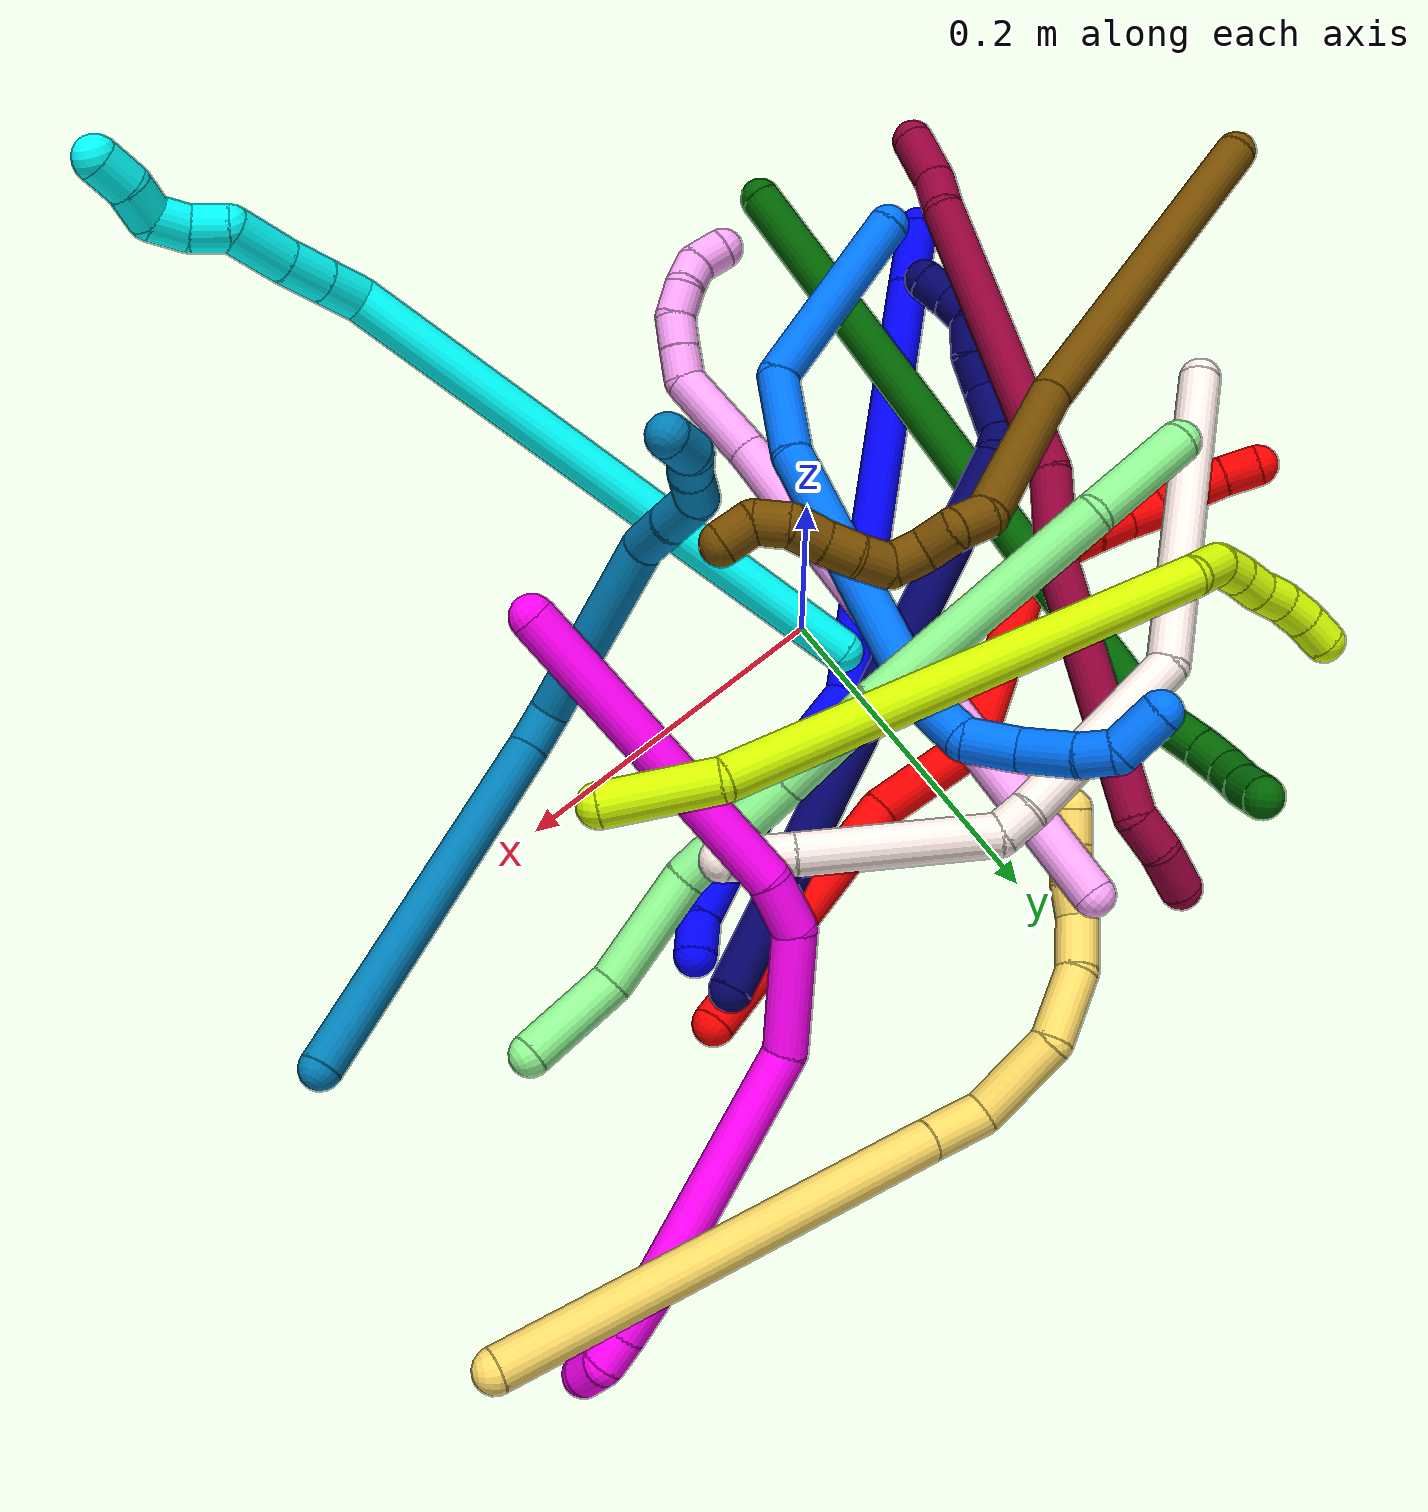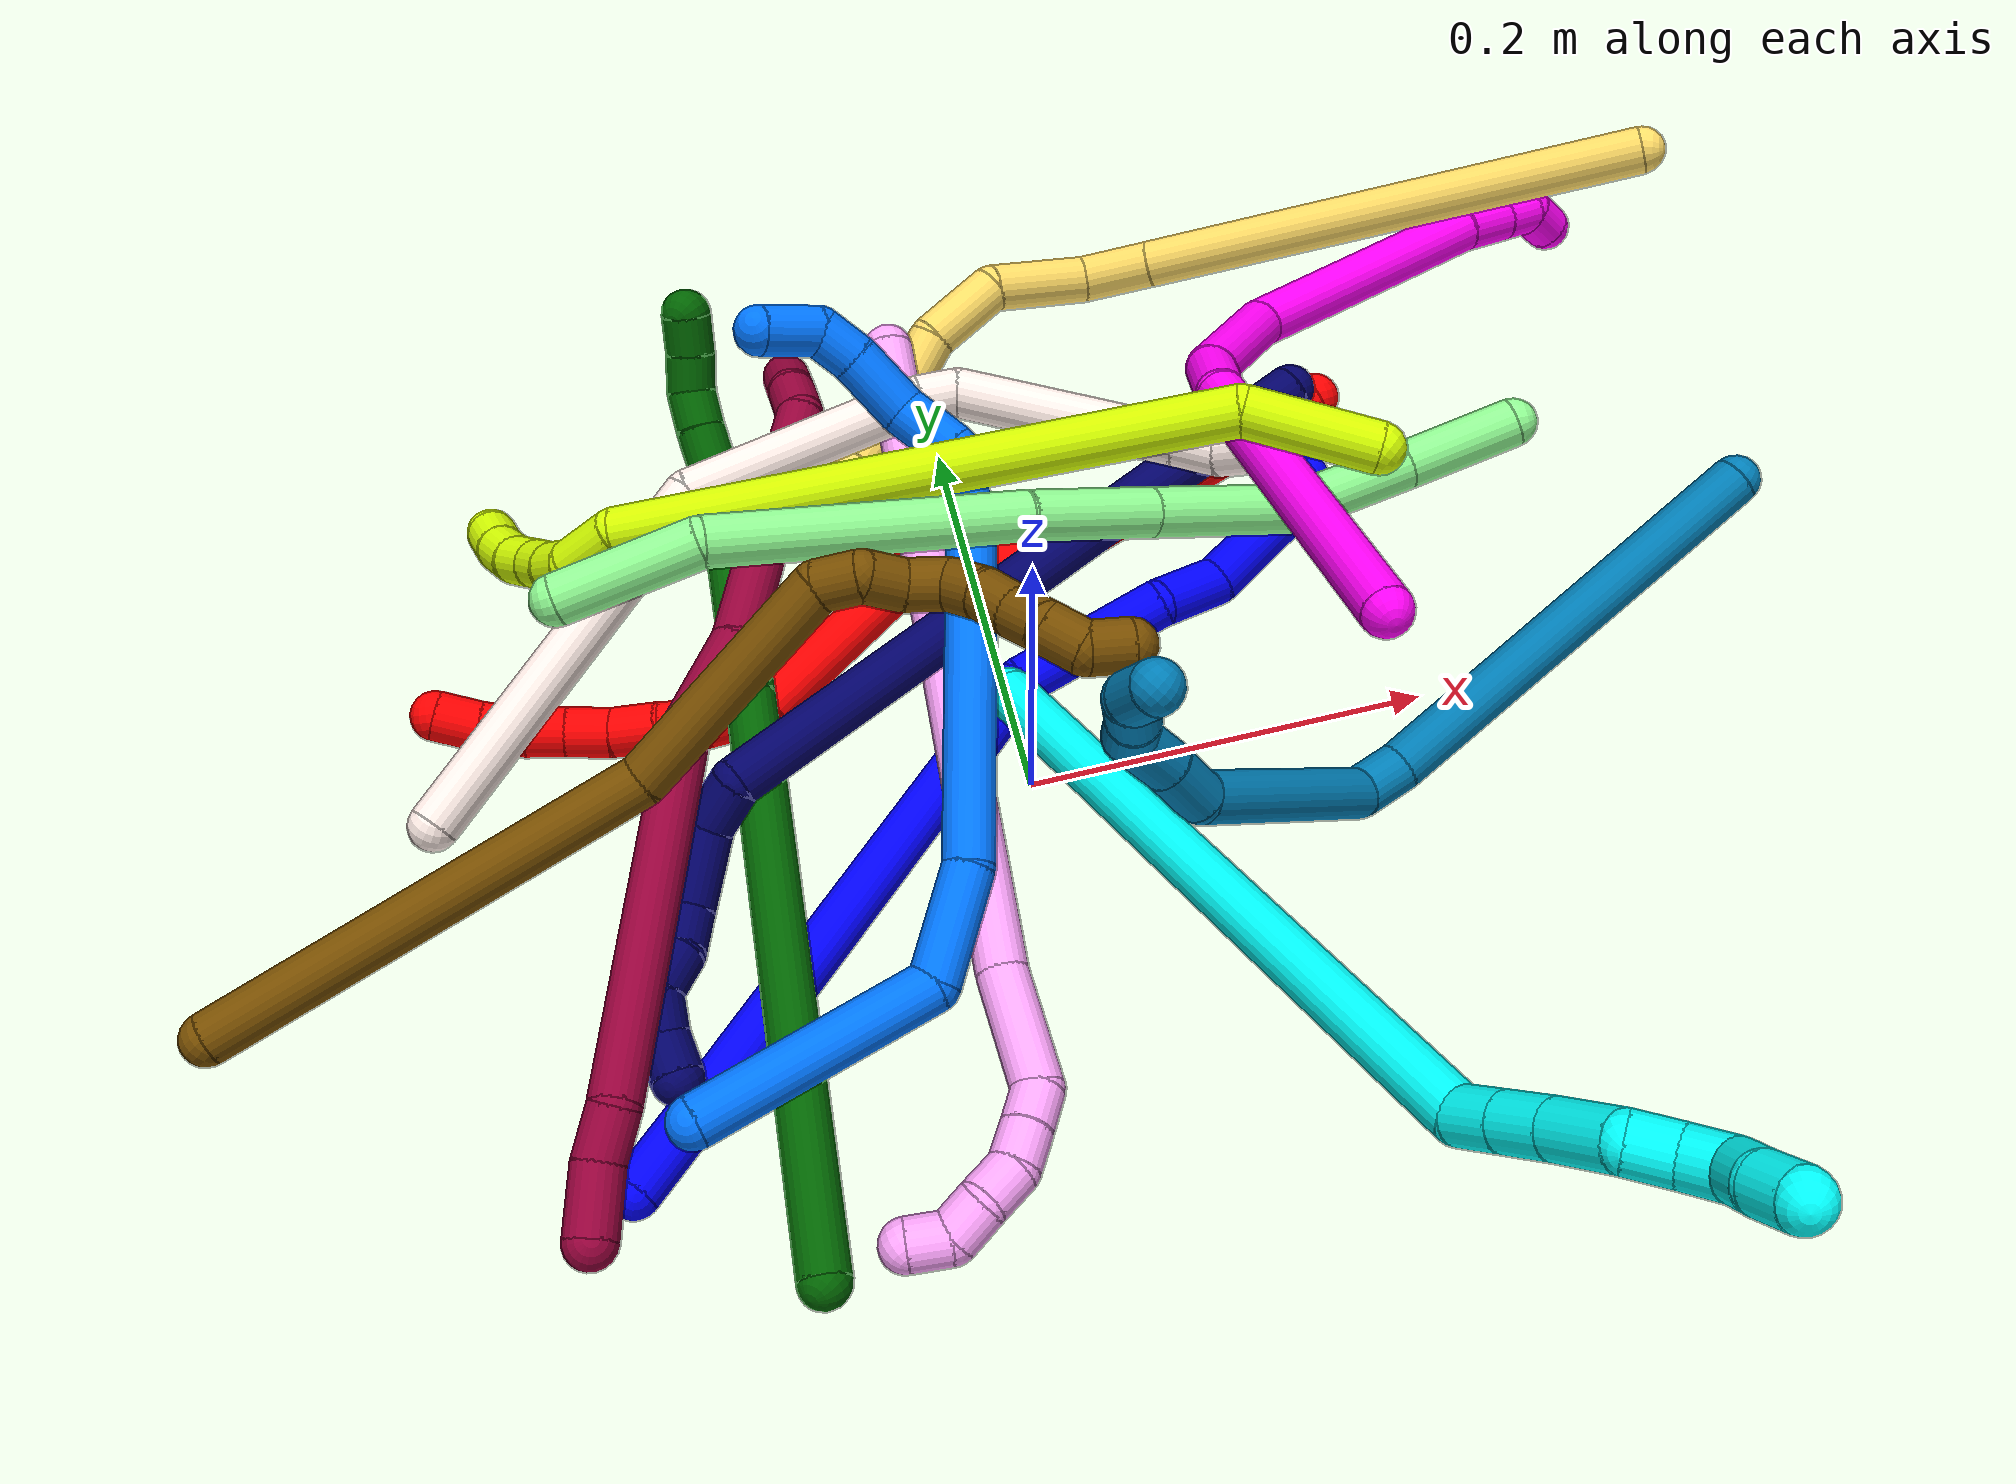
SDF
<sdf version="1.7">
 <world name="default">
  <plugin name="TubeGeneratorPlugin" filename="libtube_generator_plugin.so"/>
  <model name="photoneo_s_sensor">
   <static>1</static>
   <pose>0 0 2 1.57079 1.57079 3.14159</pose>
   <link name="link">
    <inertial><mass>0.1</mass></inertial>
    <sensor name="sensor" type="depth">
     <update_rate>30</update_rate>
     <camera>
      <horizontal_fov>1.22</horizontal_fov>
      <image><width>1920</width><height>1200</height><format>B8G8R8</format></image>
      <clip><near>0.1</near><far>4</far></clip>
      <depth_camera><output>points</output></depth_camera>
     </camera>
     <plugin name="camera_plugin" filename="libgazebo_ros_depth_camera.so">
      <baseline>0.2</baseline>
      <alwaysOn>1</alwaysOn>
      <updateRate>0.0</updateRate>
      <cameraName>camera_ir</cameraName>
      <imageTopicName>/camera/color/image_raw</imageTopicName>
      <cameraInfoTopicName>/camera/color/camera_info</cameraInfoTopicName>
      <depthImageTopicName>/camera/depth/image_raw</depthImageTopicName>
      <depthImageCameraInfoTopicName>/camera/depth/camera_info</depthImageCameraInfoTopicName>
      <pointCloudTopicName>/camera/depth/points</pointCloudTopicName>
      <frameName>fr_optical</frameName>
      <pointCloudCutoff>0.1</pointCloudCutoff>
      <pointCloudCutoffMax>2.0</pointCloudCutoffMax>
      <distortionK1>0</distortionK1>
      <distortionK2>0</distortionK2>
      <distortionK3>0</distortionK3>
      <distortionT1>0</distortionT1>
      <distortionT2>0</distortionT2>
      <CxPrime>0</CxPrime>
      <Cx>0</Cx>
      <Cy>0</Cy>
      <focalLength>0</focalLength>
      <hackBaseline>0</hackBaseline>
     </plugin>
    </sensor>
   </link>
  </model>
  <gravity>0 0 -9.8</gravity>
  <magnetic_field>6e-06 2.3e-05 -4.2e-05</magnetic_field>
  <atmosphere type="adiabatic"/>
  <physics name="default_physics" default="0" type="ode">
   <max_step_size>0.003</max_step_size>
   <real_time_factor>1</real_time_factor>
   <real_time_update_rate>1000</real_time_update_rate>
   <max_contacts>10000</max_contacts>
   <ode>
    <solver>
     <type>quick</type>
     <iters>100</iters>
     <sor>1.3</sor>
     <use_dynamic_moi_rescaling>0</use_dynamic_moi_rescaling>
    </solver>
    <constraints>
     <contact_max_correcting_vel>0</contact_max_correcting_vel>
     <contact_surface_layer>0.001</contact_surface_layer>
     <cfm>0</cfm>
     <erp>0.2</erp>
    </constraints>
   </ode>
  </physics>
  <scene><ambient>0.4 0.4 0.4 1</ambient><background>0.7 0.7 0.7 1</background><shadows>0</shadows></scene>
  <audio><device>default</device></audio>
  <spherical_coordinates>
   <surface_model>EARTH_WGS84</surface_model>
   <latitude_deg>0</latitude_deg>
   <longitude_deg>0</longitude_deg>
   <elevation>0</elevation>
   <heading_deg>0</heading_deg>
  </spherical_coordinates>
  <model name="bin">
   <static>1</static>
   <link name="bottom">
    <collision name="collision-bottom">
     <pose>0 0 -0.01 0 -0 0</pose>
     <geometry><box><size>0.8 0.6 0.02</size></box></geometry>
     <surface>
      <friction><ode><mu>100</mu><mu2>100</mu2></ode></friction>
      <contact><collide_bitmask>65535</collide_bitmask></contact>
     </surface>
    </collision>
   </link>
   <link name="west_wall">
    <collision name="collision-west_wall">
     <pose>-0.41 0 0.1 0 -0 0</pose>
     <geometry><box><size>0.02 0.6 0.2</size></box></geometry>
     <surface>
      <friction><ode><mu>100</mu><mu2>100</mu2></ode></friction>
      <contact><collide_bitmask>65535</collide_bitmask></contact>
     </surface>
    </collision>
   </link>
   <link name="east_wall">
    <collision name="collision-east_wall">
     <pose>0.41 0 0.1 0 -0 0</pose>
     <geometry><box><size>0.02 0.6 0.2</size></box></geometry>
     <surface>
      <friction><ode><mu>100</mu><mu2>100</mu2></ode></friction>
      <contact><collide_bitmask>65535</collide_bitmask></contact>
     </surface>
    </collision>
   </link>
   <link name="south_wall">
    <collision name="collision-south_wall">
     <pose>0 -0.31 0.1 0 -0 0</pose>
     <geometry><box><size>0.8 0.02 0.2</size></box></geometry>
     <surface>
      <friction><ode><mu>100</mu><mu2>100</mu2></ode></friction>
      <contact><collide_bitmask>65535</collide_bitmask></contact>
     </surface>
    </collision>
   </link>
   <link name="north_wall">
    <collision name="collision-north_wall">
     <pose>0 0.31 0.1 0 -0 0</pose>
     <geometry><box><size>0.8 0.02 0.2</size></box></geometry>
     <surface>
      <friction><ode><mu>100</mu><mu2>100</mu2></ode></friction>
      <contact><collide_bitmask>65535</collide_bitmask></contact>
     </surface>
    </collision>
   </link>
  </model>
  <model name="1">
   <static>0</static>
   <link name="1">
    <collision name="collision-cylinder-e_1_1_4">
     <pose>0.015883 0.01337 -0.003954 -1.85834 0.850367 -1.08979</pose>
     <geometry><cylinder><radius>0.0125</radius><length>0.04227</length></cylinder></geometry>
     <surface>
      <friction><ode><mu>1.16</mu><mu2>1.16</mu2><slip1>0</slip1><slip2>0</slip2></ode></friction>
      <contact><ode><kp>1e+06</kp><kd>1</kd><max_vel>0</max_vel><min_depth>0.001</min_depth></ode></contact>
     </surface>
    </collision>
    <visual name="visual-cylinder-e_1_1_4">
     <pose>0.015883 0.01337 -0.003954 -1.85834 0.850367 -1.08979</pose>
     <geometry><cylinder><radius>0.0125</radius><length>0.04227</length></cylinder></geometry>
     <material><ambient>0 0 1 1</ambient></material>
    </visual>
    <collision name="collision-cylinder-e_2_4_5">
     <pose>0.131391 0.112843 -0.034038 -1.86543 0.836222 -1.07959</pose>
     <geometry><cylinder><radius>0.0125</radius><length>0.268488</length></cylinder></geometry>
     <surface>
      <friction><ode><mu>1.16</mu><mu2>1.16</mu2><slip1>0</slip1><slip2>0</slip2></ode></friction>
      <contact><ode><kp>1e+06</kp><kd>1</kd><max_vel>0</max_vel><min_depth>0.001</min_depth></ode></contact>
     </surface>
    </collision>
    <visual name="visual-cylinder-e_2_4_5">
     <pose>0.131391 0.112843 -0.034038 -1.86543 0.836222 -1.07959</pose>
     <geometry><cylinder><radius>0.0125</radius><length>0.268488</length></cylinder></geometry>
     <material><ambient>0 0 1 1</ambient></material>
    </visual>
    <collision name="collision-cylinder-e_3_5_6">
     <pose>0.268556 0.211494 -0.055186 -1.19291 1.22556 -0.890714</pose>
     <geometry><cylinder><radius>0.0125</radius><length>0.079787</length></cylinder></geometry>
     <surface>
      <friction><ode><mu>1.16</mu><mu2>1.16</mu2><slip1>0</slip1><slip2>0</slip2></ode></friction>
      <contact><ode><kp>1e+06</kp><kd>1</kd><max_vel>0</max_vel><min_depth>0.001</min_depth></ode></contact>
     </surface>
    </collision>
    <visual name="visual-cylinder-e_3_5_6">
     <pose>0.268556 0.211494 -0.055186 -1.19291 1.22556 -0.890714</pose>
     <geometry><cylinder><radius>0.0125</radius><length>0.079787</length></cylinder></geometry>
     <material><ambient>0 0 1 1</ambient></material>
    </visual>
    <collision name="collision-cylinder-e_4_6_7">
     <pose>0.323774 0.227932 -0.055913 -2.54351 1.19831 -2.2935</pose>
     <geometry><cylinder><radius>0.0125</radius><length>0.03796</length></cylinder></geometry>
     <surface>
      <friction><ode><mu>1.16</mu><mu2>1.16</mu2><slip1>0</slip1><slip2>0</slip2></ode></friction>
      <contact><ode><kp>1e+06</kp><kd>1</kd><max_vel>0</max_vel><min_depth>0.001</min_depth></ode></contact>
     </surface>
    </collision>
    <visual name="visual-cylinder-e_4_6_7">
     <pose>0.323774 0.227932 -0.055913 -2.54351 1.19831 -2.2935</pose>
     <geometry><cylinder><radius>0.0125</radius><length>0.03796</length></cylinder></geometry>
     <material><ambient>0 0 1 1</ambient></material>
    </visual>
    <collision name="collision-cylinder-e_5_7_8">
     <pose>0.361275 0.24506 -0.056779 -1.22013 0.952658 -0.692277</pose>
     <geometry><cylinder><radius>0.0125</radius><length>0.048649</length></cylinder></geometry>
     <surface>
      <friction><ode><mu>1.16</mu><mu2>1.16</mu2><slip1>0</slip1><slip2>0</slip2></ode></friction>
      <contact><ode><kp>1e+06</kp><kd>1</kd><max_vel>0</max_vel><min_depth>0.001</min_depth></ode></contact>
     </surface>
    </collision>
    <visual name="visual-cylinder-e_5_7_8">
     <pose>0.361275 0.24506 -0.056779 -1.22013 0.952658 -0.692277</pose>
     <geometry><cylinder><radius>0.0125</radius><length>0.048649</length></cylinder></geometry>
     <material><ambient>0 0 1 1</ambient></material>
    </visual>
    <collision name="collision-cylinder-e_6_8_2">
     <pose>0.388425 0.267062 -0.051821 -1.55765 0.696239 -0.687853</pose>
     <geometry><cylinder><radius>0.0125</radius><length>0.022846</length></cylinder></geometry>
     <surface>
      <friction><ode><mu>1.16</mu><mu2>1.16</mu2><slip1>0</slip1><slip2>0</slip2></ode></friction>
      <contact><ode><kp>1e+06</kp><kd>1</kd><max_vel>0</max_vel><min_depth>0.001</min_depth></ode></contact>
     </surface>
    </collision>
    <visual name="visual-cylinder-e_6_8_2">
     <pose>0.388425 0.267062 -0.051821 -1.55765 0.696239 -0.687853</pose>
     <geometry><cylinder><radius>0.0125</radius><length>0.022846</length></cylinder></geometry>
     <material><ambient>0 0 1 1</ambient></material>
    </visual>
    <collision name="collision-sphere-2">
     <pose>0.395751 0.275826 -0.051706 0 -0 0</pose>
     <geometry><sphere><radius>0.0125</radius></sphere></geometry>
     <surface>
      <friction><ode><mu>1.16</mu><mu2>1.16</mu2><slip1>0</slip1><slip2>0</slip2></ode></friction>
      <contact><ode><kp>1e+06</kp><kd>1</kd><max_vel>0</max_vel><min_depth>0.001</min_depth></ode></contact>
     </surface>
    </collision>
    <visual name="visual-sphere-2">
     <pose>0.395751 0.275826 -0.051706 0 -0 0</pose>
     <geometry><sphere><radius>0.0125</radius></sphere></geometry>
     <material><ambient>0 0 1 1</ambient></material>
    </visual>
    <collision name="collision-sphere-4">
     <pose>0.031767 0.026741 -0.007908 0 -0 0</pose>
     <geometry><sphere><radius>0.0125</radius></sphere></geometry>
     <surface>
      <friction><ode><mu>1.16</mu><mu2>1.16</mu2><slip1>0</slip1><slip2>0</slip2></ode></friction>
      <contact><ode><kp>1e+06</kp><kd>1</kd><max_vel>0</max_vel><min_depth>0.001</min_depth></ode></contact>
     </surface>
    </collision>
    <visual name="visual-sphere-4">
     <pose>0.031767 0.026741 -0.007908 0 -0 0</pose>
     <geometry><sphere><radius>0.0125</radius></sphere></geometry>
     <material><ambient>0 0 1 1</ambient></material>
    </visual>
    <collision name="collision-sphere-1">
     <geometry><sphere><radius>0.0125</radius></sphere></geometry>
     <surface>
      <friction><ode><mu>1.16</mu><mu2>1.16</mu2><slip1>0</slip1><slip2>0</slip2></ode></friction>
      <contact><ode><kp>1e+06</kp><kd>1</kd><max_vel>0</max_vel><min_depth>0.001</min_depth></ode></contact>
     </surface>
    </collision>
    <visual name="visual-sphere-1">
     <geometry><sphere><radius>0.0125</radius></sphere></geometry>
     <material><ambient>0 0 1 1</ambient></material>
    </visual>
    <collision name="collision-sphere-8">
     <pose>0.381099 0.258298 -0.051936 0 -0 0</pose>
     <geometry><sphere><radius>0.0125</radius></sphere></geometry>
     <surface>
      <friction><ode><mu>1.16</mu><mu2>1.16</mu2><slip1>0</slip1><slip2>0</slip2></ode></friction>
      <contact><ode><kp>1e+06</kp><kd>1</kd><max_vel>0</max_vel><min_depth>0.001</min_depth></ode></contact>
     </surface>
    </collision>
    <visual name="visual-sphere-8">
     <pose>0.381099 0.258298 -0.051936 0 -0 0</pose>
     <geometry><sphere><radius>0.0125</radius></sphere></geometry>
     <material><ambient>0 0 1 1</ambient></material>
    </visual>
    <collision name="collision-sphere-5">
     <pose>0.231016 0.198946 -0.060167 0 -0 0</pose>
     <geometry><sphere><radius>0.0125</radius></sphere></geometry>
     <surface>
      <friction><ode><mu>1.16</mu><mu2>1.16</mu2><slip1>0</slip1><slip2>0</slip2></ode></friction>
      <contact><ode><kp>1e+06</kp><kd>1</kd><max_vel>0</max_vel><min_depth>0.001</min_depth></ode></contact>
     </surface>
    </collision>
    <visual name="visual-sphere-5">
     <pose>0.231016 0.198946 -0.060167 0 -0 0</pose>
     <geometry><sphere><radius>0.0125</radius></sphere></geometry>
     <material><ambient>0 0 1 1</ambient></material>
    </visual>
    <collision name="collision-sphere-6">
     <pose>0.306095 0.224043 -0.050204 0 -0 0</pose>
     <geometry><sphere><radius>0.0125</radius></sphere></geometry>
     <surface>
      <friction><ode><mu>1.16</mu><mu2>1.16</mu2><slip1>0</slip1><slip2>0</slip2></ode></friction>
      <contact><ode><kp>1e+06</kp><kd>1</kd><max_vel>0</max_vel><min_depth>0.001</min_depth></ode></contact>
     </surface>
    </collision>
    <visual name="visual-sphere-6">
     <pose>0.306095 0.224043 -0.050204 0 -0 0</pose>
     <geometry><sphere><radius>0.0125</radius></sphere></geometry>
     <material><ambient>0 0 1 1</ambient></material>
    </visual>
    <collision name="collision-sphere-7">
     <pose>0.341452 0.231821 -0.061621 0 -0 0</pose>
     <geometry><sphere><radius>0.0125</radius></sphere></geometry>
     <surface>
      <friction><ode><mu>1.16</mu><mu2>1.16</mu2><slip1>0</slip1><slip2>0</slip2></ode></friction>
      <contact><ode><kp>1e+06</kp><kd>1</kd><max_vel>0</max_vel><min_depth>0.001</min_depth></ode></contact>
     </surface>
    </collision>
    <visual name="visual-sphere-7">
     <pose>0.341452 0.231821 -0.061621 0 -0 0</pose>
     <geometry><sphere><radius>0.0125</radius></sphere></geometry>
     <material><ambient>0 0 1 1</ambient></material>
    </visual>
    <inertial>
     <pose>0.192232 0.148825 -0.039555 0 -0 0</pose>
     <mass>0.5</mass>
     <inertia>
      <ixx>-0.000422</ixx>
      <ixy>0</ixy>
      <ixz>0</ixz>
      <iyy>-0.000107</iyy>
      <iyz>0</iyz>
      <izz>-0.002343</izz>
     </inertia>
    </inertial>
   </link>
   <pose>-0.221634 -0.158278 0.011496 0.406388 0.100876 0.013294</pose>
  </model>
  <model name="2">
   <static>0</static>
   <link name="2">
    <collision name="collision-cylinder-e_1_1_4">
     <pose>-0.077454 0.000726 -0.027057 -3.11475 -1.23461 3.10378</pose>
     <geometry><cylinder><radius>0.0125</radius><length>0.164095</length></cylinder></geometry>
     <surface>
      <friction><ode><mu>1.16</mu><mu2>1.16</mu2><slip1>0</slip1><slip2>0</slip2></ode></friction>
      <contact><ode><kp>1e+06</kp><kd>1</kd><max_vel>0</max_vel><min_depth>0.001</min_depth></ode></contact>
     </surface>
    </collision>
    <visual name="visual-cylinder-e_1_1_4">
     <pose>-0.077454 0.000726 -0.027057 -3.11475 -1.23461 3.10378</pose>
     <geometry><cylinder><radius>0.0125</radius><length>0.164095</length></cylinder></geometry>
     <material><ambient>1 0 0 1</ambient></material>
    </visual>
    <collision name="collision-cylinder-e_2_4_5">
     <pose>-0.187193 0.000964 -0.048769 0.091274 -1.40607 -0.077369</pose>
     <geometry><cylinder><radius>0.0125</radius><length>0.065454</length></cylinder></geometry>
     <surface>
      <friction><ode><mu>1.16</mu><mu2>1.16</mu2><slip1>0</slip1><slip2>0</slip2></ode></friction>
      <contact><ode><kp>1e+06</kp><kd>1</kd><max_vel>0</max_vel><min_depth>0.001</min_depth></ode></contact>
     </surface>
    </collision>
    <visual name="visual-cylinder-e_2_4_5">
     <pose>-0.187193 0.000964 -0.048769 0.091274 -1.40607 -0.077369</pose>
     <geometry><cylinder><radius>0.0125</radius><length>0.065454</length></cylinder></geometry>
     <material><ambient>1 0 0 1</ambient></material>
    </visual>
    <collision name="collision-cylinder-e_3_5_6">
     <pose>-0.263766 -0.013263 -0.067179 2.61727 -1.01611 -2.24344</pose>
     <geometry><cylinder><radius>0.0125</radius><length>0.104203</length></cylinder></geometry>
     <surface>
      <friction><ode><mu>1.16</mu><mu2>1.16</mu2><slip1>0</slip1><slip2>0</slip2></ode></friction>
      <contact><ode><kp>1e+06</kp><kd>1</kd><max_vel>0</max_vel><min_depth>0.001</min_depth></ode></contact>
     </surface>
    </collision>
    <visual name="visual-cylinder-e_3_5_6">
     <pose>-0.263766 -0.013263 -0.067179 2.61727 -1.01611 -2.24344</pose>
     <geometry><cylinder><radius>0.0125</radius><length>0.104203</length></cylinder></geometry>
     <material><ambient>1 0 0 1</ambient></material>
    </visual>
    <collision name="collision-cylinder-e_4_6_7">
     <pose>-0.325127 -0.030634 -0.090891 1.55902 -1.36102 -1.34951</pose>
     <geometry><cylinder><radius>0.0125</radius><length>0.034907</length></cylinder></geometry>
     <surface>
      <friction><ode><mu>1.16</mu><mu2>1.16</mu2><slip1>0</slip1><slip2>0</slip2></ode></friction>
      <contact><ode><kp>1e+06</kp><kd>1</kd><max_vel>0</max_vel><min_depth>0.001</min_depth></ode></contact>
     </surface>
    </collision>
    <visual name="visual-cylinder-e_4_6_7">
     <pose>-0.325127 -0.030634 -0.090891 1.55902 -1.36102 -1.34951</pose>
     <geometry><cylinder><radius>0.0125</radius><length>0.034907</length></cylinder></geometry>
     <material><ambient>1 0 0 1</ambient></material>
    </visual>
    <collision name="collision-cylinder-e_5_7_8">
     <pose>-0.352411 -0.032091 -0.089518 -1.02262 -1.32596 0.825903</pose>
     <geometry><cylinder><radius>0.0125</radius><length>0.021054</length></cylinder></geometry>
     <surface>
      <friction><ode><mu>1.16</mu><mu2>1.16</mu2><slip1>0</slip1><slip2>0</slip2></ode></friction>
      <contact><ode><kp>1e+06</kp><kd>1</kd><max_vel>0</max_vel><min_depth>0.001</min_depth></ode></contact>
     </surface>
    </collision>
    <visual name="visual-cylinder-e_5_7_8">
     <pose>-0.352411 -0.032091 -0.089518 -1.02262 -1.32596 0.825903</pose>
     <geometry><cylinder><radius>0.0125</radius><length>0.021054</length></cylinder></geometry>
     <material><ambient>1 0 0 1</ambient></material>
    </visual>
    <collision name="collision-cylinder-e_6_8_9">
     <pose>-0.373691 -0.026517 -0.087951 -1.50094 -1.27236 1.20627</pose>
     <geometry><cylinder><radius>0.0125</radius><length>0.023157</length></cylinder></geometry>
     <surface>
      <friction><ode><mu>1.16</mu><mu2>1.16</mu2><slip1>0</slip1><slip2>0</slip2></ode></friction>
      <contact><ode><kp>1e+06</kp><kd>1</kd><max_vel>0</max_vel><min_depth>0.001</min_depth></ode></contact>
     </surface>
    </collision>
    <visual name="visual-cylinder-e_6_8_9">
     <pose>-0.373691 -0.026517 -0.087951 -1.50094 -1.27236 1.20627</pose>
     <geometry><cylinder><radius>0.0125</radius><length>0.023157</length></cylinder></geometry>
     <material><ambient>1 0 0 1</ambient></material>
    </visual>
    <collision name="collision-cylinder-e_7_9_10">
     <pose>-0.395738 -0.019817 -0.085875 -1.06325 -1.23919 0.794391</pose>
     <geometry><cylinder><radius>0.0125</radius><length>0.023226</length></cylinder></geometry>
     <surface>
      <friction><ode><mu>1.16</mu><mu2>1.16</mu2><slip1>0</slip1><slip2>0</slip2></ode></friction>
      <contact><ode><kp>1e+06</kp><kd>1</kd><max_vel>0</max_vel><min_depth>0.001</min_depth></ode></contact>
     </surface>
    </collision>
    <visual name="visual-cylinder-e_7_9_10">
     <pose>-0.395738 -0.019817 -0.085875 -1.06325 -1.23919 0.794391</pose>
     <geometry><cylinder><radius>0.0125</radius><length>0.023226</length></cylinder></geometry>
     <material><ambient>1 0 0 1</ambient></material>
    </visual>
    <collision name="collision-cylinder-e_8_10_11">
     <pose>-0.416488 -0.015896 -0.081989 -0.29248 -1.35519 0.235947</pose>
     <geometry><cylinder><radius>0.0125</radius><length>0.020002</length></cylinder></geometry>
     <surface>
      <friction><ode><mu>1.16</mu><mu2>1.16</mu2><slip1>0</slip1><slip2>0</slip2></ode></friction>
      <contact><ode><kp>1e+06</kp><kd>1</kd><max_vel>0</max_vel><min_depth>0.001</min_depth></ode></contact>
     </surface>
    </collision>
    <visual name="visual-cylinder-e_8_10_11">
     <pose>-0.416488 -0.015896 -0.081989 -0.29248 -1.35519 0.235947</pose>
     <geometry><cylinder><radius>0.0125</radius><length>0.020002</length></cylinder></geometry>
     <material><ambient>1 0 0 1</ambient></material>
    </visual>
    <collision name="collision-cylinder-e_9_11_12">
     <pose>-0.436622 -0.013982 -0.076333 -0.345041 -1.21654 0.2415</pose>
     <geometry><cylinder><radius>0.0125</radius><length>0.022102</length></cylinder></geometry>
     <surface>
      <friction><ode><mu>1.16</mu><mu2>1.16</mu2><slip1>0</slip1><slip2>0</slip2></ode></friction>
      <contact><ode><kp>1e+06</kp><kd>1</kd><max_vel>0</max_vel><min_depth>0.001</min_depth></ode></contact>
     </surface>
    </collision>
    <visual name="visual-cylinder-e_9_11_12">
     <pose>-0.436622 -0.013982 -0.076333 -0.345041 -1.21654 0.2415</pose>
     <geometry><cylinder><radius>0.0125</radius><length>0.022102</length></cylinder></geometry>
     <material><ambient>1 0 0 1</ambient></material>
    </visual>
    <collision name="collision-cylinder-e_10_12_2">
     <pose>-0.456748 -0.011006 -0.068175 -0.353625 -1.10963 0.220572</pose>
     <geometry><cylinder><radius>0.0125</radius><length>0.0218</length></cylinder></geometry>
     <surface>
      <friction><ode><mu>1.16</mu><mu2>1.16</mu2><slip1>0</slip1><slip2>0</slip2></ode></friction>
      <contact><ode><kp>1e+06</kp><kd>1</kd><max_vel>0</max_vel><min_depth>0.001</min_depth></ode></contact>
     </surface>
    </collision>
    <visual name="visual-cylinder-e_10_12_2">
     <pose>-0.456748 -0.011006 -0.068175 -0.353625 -1.10963 0.220572</pose>
     <geometry><cylinder><radius>0.0125</radius><length>0.0218</length></cylinder></geometry>
     <material><ambient>1 0 0 1</ambient></material>
    </visual>
    <collision name="collision-sphere-2">
     <pose>-0.46651 -0.009326 -0.063625 0 -0 0</pose>
     <geometry><sphere><radius>0.0125</radius></sphere></geometry>
     <surface>
      <friction><ode><mu>1.16</mu><mu2>1.16</mu2><slip1>0</slip1><slip2>0</slip2></ode></friction>
      <contact><ode><kp>1e+06</kp><kd>1</kd><max_vel>0</max_vel><min_depth>0.001</min_depth></ode></contact>
     </surface>
    </collision>
    <visual name="visual-sphere-2">
     <pose>-0.46651 -0.009326 -0.063625 0 -0 0</pose>
     <geometry><sphere><radius>0.0125</radius></sphere></geometry>
     <material><ambient>1 0 0 1</ambient></material>
    </visual>
    <collision name="collision-sphere-12">
     <pose>-0.446987 -0.012686 -0.072725 0 -0 0</pose>
     <geometry><sphere><radius>0.0125</radius></sphere></geometry>
     <surface>
      <friction><ode><mu>1.16</mu><mu2>1.16</mu2><slip1>0</slip1><slip2>0</slip2></ode></friction>
      <contact><ode><kp>1e+06</kp><kd>1</kd><max_vel>0</max_vel><min_depth>0.001</min_depth></ode></contact>
     </surface>
    </collision>
    <visual name="visual-sphere-12">
     <pose>-0.446987 -0.012686 -0.072725 0 -0 0</pose>
     <geometry><sphere><radius>0.0125</radius></sphere></geometry>
     <material><ambient>1 0 0 1</ambient></material>
    </visual>
    <collision name="collision-sphere-11">
     <pose>-0.426257 -0.015279 -0.07994 0 -0 0</pose>
     <geometry><sphere><radius>0.0125</radius></sphere></geometry>
     <surface>
      <friction><ode><mu>1.16</mu><mu2>1.16</mu2><slip1>0</slip1><slip2>0</slip2></ode></friction>
      <contact><ode><kp>1e+06</kp><kd>1</kd><max_vel>0</max_vel><min_depth>0.001</min_depth></ode></contact>
     </surface>
    </collision>
    <visual name="visual-sphere-11">
     <pose>-0.426257 -0.015279 -0.07994 0 -0 0</pose>
     <geometry><sphere><radius>0.0125</radius></sphere></geometry>
     <material><ambient>1 0 0 1</ambient></material>
    </visual>
    <collision name="collision-sphere-10">
     <pose>-0.406719 -0.016513 -0.084038 0 -0 0</pose>
     <geometry><sphere><radius>0.0125</radius></sphere></geometry>
     <surface>
      <friction><ode><mu>1.16</mu><mu2>1.16</mu2><slip1>0</slip1><slip2>0</slip2></ode></friction>
      <contact><ode><kp>1e+06</kp><kd>1</kd><max_vel>0</max_vel><min_depth>0.001</min_depth></ode></contact>
     </surface>
    </collision>
    <visual name="visual-sphere-10">
     <pose>-0.406719 -0.016513 -0.084038 0 -0 0</pose>
     <geometry><sphere><radius>0.0125</radius></sphere></geometry>
     <material><ambient>1 0 0 1</ambient></material>
    </visual>
    <collision name="collision-sphere-9">
     <pose>-0.384758 -0.023121 -0.087713 0 -0 0</pose>
     <geometry><sphere><radius>0.0125</radius></sphere></geometry>
     <surface>
      <friction><ode><mu>1.16</mu><mu2>1.16</mu2><slip1>0</slip1><slip2>0</slip2></ode></friction>
      <contact><ode><kp>1e+06</kp><kd>1</kd><max_vel>0</max_vel><min_depth>0.001</min_depth></ode></contact>
     </surface>
    </collision>
    <visual name="visual-sphere-9">
     <pose>-0.384758 -0.023121 -0.087713 0 -0 0</pose>
     <geometry><sphere><radius>0.0125</radius></sphere></geometry>
     <material><ambient>1 0 0 1</ambient></material>
    </visual>
    <collision name="collision-sphere-4">
     <pose>-0.154909 0.001453 -0.054114 0 -0 0</pose>
     <geometry><sphere><radius>0.0125</radius></sphere></geometry>
     <surface>
      <friction><ode><mu>1.16</mu><mu2>1.16</mu2><slip1>0</slip1><slip2>0</slip2></ode></friction>
      <contact><ode><kp>1e+06</kp><kd>1</kd><max_vel>0</max_vel><min_depth>0.001</min_depth></ode></contact>
     </surface>
    </collision>
    <visual name="visual-sphere-4">
     <pose>-0.154909 0.001453 -0.054114 0 -0 0</pose>
     <geometry><sphere><radius>0.0125</radius></sphere></geometry>
     <material><ambient>1 0 0 1</ambient></material>
    </visual>
    <collision name="collision-sphere-1">
     <geometry><sphere><radius>0.0125</radius></sphere></geometry>
     <surface>
      <friction><ode><mu>1.16</mu><mu2>1.16</mu2><slip1>0</slip1><slip2>0</slip2></ode></friction>
      <contact><ode><kp>1e+06</kp><kd>1</kd><max_vel>0</max_vel><min_depth>0.001</min_depth></ode></contact>
     </surface>
    </collision>
    <visual name="visual-sphere-1">
     <geometry><sphere><radius>0.0125</radius></sphere></geometry>
     <material><ambient>1 0 0 1</ambient></material>
    </visual>
    <collision name="collision-sphere-8">
     <pose>-0.362624 -0.029913 -0.088188 0 -0 0</pose>
     <geometry><sphere><radius>0.0125</radius></sphere></geometry>
     <surface>
      <friction><ode><mu>1.16</mu><mu2>1.16</mu2><slip1>0</slip1><slip2>0</slip2></ode></friction>
      <contact><ode><kp>1e+06</kp><kd>1</kd><max_vel>0</max_vel><min_depth>0.001</min_depth></ode></contact>
     </surface>
    </collision>
    <visual name="visual-sphere-8">
     <pose>-0.362624 -0.029913 -0.088188 0 -0 0</pose>
     <geometry><sphere><radius>0.0125</radius></sphere></geometry>
     <material><ambient>1 0 0 1</ambient></material>
    </visual>
    <collision name="collision-sphere-5">
     <pose>-0.219477 0.000475 -0.043425 0 -0 0</pose>
     <geometry><sphere><radius>0.0125</radius></sphere></geometry>
     <surface>
      <friction><ode><mu>1.16</mu><mu2>1.16</mu2><slip1>0</slip1><slip2>0</slip2></ode></friction>
      <contact><ode><kp>1e+06</kp><kd>1</kd><max_vel>0</max_vel><min_depth>0.001</min_depth></ode></contact>
     </surface>
    </collision>
    <visual name="visual-sphere-5">
     <pose>-0.219477 0.000475 -0.043425 0 -0 0</pose>
     <geometry><sphere><radius>0.0125</radius></sphere></geometry>
     <material><ambient>1 0 0 1</ambient></material>
    </visual>
    <collision name="collision-sphere-6">
     <pose>-0.308056 -0.027 -0.090933 0 -0 0</pose>
     <geometry><sphere><radius>0.0125</radius></sphere></geometry>
     <surface>
      <friction><ode><mu>1.16</mu><mu2>1.16</mu2><slip1>0</slip1><slip2>0</slip2></ode></friction>
      <contact><ode><kp>1e+06</kp><kd>1</kd><max_vel>0</max_vel><min_depth>0.001</min_depth></ode></contact>
     </surface>
    </collision>
    <visual name="visual-sphere-6">
     <pose>-0.308056 -0.027 -0.090933 0 -0 0</pose>
     <geometry><sphere><radius>0.0125</radius></sphere></geometry>
     <material><ambient>1 0 0 1</ambient></material>
    </visual>
    <collision name="collision-sphere-7">
     <pose>-0.342198 -0.034269 -0.090848 0 -0 0</pose>
     <geometry><sphere><radius>0.0125</radius></sphere></geometry>
     <surface>
      <friction><ode><mu>1.16</mu><mu2>1.16</mu2><slip1>0</slip1><slip2>0</slip2></ode></friction>
      <contact><ode><kp>1e+06</kp><kd>1</kd><max_vel>0</max_vel><min_depth>0.001</min_depth></ode></contact>
     </surface>
    </collision>
    <visual name="visual-sphere-7">
     <pose>-0.342198 -0.034269 -0.090848 0 -0 0</pose>
     <geometry><sphere><radius>0.0125</radius></sphere></geometry>
     <material><ambient>1 0 0 1</ambient></material>
    </visual>
    <inertial>
     <pose>-0.233999 -0.009772 -0.057068 0 -0 0</pose>
     <mass>0.5</mass>
     <inertia>
      <ixx>-0.000221</ixx>
      <ixy>0</ixy>
      <ixz>0</ixz>
      <iyy>0.000465</iyy>
      <iyz>0</iyz>
      <izz>0.000495</izz>
     </inertia>
    </inertial>
   </link>
   <pose>0.190971 0.15885 0.045027 -0.809656 0.031139 0.020762</pose>
  </model>
  <model name="3">
   <static>0</static>
   <link name="3">
    <collision name="collision-cylinder-e_1_1_4">
     <pose>0.025143 -0.110605 0.123597 0.729982 0.150443 0.057579</pose>
     <geometry><cylinder><radius>0.0125</radius><length>0.335511</length></cylinder></geometry>
     <surface>
      <friction><ode><mu>1.16</mu><mu2>1.16</mu2><slip1>0</slip1><slip2>0</slip2></ode></friction>
      <contact><ode><kp>1e+06</kp><kd>1</kd><max_vel>0</max_vel><min_depth>0.001</min_depth></ode></contact>
     </surface>
    </collision>
    <visual name="visual-cylinder-e_1_1_4">
     <pose>0.025143 -0.110605 0.123597 0.729982 0.150443 0.057579</pose>
     <geometry><cylinder><radius>0.0125</radius><length>0.335511</length></cylinder></geometry>
     <material><ambient>0.003922 1 0.996078 1</ambient></material>
    </visual>
    <collision name="collision-cylinder-e_2_4_5">
     <pose>0.057406 -0.225485 0.255944 0.45443 0.63135 0.150737</pose>
     <geometry><cylinder><radius>0.0125</radius><length>0.024128</length></cylinder></geometry>
     <surface>
      <friction><ode><mu>1.16</mu><mu2>1.16</mu2><slip1>0</slip1><slip2>0</slip2></ode></friction>
      <contact><ode><kp>1e+06</kp><kd>1</kd><max_vel>0</max_vel><min_depth>0.001</min_depth></ode></contact>
     </surface>
    </collision>
    <visual name="visual-cylinder-e_2_4_5">
     <pose>0.057406 -0.225485 0.255944 0.45443 0.63135 0.150737</pose>
     <geometry><cylinder><radius>0.0125</radius><length>0.024128</length></cylinder></geometry>
     <material><ambient>0.003922 1 0.996078 1</ambient></material>
    </visual>
    <collision name="collision-cylinder-e_3_5_6">
     <pose>0.071906 -0.23421 0.273795 0.454804 0.629581 0.150415</pose>
     <geometry><cylinder><radius>0.0125</radius><length>0.025065</length></cylinder></geometry>
     <surface>
      <friction><ode><mu>1.16</mu><mu2>1.16</mu2><slip1>0</slip1><slip2>0</slip2></ode></friction>
      <contact><ode><kp>1e+06</kp><kd>1</kd><max_vel>0</max_vel><min_depth>0.001</min_depth></ode></contact>
     </surface>
    </collision>
    <visual name="visual-cylinder-e_3_5_6">
     <pose>0.071906 -0.23421 0.273795 0.454804 0.629581 0.150415</pose>
     <geometry><cylinder><radius>0.0125</radius><length>0.025065</length></cylinder></geometry>
     <material><ambient>0.003922 1 0.996078 1</ambient></material>
    </visual>
    <collision name="collision-cylinder-e_4_6_7">
     <pose>0.088704 -0.244128 0.296032 0.394425 0.584671 0.120124</pose>
     <geometry><cylinder><radius>0.0125</radius><length>0.03413</length></cylinder></geometry>
     <surface>
      <friction><ode><mu>1.16</mu><mu2>1.16</mu2><slip1>0</slip1><slip2>0</slip2></ode></friction>
      <contact><ode><kp>1e+06</kp><kd>1</kd><max_vel>0</max_vel><min_depth>0.001</min_depth></ode></contact>
     </surface>
    </collision>
    <visual name="visual-cylinder-e_4_6_7">
     <pose>0.088704 -0.244128 0.296032 0.394425 0.584671 0.120124</pose>
     <geometry><cylinder><radius>0.0125</radius><length>0.03413</length></cylinder></geometry>
     <material><ambient>0.003922 1 0.996078 1</ambient></material>
    </visual>
    <collision name="collision-cylinder-e_5_7_8">
     <pose>0.10378 -0.257946 0.311696 1.27704 0.575356 0.432376</pose>
     <geometry><cylinder><radius>0.0125</radius><length>0.020794</length></cylinder></geometry>
     <surface>
      <friction><ode><mu>1.16</mu><mu2>1.16</mu2><slip1>0</slip1><slip2>0</slip2></ode></friction>
      <contact><ode><kp>1e+06</kp><kd>1</kd><max_vel>0</max_vel><min_depth>0.001</min_depth></ode></contact>
     </surface>
    </collision>
    <visual name="visual-cylinder-e_5_7_8">
     <pose>0.10378 -0.257946 0.311696 1.27704 0.575356 0.432376</pose>
     <geometry><cylinder><radius>0.0125</radius><length>0.020794</length></cylinder></geometry>
     <material><ambient>0.003922 1 0.996078 1</ambient></material>
    </visual>
    <collision name="collision-cylinder-e_6_8_9">
     <pose>0.11503 -0.272443 0.319876 0.827204 0.590055 0.265207</pose>
     <geometry><cylinder><radius>0.0125</radius><length>0.020106</length></cylinder></geometry>
     <surface>
      <friction><ode><mu>1.16</mu><mu2>1.16</mu2><slip1>0</slip1><slip2>0</slip2></ode></friction>
      <contact><ode><kp>1e+06</kp><kd>1</kd><max_vel>0</max_vel><min_depth>0.001</min_depth></ode></contact>
     </surface>
    </collision>
    <visual name="visual-cylinder-e_6_8_9">
     <pose>0.11503 -0.272443 0.319876 0.827204 0.590055 0.265207</pose>
     <geometry><cylinder><radius>0.0125</radius><length>0.020106</length></cylinder></geometry>
     <material><ambient>0.003922 1 0.996078 1</ambient></material>
    </visual>
    <collision name="collision-cylinder-e_7_9_10">
     <pose>0.123594 -0.279083 0.335159 0.051059 0.298909 0.00769</pose>
     <geometry><cylinder><radius>0.0125</radius><length>0.020176</length></cylinder></geometry>
     <surface>
      <friction><ode><mu>1.16</mu><mu2>1.16</mu2><slip1>0</slip1><slip2>0</slip2></ode></friction>
      <contact><ode><kp>1e+06</kp><kd>1</kd><max_vel>0</max_vel><min_depth>0.001</min_depth></ode></contact>
     </surface>
    </collision>
    <visual name="visual-cylinder-e_7_9_10">
     <pose>0.123594 -0.279083 0.335159 0.051059 0.298909 0.00769</pose>
     <geometry><cylinder><radius>0.0125</radius><length>0.020176</length></cylinder></geometry>
     <material><ambient>0.003922 1 0.996078 1</ambient></material>
    </visual>
    <collision name="collision-cylinder-e_8_10_2">
     <pose>0.130586 -0.282511 0.353512 0.324551 0.411798 0.06836</pose>
     <geometry><cylinder><radius>0.0125</radius><length>0.02009</length></cylinder></geometry>
     <surface>
      <friction><ode><mu>1.16</mu><mu2>1.16</mu2><slip1>0</slip1><slip2>0</slip2></ode></friction>
      <contact><ode><kp>1e+06</kp><kd>1</kd><max_vel>0</max_vel><min_depth>0.001</min_depth></ode></contact>
     </surface>
    </collision>
    <visual name="visual-cylinder-e_8_10_2">
     <pose>0.130586 -0.282511 0.353512 0.324551 0.411798 0.06836</pose>
     <geometry><cylinder><radius>0.0125</radius><length>0.02009</length></cylinder></geometry>
     <material><ambient>0.003922 1 0.996078 1</ambient></material>
    </visual>
    <collision name="collision-sphere-2">
     <pose>0.134606 -0.285446 0.362236 0 -0 0</pose>
     <geometry><sphere><radius>0.0125</radius></sphere></geometry>
     <surface>
      <friction><ode><mu>1.16</mu><mu2>1.16</mu2><slip1>0</slip1><slip2>0</slip2></ode></friction>
      <contact><ode><kp>1e+06</kp><kd>1</kd><max_vel>0</max_vel><min_depth>0.001</min_depth></ode></contact>
     </surface>
    </collision>
    <visual name="visual-sphere-2">
     <pose>0.134606 -0.285446 0.362236 0 -0 0</pose>
     <geometry><sphere><radius>0.0125</radius></sphere></geometry>
     <material><ambient>0.003922 1 0.996078 1</ambient></material>
    </visual>
    <collision name="collision-sphere-10">
     <pose>0.126565 -0.279575 0.344787 0 -0 0</pose>
     <geometry><sphere><radius>0.0125</radius></sphere></geometry>
     <surface>
      <friction><ode><mu>1.16</mu><mu2>1.16</mu2><slip1>0</slip1><slip2>0</slip2></ode></friction>
      <contact><ode><kp>1e+06</kp><kd>1</kd><max_vel>0</max_vel><min_depth>0.001</min_depth></ode></contact>
     </surface>
    </collision>
    <visual name="visual-sphere-10">
     <pose>0.126565 -0.279575 0.344787 0 -0 0</pose>
     <geometry><sphere><radius>0.0125</radius></sphere></geometry>
     <material><ambient>0.003922 1 0.996078 1</ambient></material>
    </visual>
    <collision name="collision-sphere-9">
     <pose>0.120624 -0.278591 0.325531 0 -0 0</pose>
     <geometry><sphere><radius>0.0125</radius></sphere></geometry>
     <surface>
      <friction><ode><mu>1.16</mu><mu2>1.16</mu2><slip1>0</slip1><slip2>0</slip2></ode></friction>
      <contact><ode><kp>1e+06</kp><kd>1</kd><max_vel>0</max_vel><min_depth>0.001</min_depth></ode></contact>
     </surface>
    </collision>
    <visual name="visual-sphere-9">
     <pose>0.120624 -0.278591 0.325531 0 -0 0</pose>
     <geometry><sphere><radius>0.0125</radius></sphere></geometry>
     <material><ambient>0.003922 1 0.996078 1</ambient></material>
    </visual>
    <collision name="collision-sphere-4">
     <pose>0.050285 -0.22121 0.247194 0 -0 0</pose>
     <geometry><sphere><radius>0.0125</radius></sphere></geometry>
     <surface>
      <friction><ode><mu>1.16</mu><mu2>1.16</mu2><slip1>0</slip1><slip2>0</slip2></ode></friction>
      <contact><ode><kp>1e+06</kp><kd>1</kd><max_vel>0</max_vel><min_depth>0.001</min_depth></ode></contact>
     </surface>
    </collision>
    <visual name="visual-sphere-4">
     <pose>0.050285 -0.22121 0.247194 0 -0 0</pose>
     <geometry><sphere><radius>0.0125</radius></sphere></geometry>
     <material><ambient>0.003922 1 0.996078 1</ambient></material>
    </visual>
    <collision name="collision-sphere-1">
     <geometry><sphere><radius>0.0125</radius></sphere></geometry>
     <surface>
      <friction><ode><mu>1.16</mu><mu2>1.16</mu2><slip1>0</slip1><slip2>0</slip2></ode></friction>
      <contact><ode><kp>1e+06</kp><kd>1</kd><max_vel>0</max_vel><min_depth>0.001</min_depth></ode></contact>
     </surface>
    </collision>
    <visual name="visual-sphere-1">
     <geometry><sphere><radius>0.0125</radius></sphere></geometry>
     <material><ambient>0.003922 1 0.996078 1</ambient></material>
    </visual>
    <collision name="collision-sphere-8">
     <pose>0.109437 -0.266295 0.314222 0 -0 0</pose>
     <geometry><sphere><radius>0.0125</radius></sphere></geometry>
     <surface>
      <friction><ode><mu>1.16</mu><mu2>1.16</mu2><slip1>0</slip1><slip2>0</slip2></ode></friction>
      <contact><ode><kp>1e+06</kp><kd>1</kd><max_vel>0</max_vel><min_depth>0.001</min_depth></ode></contact>
     </surface>
    </collision>
    <visual name="visual-sphere-8">
     <pose>0.109437 -0.266295 0.314222 0 -0 0</pose>
     <geometry><sphere><radius>0.0125</radius></sphere></geometry>
     <material><ambient>0.003922 1 0.996078 1</ambient></material>
    </visual>
    <collision name="collision-sphere-5">
     <pose>0.064526 -0.22976 0.264694 0 -0 0</pose>
     <geometry><sphere><radius>0.0125</radius></sphere></geometry>
     <surface>
      <friction><ode><mu>1.16</mu><mu2>1.16</mu2><slip1>0</slip1><slip2>0</slip2></ode></friction>
      <contact><ode><kp>1e+06</kp><kd>1</kd><max_vel>0</max_vel><min_depth>0.001</min_depth></ode></contact>
     </surface>
    </collision>
    <visual name="visual-sphere-5">
     <pose>0.064526 -0.22976 0.264694 0 -0 0</pose>
     <geometry><sphere><radius>0.0125</radius></sphere></geometry>
     <material><ambient>0.003922 1 0.996078 1</ambient></material>
    </visual>
    <collision name="collision-sphere-6">
     <pose>0.079285 -0.23866 0.282895 0 -0 0</pose>
     <geometry><sphere><radius>0.0125</radius></sphere></geometry>
     <surface>
      <friction><ode><mu>1.16</mu><mu2>1.16</mu2><slip1>0</slip1><slip2>0</slip2></ode></friction>
      <contact><ode><kp>1e+06</kp><kd>1</kd><max_vel>0</max_vel><min_depth>0.001</min_depth></ode></contact>
     </surface>
    </collision>
    <visual name="visual-sphere-6">
     <pose>0.079285 -0.23866 0.282895 0 -0 0</pose>
     <geometry><sphere><radius>0.0125</radius></sphere></geometry>
     <material><ambient>0.003922 1 0.996078 1</ambient></material>
    </visual>
    <collision name="collision-sphere-7">
     <pose>0.098122 -0.249596 0.30917 0 -0 0</pose>
     <geometry><sphere><radius>0.0125</radius></sphere></geometry>
     <surface>
      <friction><ode><mu>1.16</mu><mu2>1.16</mu2><slip1>0</slip1><slip2>0</slip2></ode></friction>
      <contact><ode><kp>1e+06</kp><kd>1</kd><max_vel>0</max_vel><min_depth>0.001</min_depth></ode></contact>
     </surface>
    </collision>
    <visual name="visual-sphere-7">
     <pose>0.098122 -0.249596 0.30917 0 -0 0</pose>
     <geometry><sphere><radius>0.0125</radius></sphere></geometry>
     <material><ambient>0.003922 1 0.996078 1</ambient></material>
    </visual>
    <inertial>
     <pose>0.048477 -0.1578 0.182774 0 -0 0</pose>
     <mass>0.5</mass>
     <inertia>
      <ixx>0.003324</ixx>
      <ixy>0</ixy>
      <ixz>0</ixz>
      <iyy>0.002542</iyy>
      <iyz>0</iyz>
      <izz>0.001636</izz>
     </inertia>
    </inertial>
   </link>
   <pose>-0.002582 0.033687 0.034733 0.480787 -0.573267 0.418352</pose>
  </model>
  <model name="4">
   <static>0</static>
   <link name="4">
    <collision name="collision-cylinder-e_1_1_4">
     <pose>-0.015984 -0.058443 -0.159126 2.78961 -0.094012 -0.517208</pose>
     <geometry><cylinder><radius>0.0125</radius><length>0.340542</length></cylinder></geometry>
     <surface>
      <friction><ode><mu>1.16</mu><mu2>1.16</mu2><slip1>0</slip1><slip2>0</slip2></ode></friction>
      <contact><ode><kp>1e+06</kp><kd>1</kd><max_vel>0</max_vel><min_depth>0.001</min_depth></ode></contact>
     </surface>
    </collision>
    <visual name="visual-cylinder-e_1_1_4">
     <pose>-0.015984 -0.058443 -0.159126 2.78961 -0.094012 -0.517208</pose>
     <geometry><cylinder><radius>0.0125</radius><length>0.340542</length></cylinder></geometry>
     <material><ambient>1 0.65098 0.996078 1</ambient></material>
    </visual>
    <collision name="collision-cylinder-e_2_4_5">
     <pose>-0.033386 -0.122683 -0.34701 2.94267 -0.048302 -0.474997</pose>
     <geometry><cylinder><radius>0.0125</radius><length>0.05874</length></cylinder></geometry>
     <surface>
      <friction><ode><mu>1.16</mu><mu2>1.16</mu2><slip1>0</slip1><slip2>0</slip2></ode></friction>
      <contact><ode><kp>1e+06</kp><kd>1</kd><max_vel>0</max_vel><min_depth>0.001</min_depth></ode></contact>
     </surface>
    </collision>
    <visual name="visual-cylinder-e_2_4_5">
     <pose>-0.033386 -0.122683 -0.34701 2.94267 -0.048302 -0.474997</pose>
     <geometry><cylinder><radius>0.0125</radius><length>0.05874</length></cylinder></geometry>
     <material><ambient>1 0.65098 0.996078 1</ambient></material>
    </visual>
    <collision name="collision-cylinder-e_3_5_6">
     <pose>-0.031273 -0.133802 -0.383654 2.54802 0.355436 1.06209</pose>
     <geometry><cylinder><radius>0.0125</radius><length>0.020297</length></cylinder></geometry>
     <surface>
      <friction><ode><mu>1.16</mu><mu2>1.16</mu2><slip1>0</slip1><slip2>0</slip2></ode></friction>
      <contact><ode><kp>1e+06</kp><kd>1</kd><max_vel>0</max_vel><min_depth>0.001</min_depth></ode></contact>
     </surface>
    </collision>
    <visual name="visual-cylinder-e_3_5_6">
     <pose>-0.031273 -0.133802 -0.383654 2.54802 0.355436 1.06209</pose>
     <geometry><cylinder><radius>0.0125</radius><length>0.020297</length></cylinder></geometry>
     <material><ambient>1 0.65098 0.996078 1</ambient></material>
    </visual>
    <collision name="collision-cylinder-e_4_6_7">
     <pose>-0.024373 -0.144705 -0.399197 2.51161 0.341538 0.973534</pose>
     <geometry><cylinder><radius>0.0125</radius><length>0.020112</length></cylinder></geometry>
     <surface>
      <friction><ode><mu>1.16</mu><mu2>1.16</mu2><slip1>0</slip1><slip2>0</slip2></ode></friction>
      <contact><ode><kp>1e+06</kp><kd>1</kd><max_vel>0</max_vel><min_depth>0.001</min_depth></ode></contact>
     </surface>
    </collision>
    <visual name="visual-cylinder-e_4_6_7">
     <pose>-0.024373 -0.144705 -0.399197 2.51161 0.341538 0.973534</pose>
     <geometry><cylinder><radius>0.0125</radius><length>0.020112</length></cylinder></geometry>
     <material><ambient>1 0.65098 0.996078 1</ambient></material>
    </visual>
    <collision name="collision-cylinder-e_5_7_8">
     <pose>-0.016007 -0.157964 -0.411203 2.08623 0.51536 0.849348</pose>
     <geometry><cylinder><radius>0.0125</radius><length>0.02028</length></cylinder></geometry>
     <surface>
      <friction><ode><mu>1.16</mu><mu2>1.16</mu2><slip1>0</slip1><slip2>0</slip2></ode></friction>
      <contact><ode><kp>1e+06</kp><kd>1</kd><max_vel>0</max_vel><min_depth>0.001</min_depth></ode></contact>
     </surface>
    </collision>
    <visual name="visual-cylinder-e_5_7_8">
     <pose>-0.016007 -0.157964 -0.411203 2.08623 0.51536 0.849348</pose>
     <geometry><cylinder><radius>0.0125</radius><length>0.02028</length></cylinder></geometry>
     <material><ambient>1 0.65098 0.996078 1</ambient></material>
    </visual>
    <collision name="collision-cylinder-e_6_8_9">
     <pose>-0.009058 -0.174956 -0.418636 1.89057 0.196335 0.271038</pose>
     <geometry><cylinder><radius>0.0125</radius><length>0.020008</length></cylinder></geometry>
     <surface>
      <friction><ode><mu>1.16</mu><mu2>1.16</mu2><slip1>0</slip1><slip2>0</slip2></ode></friction>
      <contact><ode><kp>1e+06</kp><kd>1</kd><max_vel>0</max_vel><min_depth>0.001</min_depth></ode></contact>
     </surface>
    </collision>
    <visual name="visual-cylinder-e_6_8_9">
     <pose>-0.009058 -0.174956 -0.418636 1.89057 0.196335 0.271038</pose>
     <geometry><cylinder><radius>0.0125</radius><length>0.020008</length></cylinder></geometry>
     <material><ambient>1 0.65098 0.996078 1</ambient></material>
    </visual>
    <collision name="collision-cylinder-e_7_9_2">
     <pose>-0.001841 -0.192361 -0.419073 1.25449 0.553939 0.406454</pose>
     <geometry><cylinder><radius>0.0125</radius><length>0.02002</length></cylinder></geometry>
     <surface>
      <friction><ode><mu>1.16</mu><mu2>1.16</mu2><slip1>0</slip1><slip2>0</slip2></ode></friction>
      <contact><ode><kp>1e+06</kp><kd>1</kd><max_vel>0</max_vel><min_depth>0.001</min_depth></ode></contact>
     </surface>
    </collision>
    <visual name="visual-cylinder-e_7_9_2">
     <pose>-0.001841 -0.192361 -0.419073 1.25449 0.553939 0.406454</pose>
     <geometry><cylinder><radius>0.0125</radius><length>0.02002</length></cylinder></geometry>
     <material><ambient>1 0.65098 0.996078 1</ambient></material>
    </visual>
    <collision name="collision-sphere-2">
     <pose>0.003425 -0.200451 -0.416424 0 -0 0</pose>
     <geometry><sphere><radius>0.0125</radius></sphere></geometry>
     <surface>
      <friction><ode><mu>1.16</mu><mu2>1.16</mu2><slip1>0</slip1><slip2>0</slip2></ode></friction>
      <contact><ode><kp>1e+06</kp><kd>1</kd><max_vel>0</max_vel><min_depth>0.001</min_depth></ode></contact>
     </surface>
    </collision>
    <visual name="visual-sphere-2">
     <pose>0.003425 -0.200451 -0.416424 0 -0 0</pose>
     <geometry><sphere><radius>0.0125</radius></sphere></geometry>
     <material><ambient>1 0.65098 0.996078 1</ambient></material>
    </visual>
    <collision name="collision-sphere-9">
     <pose>-0.007106 -0.18427 -0.421721 0 -0 0</pose>
     <geometry><sphere><radius>0.0125</radius></sphere></geometry>
     <surface>
      <friction><ode><mu>1.16</mu><mu2>1.16</mu2><slip1>0</slip1><slip2>0</slip2></ode></friction>
      <contact><ode><kp>1e+06</kp><kd>1</kd><max_vel>0</max_vel><min_depth>0.001</min_depth></ode></contact>
     </surface>
    </collision>
    <visual name="visual-sphere-9">
     <pose>-0.007106 -0.18427 -0.421721 0 -0 0</pose>
     <geometry><sphere><radius>0.0125</radius></sphere></geometry>
     <material><ambient>1 0.65098 0.996078 1</ambient></material>
    </visual>
    <collision name="collision-sphere-4">
     <pose>-0.031968 -0.116886 -0.318253 0 -0 0</pose>
     <geometry><sphere><radius>0.0125</radius></sphere></geometry>
     <surface>
      <friction><ode><mu>1.16</mu><mu2>1.16</mu2><slip1>0</slip1><slip2>0</slip2></ode></friction>
      <contact><ode><kp>1e+06</kp><kd>1</kd><max_vel>0</max_vel><min_depth>0.001</min_depth></ode></contact>
     </surface>
    </collision>
    <visual name="visual-sphere-4">
     <pose>-0.031968 -0.116886 -0.318253 0 -0 0</pose>
     <geometry><sphere><radius>0.0125</radius></sphere></geometry>
     <material><ambient>1 0.65098 0.996078 1</ambient></material>
    </visual>
    <collision name="collision-sphere-1">
     <geometry><sphere><radius>0.0125</radius></sphere></geometry>
     <surface>
      <friction><ode><mu>1.16</mu><mu2>1.16</mu2><slip1>0</slip1><slip2>0</slip2></ode></friction>
      <contact><ode><kp>1e+06</kp><kd>1</kd><max_vel>0</max_vel><min_depth>0.001</min_depth></ode></contact>
     </surface>
    </collision>
    <visual name="visual-sphere-1">
     <geometry><sphere><radius>0.0125</radius></sphere></geometry>
     <material><ambient>1 0.65098 0.996078 1</ambient></material>
    </visual>
    <collision name="collision-sphere-8">
     <pose>-0.01101 -0.165641 -0.415552 0 -0 0</pose>
     <geometry><sphere><radius>0.0125</radius></sphere></geometry>
     <surface>
      <friction><ode><mu>1.16</mu><mu2>1.16</mu2><slip1>0</slip1><slip2>0</slip2></ode></friction>
      <contact><ode><kp>1e+06</kp><kd>1</kd><max_vel>0</max_vel><min_depth>0.001</min_depth></ode></contact>
     </surface>
    </collision>
    <visual name="visual-sphere-8">
     <pose>-0.01101 -0.165641 -0.415552 0 -0 0</pose>
     <geometry><sphere><radius>0.0125</radius></sphere></geometry>
     <material><ambient>1 0.65098 0.996078 1</ambient></material>
    </visual>
    <collision name="collision-sphere-5">
     <pose>-0.034804 -0.12848 -0.375768 0 -0 0</pose>
     <geometry><sphere><radius>0.0125</radius></sphere></geometry>
     <surface>
      <friction><ode><mu>1.16</mu><mu2>1.16</mu2><slip1>0</slip1><slip2>0</slip2></ode></friction>
      <contact><ode><kp>1e+06</kp><kd>1</kd><max_vel>0</max_vel><min_depth>0.001</min_depth></ode></contact>
     </surface>
    </collision>
    <visual name="visual-sphere-5">
     <pose>-0.034804 -0.12848 -0.375768 0 -0 0</pose>
     <geometry><sphere><radius>0.0125</radius></sphere></geometry>
     <material><ambient>1 0.65098 0.996078 1</ambient></material>
    </visual>
    <collision name="collision-sphere-6">
     <pose>-0.027741 -0.139123 -0.391541 0 -0 0</pose>
     <geometry><sphere><radius>0.0125</radius></sphere></geometry>
     <surface>
      <friction><ode><mu>1.16</mu><mu2>1.16</mu2><slip1>0</slip1><slip2>0</slip2></ode></friction>
      <contact><ode><kp>1e+06</kp><kd>1</kd><max_vel>0</max_vel><min_depth>0.001</min_depth></ode></contact>
     </surface>
    </collision>
    <visual name="visual-sphere-6">
     <pose>-0.027741 -0.139123 -0.391541 0 -0 0</pose>
     <geometry><sphere><radius>0.0125</radius></sphere></geometry>
     <material><ambient>1 0.65098 0.996078 1</ambient></material>
    </visual>
    <collision name="collision-sphere-7">
     <pose>-0.021005 -0.150287 -0.406854 0 -0 0</pose>
     <geometry><sphere><radius>0.0125</radius></sphere></geometry>
     <surface>
      <friction><ode><mu>1.16</mu><mu2>1.16</mu2><slip1>0</slip1><slip2>0</slip2></ode></friction>
      <contact><ode><kp>1e+06</kp><kd>1</kd><max_vel>0</max_vel><min_depth>0.001</min_depth></ode></contact>
     </surface>
    </collision>
    <visual name="visual-sphere-7">
     <pose>-0.021005 -0.150287 -0.406854 0 -0 0</pose>
     <geometry><sphere><radius>0.0125</radius></sphere></geometry>
     <material><ambient>1 0.65098 0.996078 1</ambient></material>
    </visual>
    <inertial>
     <pose>-0.018144 -0.08658 -0.230987 0 -0 0</pose>
     <mass>0.5</mass>
     <inertia>
      <ixx>0.00125</ixx>
      <ixy>0</ixy>
      <ixz>0</ixz>
      <iyy>-0.004307</iyy>
      <iyz>0</iyz>
      <izz>0.001419</izz>
     </inertia>
    </inertial>
   </link>
   <pose>-0.016804 0.235573 0.056164 1.89816 -0.995879 3.04177</pose>
  </model>
  <model name="5">
   <static>0</static>
   <link name="5">
    <collision name="collision-cylinder-e_1_1_4">
     <pose>-0.019305 0.030429 -0.127848 -2.90793 -0.145853 1.11356</pose>
     <geometry><cylinder><radius>0.0125</radius><length>0.265658</length></cylinder></geometry>
     <surface>
      <friction><ode><mu>1.16</mu><mu2>1.16</mu2><slip1>0</slip1><slip2>0</slip2></ode></friction>
      <contact><ode><kp>1e+06</kp><kd>1</kd><max_vel>0</max_vel><min_depth>0.001</min_depth></ode></contact>
     </surface>
    </collision>
    <visual name="visual-cylinder-e_1_1_4">
     <pose>-0.019305 0.030429 -0.127848 -2.90793 -0.145853 1.11356</pose>
     <geometry><cylinder><radius>0.0125</radius><length>0.265658</length></cylinder></geometry>
     <material><ambient>1 0.858824 0.4 1</ambient></material>
    </visual>
    <collision name="collision-cylinder-e_2_4_5">
     <pose>-0.041384 0.064811 -0.273842 -2.92706 -0.148264 1.20759</pose>
     <geometry><cylinder><radius>0.0125</radius><length>0.037558</length></cylinder></geometry>
     <surface>
      <friction><ode><mu>1.16</mu><mu2>1.16</mu2><slip1>0</slip1><slip2>0</slip2></ode></friction>
      <contact><ode><kp>1e+06</kp><kd>1</kd><max_vel>0</max_vel><min_depth>0.001</min_depth></ode></contact>
     </surface>
    </collision>
    <visual name="visual-cylinder-e_2_4_5">
     <pose>-0.041384 0.064811 -0.273842 -2.92706 -0.148264 1.20759</pose>
     <geometry><cylinder><radius>0.0125</radius><length>0.037558</length></cylinder></geometry>
     <material><ambient>1 0.858824 0.4 1</ambient></material>
    </visual>
    <collision name="collision-cylinder-e_3_5_6">
     <pose>-0.040667 0.088562 -0.31104 -2.33698 0.126362 -0.295195</pose>
     <geometry><cylinder><radius>0.0125</radius><length>0.055391</length></cylinder></geometry>
     <surface>
      <friction><ode><mu>1.16</mu><mu2>1.16</mu2><slip1>0</slip1><slip2>0</slip2></ode></friction>
      <contact><ode><kp>1e+06</kp><kd>1</kd><max_vel>0</max_vel><min_depth>0.001</min_depth></ode></contact>
     </surface>
    </collision>
    <visual name="visual-cylinder-e_3_5_6">
     <pose>-0.040667 0.088562 -0.31104 -2.33698 0.126362 -0.295195</pose>
     <geometry><cylinder><radius>0.0125</radius><length>0.055391</length></cylinder></geometry>
     <material><ambient>1 0.858824 0.4 1</ambient></material>
    </visual>
    <collision name="collision-cylinder-e_4_6_7">
     <pose>-0.046255 0.124119 -0.342376 -2.23296 -0.426407 0.834506</pose>
     <geometry><cylinder><radius>0.0125</radius><length>0.043895</length></cylinder></geometry>
     <surface>
      <friction><ode><mu>1.16</mu><mu2>1.16</mu2><slip1>0</slip1><slip2>0</slip2></ode></friction>
      <contact><ode><kp>1e+06</kp><kd>1</kd><max_vel>0</max_vel><min_depth>0.001</min_depth></ode></contact>
     </surface>
    </collision>
    <visual name="visual-cylinder-e_4_6_7">
     <pose>-0.046255 0.124119 -0.342376 -2.23296 -0.426407 0.834506</pose>
     <geometry><cylinder><radius>0.0125</radius><length>0.043895</length></cylinder></geometry>
     <material><ambient>1 0.858824 0.4 1</ambient></material>
    </visual>
    <collision name="collision-cylinder-e_5_7_8">
     <pose>-0.067296 0.150764 -0.360767 -2.08198 -0.764224 1.20278</pose>
     <geometry><cylinder><radius>0.0125</radius><length>0.034578</length></cylinder></geometry>
     <surface>
      <friction><ode><mu>1.16</mu><mu2>1.16</mu2><slip1>0</slip1><slip2>0</slip2></ode></friction>
      <contact><ode><kp>1e+06</kp><kd>1</kd><max_vel>0</max_vel><min_depth>0.001</min_depth></ode></contact>
     </surface>
    </collision>
    <visual name="visual-cylinder-e_5_7_8">
     <pose>-0.067296 0.150764 -0.360767 -2.08198 -0.764224 1.20278</pose>
     <geometry><cylinder><radius>0.0125</radius><length>0.034578</length></cylinder></geometry>
     <material><ambient>1 0.858824 0.4 1</ambient></material>
    </visual>
    <collision name="collision-cylinder-e_6_8_9">
     <pose>-0.083212 0.171539 -0.36665 -1.54828 -0.380175 0.371905</pose>
     <geometry><cylinder><radius>0.0125</radius><length>0.021306</length></cylinder></geometry>
     <surface>
      <friction><ode><mu>1.16</mu><mu2>1.16</mu2><slip1>0</slip1><slip2>0</slip2></ode></friction>
      <contact><ode><kp>1e+06</kp><kd>1</kd><max_vel>0</max_vel><min_depth>0.001</min_depth></ode></contact>
     </surface>
    </collision>
    <visual name="visual-cylinder-e_6_8_9">
     <pose>-0.083212 0.171539 -0.36665 -1.54828 -0.380175 0.371905</pose>
     <geometry><cylinder><radius>0.0125</radius><length>0.021306</length></cylinder></geometry>
     <material><ambient>1 0.858824 0.4 1</ambient></material>
    </visual>
    <collision name="collision-cylinder-e_7_9_10">
     <pose>-0.090703 0.191264 -0.367899 -1.71927 -0.341767 0.395363</pose>
     <geometry><cylinder><radius>0.0125</radius><length>0.021109</length></cylinder></geometry>
     <surface>
      <friction><ode><mu>1.16</mu><mu2>1.16</mu2><slip1>0</slip1><slip2>0</slip2></ode></friction>
      <contact><ode><kp>1e+06</kp><kd>1</kd><max_vel>0</max_vel><min_depth>0.001</min_depth></ode></contact>
     </surface>
    </collision>
    <visual name="visual-cylinder-e_7_9_10">
     <pose>-0.090703 0.191264 -0.367899 -1.71927 -0.341767 0.395363</pose>
     <geometry><cylinder><radius>0.0125</radius><length>0.021109</length></cylinder></geometry>
     <material><ambient>1 0.858824 0.4 1</ambient></material>
    </visual>
    <collision name="collision-cylinder-e_8_10_2">
     <pose>-0.097661 0.210649 -0.370857 -1.7253 -0.3402 0.395909</pose>
     <geometry><cylinder><radius>0.0125</radius><length>0.020506</length></cylinder></geometry>
     <surface>
      <friction><ode><mu>1.16</mu><mu2>1.16</mu2><slip1>0</slip1><slip2>0</slip2></ode></friction>
      <contact><ode><kp>1e+06</kp><kd>1</kd><max_vel>0</max_vel><min_depth>0.001</min_depth></ode></contact>
     </surface>
    </collision>
    <visual name="visual-cylinder-e_8_10_2">
     <pose>-0.097661 0.210649 -0.370857 -1.7253 -0.3402 0.395909</pose>
     <geometry><cylinder><radius>0.0125</radius><length>0.020506</length></cylinder></geometry>
     <material><ambient>1 0.858824 0.4 1</ambient></material>
    </visual>
    <collision name="collision-sphere-2">
     <pose>-0.101082 0.220199 -0.372344 0 -0 0</pose>
     <geometry><sphere><radius>0.0125</radius></sphere></geometry>
     <surface>
      <friction><ode><mu>1.16</mu><mu2>1.16</mu2><slip1>0</slip1><slip2>0</slip2></ode></friction>
      <contact><ode><kp>1e+06</kp><kd>1</kd><max_vel>0</max_vel><min_depth>0.001</min_depth></ode></contact>
     </surface>
    </collision>
    <visual name="visual-sphere-2">
     <pose>-0.101082 0.220199 -0.372344 0 -0 0</pose>
     <geometry><sphere><radius>0.0125</radius></sphere></geometry>
     <material><ambient>1 0.858824 0.4 1</ambient></material>
    </visual>
    <collision name="collision-sphere-10">
     <pose>-0.09424 0.201099 -0.36937 0 -0 0</pose>
     <geometry><sphere><radius>0.0125</radius></sphere></geometry>
     <surface>
      <friction><ode><mu>1.16</mu><mu2>1.16</mu2><slip1>0</slip1><slip2>0</slip2></ode></friction>
      <contact><ode><kp>1e+06</kp><kd>1</kd><max_vel>0</max_vel><min_depth>0.001</min_depth></ode></contact>
     </surface>
    </collision>
    <visual name="visual-sphere-10">
     <pose>-0.09424 0.201099 -0.36937 0 -0 0</pose>
     <geometry><sphere><radius>0.0125</radius></sphere></geometry>
     <material><ambient>1 0.858824 0.4 1</ambient></material>
    </visual>
    <collision name="collision-sphere-9">
     <pose>-0.087165 0.181429 -0.366428 0 -0 0</pose>
     <geometry><sphere><radius>0.0125</radius></sphere></geometry>
     <surface>
      <friction><ode><mu>1.16</mu><mu2>1.16</mu2><slip1>0</slip1><slip2>0</slip2></ode></friction>
      <contact><ode><kp>1e+06</kp><kd>1</kd><max_vel>0</max_vel><min_depth>0.001</min_depth></ode></contact>
     </surface>
    </collision>
    <visual name="visual-sphere-9">
     <pose>-0.087165 0.181429 -0.366428 0 -0 0</pose>
     <geometry><sphere><radius>0.0125</radius></sphere></geometry>
     <material><ambient>1 0.858824 0.4 1</ambient></material>
    </visual>
    <collision name="collision-sphere-4">
     <pose>-0.03861 0.060857 -0.255695 0 -0 0</pose>
     <geometry><sphere><radius>0.0125</radius></sphere></geometry>
     <surface>
      <friction><ode><mu>1.16</mu><mu2>1.16</mu2><slip1>0</slip1><slip2>0</slip2></ode></friction>
      <contact><ode><kp>1e+06</kp><kd>1</kd><max_vel>0</max_vel><min_depth>0.001</min_depth></ode></contact>
     </surface>
    </collision>
    <visual name="visual-sphere-4">
     <pose>-0.03861 0.060857 -0.255695 0 -0 0</pose>
     <geometry><sphere><radius>0.0125</radius></sphere></geometry>
     <material><ambient>1 0.858824 0.4 1</ambient></material>
    </visual>
    <collision name="collision-sphere-1">
     <geometry><sphere><radius>0.0125</radius></sphere></geometry>
     <surface>
      <friction><ode><mu>1.16</mu><mu2>1.16</mu2><slip1>0</slip1><slip2>0</slip2></ode></friction>
      <contact><ode><kp>1e+06</kp><kd>1</kd><max_vel>0</max_vel><min_depth>0.001</min_depth></ode></contact>
     </surface>
    </collision>
    <visual name="visual-sphere-1">
     <geometry><sphere><radius>0.0125</radius></sphere></geometry>
     <material><ambient>1 0.858824 0.4 1</ambient></material>
    </visual>
    <collision name="collision-sphere-8">
     <pose>-0.079259 0.161649 -0.366873 0 -0 0</pose>
     <geometry><sphere><radius>0.0125</radius></sphere></geometry>
     <surface>
      <friction><ode><mu>1.16</mu><mu2>1.16</mu2><slip1>0</slip1><slip2>0</slip2></ode></friction>
      <contact><ode><kp>1e+06</kp><kd>1</kd><max_vel>0</max_vel><min_depth>0.001</min_depth></ode></contact>
     </surface>
    </collision>
    <visual name="visual-sphere-8">
     <pose>-0.079259 0.161649 -0.366873 0 -0 0</pose>
     <geometry><sphere><radius>0.0125</radius></sphere></geometry>
     <material><ambient>1 0.858824 0.4 1</ambient></material>
    </visual>
    <collision name="collision-sphere-5">
     <pose>-0.044158 0.068765 -0.291989 0 -0 0</pose>
     <geometry><sphere><radius>0.0125</radius></sphere></geometry>
     <surface>
      <friction><ode><mu>1.16</mu><mu2>1.16</mu2><slip1>0</slip1><slip2>0</slip2></ode></friction>
      <contact><ode><kp>1e+06</kp><kd>1</kd><max_vel>0</max_vel><min_depth>0.001</min_depth></ode></contact>
     </surface>
    </collision>
    <visual name="visual-sphere-5">
     <pose>-0.044158 0.068765 -0.291989 0 -0 0</pose>
     <geometry><sphere><radius>0.0125</radius></sphere></geometry>
     <material><ambient>1 0.858824 0.4 1</ambient></material>
    </visual>
    <collision name="collision-sphere-6">
     <pose>-0.037177 0.10836 -0.33009 0 -0 0</pose>
     <geometry><sphere><radius>0.0125</radius></sphere></geometry>
     <surface>
      <friction><ode><mu>1.16</mu><mu2>1.16</mu2><slip1>0</slip1><slip2>0</slip2></ode></friction>
      <contact><ode><kp>1e+06</kp><kd>1</kd><max_vel>0</max_vel><min_depth>0.001</min_depth></ode></contact>
     </surface>
    </collision>
    <visual name="visual-sphere-6">
     <pose>-0.037177 0.10836 -0.33009 0 -0 0</pose>
     <geometry><sphere><radius>0.0125</radius></sphere></geometry>
     <material><ambient>1 0.858824 0.4 1</ambient></material>
    </visual>
    <collision name="collision-sphere-7">
     <pose>-0.055332 0.139878 -0.354661 0 -0 0</pose>
     <geometry><sphere><radius>0.0125</radius></sphere></geometry>
     <surface>
      <friction><ode><mu>1.16</mu><mu2>1.16</mu2><slip1>0</slip1><slip2>0</slip2></ode></friction>
      <contact><ode><kp>1e+06</kp><kd>1</kd><max_vel>0</max_vel><min_depth>0.001</min_depth></ode></contact>
     </surface>
    </collision>
    <visual name="visual-sphere-7">
     <pose>-0.055332 0.139878 -0.354661 0 -0 0</pose>
     <geometry><sphere><radius>0.0125</radius></sphere></geometry>
     <material><ambient>1 0.858824 0.4 1</ambient></material>
    </visual>
    <inertial>
     <pose>-0.037966 0.076193 -0.224326 0 -0 0</pose>
     <mass>0.5</mass>
     <inertia>
      <ixx>0.002115</ixx>
      <ixy>0</ixy>
      <ixz>0</ixz>
      <iyy>0.000785</iyy>
      <iyz>0</iyz>
      <izz>-0.00018</izz>
     </inertia>
    </inertial>
   </link>
   <pose>0.388271 0.233344 0.098143 1.06098 -0.918527 1.51535</pose>
  </model>
  <model name="6">
   <static>0</static>
   <link name="6">
    <collision name="collision-cylinder-e_1_1_4">
     <pose>0.006263 0.098255 -0.104368 -2.38636 0.043665 -0.109991</pose>
     <geometry><cylinder><radius>0.0125</radius><length>0.286956</length></cylinder></geometry>
     <surface>
      <friction><ode><mu>1.16</mu><mu2>1.16</mu2><slip1>0</slip1><slip2>0</slip2></ode></friction>
      <contact><ode><kp>1e+06</kp><kd>1</kd><max_vel>0</max_vel><min_depth>0.001</min_depth></ode></contact>
     </surface>
    </collision>
    <visual name="visual-cylinder-e_1_1_4">
     <pose>0.006263 0.098255 -0.104368 -2.38636 0.043665 -0.109991</pose>
     <geometry><cylinder><radius>0.0125</radius><length>0.286956</length></cylinder></geometry>
     <material><ambient>0 0.392157 0.003922 1</ambient></material>
    </visual>
    <collision name="collision-cylinder-e_2_4_5">
     <pose>0.014711 0.235374 -0.249393 -2.37873 0.038836 -0.096768</pose>
     <geometry><cylinder><radius>0.0125</radius><length>0.112574</length></cylinder></geometry>
     <surface>
      <friction><ode><mu>1.16</mu><mu2>1.16</mu2><slip1>0</slip1><slip2>0</slip2></ode></friction>
      <contact><ode><kp>1e+06</kp><kd>1</kd><max_vel>0</max_vel><min_depth>0.001</min_depth></ode></contact>
     </surface>
    </collision>
    <visual name="visual-cylinder-e_2_4_5">
     <pose>0.014711 0.235374 -0.249393 -2.37873 0.038836 -0.096768</pose>
     <geometry><cylinder><radius>0.0125</radius><length>0.112574</length></cylinder></geometry>
     <material><ambient>0 0.392157 0.003922 1</ambient></material>
    </visual>
    <collision name="collision-cylinder-e_3_5_6">
     <pose>0.020172 0.282915 -0.293861 -1.98464 0.33272 -0.503379</pose>
     <geometry><cylinder><radius>0.0125</radius><length>0.020052</length></cylinder></geometry>
     <surface>
      <friction><ode><mu>1.16</mu><mu2>1.16</mu2><slip1>0</slip1><slip2>0</slip2></ode></friction>
      <contact><ode><kp>1e+06</kp><kd>1</kd><max_vel>0</max_vel><min_depth>0.001</min_depth></ode></contact>
     </surface>
    </collision>
    <visual name="visual-cylinder-e_3_5_6">
     <pose>0.020172 0.282915 -0.293861 -1.98464 0.33272 -0.503379</pose>
     <geometry><cylinder><radius>0.0125</radius><length>0.020052</length></cylinder></geometry>
     <material><ambient>0 0.392157 0.003922 1</ambient></material>
    </visual>
    <collision name="collision-cylinder-e_4_6_7">
     <pose>0.026304 0.300331 -0.301709 -2.00352 0.288523 -0.446667</pose>
     <geometry><cylinder><radius>0.0125</radius><length>0.020084</length></cylinder></geometry>
     <surface>
      <friction><ode><mu>1.16</mu><mu2>1.16</mu2><slip1>0</slip1><slip2>0</slip2></ode></friction>
      <contact><ode><kp>1e+06</kp><kd>1</kd><max_vel>0</max_vel><min_depth>0.001</min_depth></ode></contact>
     </surface>
    </collision>
    <visual name="visual-cylinder-e_4_6_7">
     <pose>0.026304 0.300331 -0.301709 -2.00352 0.288523 -0.446667</pose>
     <geometry><cylinder><radius>0.0125</radius><length>0.020084</length></cylinder></geometry>
     <material><ambient>0 0.392157 0.003922 1</ambient></material>
    </visual>
    <collision name="collision-cylinder-e_5_7_8">
     <pose>0.032207 0.31754 -0.310385 -2.07192 0.30556 -0.508569</pose>
     <geometry><cylinder><radius>0.0125</radius><length>0.020252</length></cylinder></geometry>
     <surface>
      <friction><ode><mu>1.16</mu><mu2>1.16</mu2><slip1>0</slip1><slip2>0</slip2></ode></friction>
      <contact><ode><kp>1e+06</kp><kd>1</kd><max_vel>0</max_vel><min_depth>0.001</min_depth></ode></contact>
     </surface>
    </collision>
    <visual name="visual-cylinder-e_5_7_8">
     <pose>0.032207 0.31754 -0.310385 -2.07192 0.30556 -0.508569</pose>
     <geometry><cylinder><radius>0.0125</radius><length>0.020252</length></cylinder></geometry>
     <material><ambient>0 0.392157 0.003922 1</ambient></material>
    </visual>
    <collision name="collision-cylinder-e_6_8_9">
     <pose>0.042189 0.332641 -0.317903 -1.98032 0.764685 -1.09975</pose>
     <geometry><cylinder><radius>0.0125</radius><length>0.020036</length></cylinder></geometry>
     <surface>
      <friction><ode><mu>1.16</mu><mu2>1.16</mu2><slip1>0</slip1><slip2>0</slip2></ode></friction>
      <contact><ode><kp>1e+06</kp><kd>1</kd><max_vel>0</max_vel><min_depth>0.001</min_depth></ode></contact>
     </surface>
    </collision>
    <visual name="visual-cylinder-e_6_8_9">
     <pose>0.042189 0.332641 -0.317903 -1.98032 0.764685 -1.09975</pose>
     <geometry><cylinder><radius>0.0125</radius><length>0.020036</length></cylinder></geometry>
     <material><ambient>0 0.392157 0.003922 1</ambient></material>
    </visual>
    <collision name="collision-cylinder-e_7_9_2">
     <pose>0.056138 0.346242 -0.322423 -1.80209 0.77502 -0.951842</pose>
     <geometry><cylinder><radius>0.0125</radius><length>0.020045</length></cylinder></geometry>
     <surface>
      <friction><ode><mu>1.16</mu><mu2>1.16</mu2><slip1>0</slip1><slip2>0</slip2></ode></friction>
      <contact><ode><kp>1e+06</kp><kd>1</kd><max_vel>0</max_vel><min_depth>0.001</min_depth></ode></contact>
     </surface>
    </collision>
    <visual name="visual-cylinder-e_7_9_2">
     <pose>0.056138 0.346242 -0.322423 -1.80209 0.77502 -0.951842</pose>
     <geometry><cylinder><radius>0.0125</radius><length>0.020045</length></cylinder></geometry>
     <material><ambient>0 0.392157 0.003922 1</ambient></material>
    </visual>
    <collision name="collision-sphere-2">
     <pose>0.063151 0.353211 -0.324064 0 -0 0</pose>
     <geometry><sphere><radius>0.0125</radius></sphere></geometry>
     <surface>
      <friction><ode><mu>1.16</mu><mu2>1.16</mu2><slip1>0</slip1><slip2>0</slip2></ode></friction>
      <contact><ode><kp>1e+06</kp><kd>1</kd><max_vel>0</max_vel><min_depth>0.001</min_depth></ode></contact>
     </surface>
    </collision>
    <visual name="visual-sphere-2">
     <pose>0.063151 0.353211 -0.324064 0 -0 0</pose>
     <geometry><sphere><radius>0.0125</radius></sphere></geometry>
     <material><ambient>0 0.392157 0.003922 1</ambient></material>
    </visual>
    <collision name="collision-sphere-9">
     <pose>0.049125 0.339273 -0.320781 0 -0 0</pose>
     <geometry><sphere><radius>0.0125</radius></sphere></geometry>
     <surface>
      <friction><ode><mu>1.16</mu><mu2>1.16</mu2><slip1>0</slip1><slip2>0</slip2></ode></friction>
      <contact><ode><kp>1e+06</kp><kd>1</kd><max_vel>0</max_vel><min_depth>0.001</min_depth></ode></contact>
     </surface>
    </collision>
    <visual name="visual-sphere-9">
     <pose>0.049125 0.339273 -0.320781 0 -0 0</pose>
     <geometry><sphere><radius>0.0125</radius></sphere></geometry>
     <material><ambient>0 0.392157 0.003922 1</ambient></material>
    </visual>
    <collision name="collision-sphere-4">
     <pose>0.012526 0.196509 -0.208736 0 -0 0</pose>
     <geometry><sphere><radius>0.0125</radius></sphere></geometry>
     <surface>
      <friction><ode><mu>1.16</mu><mu2>1.16</mu2><slip1>0</slip1><slip2>0</slip2></ode></friction>
      <contact><ode><kp>1e+06</kp><kd>1</kd><max_vel>0</max_vel><min_depth>0.001</min_depth></ode></contact>
     </surface>
    </collision>
    <visual name="visual-sphere-4">
     <pose>0.012526 0.196509 -0.208736 0 -0 0</pose>
     <geometry><sphere><radius>0.0125</radius></sphere></geometry>
     <material><ambient>0 0.392157 0.003922 1</ambient></material>
    </visual>
    <collision name="collision-sphere-1">
     <geometry><sphere><radius>0.0125</radius></sphere></geometry>
     <surface>
      <friction><ode><mu>1.16</mu><mu2>1.16</mu2><slip1>0</slip1><slip2>0</slip2></ode></friction>
      <contact><ode><kp>1e+06</kp><kd>1</kd><max_vel>0</max_vel><min_depth>0.001</min_depth></ode></contact>
     </surface>
    </collision>
    <visual name="visual-sphere-1">
     <geometry><sphere><radius>0.0125</radius></sphere></geometry>
     <material><ambient>0 0.392157 0.003922 1</ambient></material>
    </visual>
    <collision name="collision-sphere-8">
     <pose>0.035253 0.32601 -0.315025 0 -0 0</pose>
     <geometry><sphere><radius>0.0125</radius></sphere></geometry>
     <surface>
      <friction><ode><mu>1.16</mu><mu2>1.16</mu2><slip1>0</slip1><slip2>0</slip2></ode></friction>
      <contact><ode><kp>1e+06</kp><kd>1</kd><max_vel>0</max_vel><min_depth>0.001</min_depth></ode></contact>
     </surface>
    </collision>
    <visual name="visual-sphere-8">
     <pose>0.035253 0.32601 -0.315025 0 -0 0</pose>
     <geometry><sphere><radius>0.0125</radius></sphere></geometry>
     <material><ambient>0 0.392157 0.003922 1</ambient></material>
    </visual>
    <collision name="collision-sphere-5">
     <pose>0.016897 0.274238 -0.29005 0 -0 0</pose>
     <geometry><sphere><radius>0.0125</radius></sphere></geometry>
     <surface>
      <friction><ode><mu>1.16</mu><mu2>1.16</mu2><slip1>0</slip1><slip2>0</slip2></ode></friction>
      <contact><ode><kp>1e+06</kp><kd>1</kd><max_vel>0</max_vel><min_depth>0.001</min_depth></ode></contact>
     </surface>
    </collision>
    <visual name="visual-sphere-5">
     <pose>0.016897 0.274238 -0.29005 0 -0 0</pose>
     <geometry><sphere><radius>0.0125</radius></sphere></geometry>
     <material><ambient>0 0.392157 0.003922 1</ambient></material>
    </visual>
    <collision name="collision-sphere-6">
     <pose>0.023446 0.291591 -0.297672 0 -0 0</pose>
     <geometry><sphere><radius>0.0125</radius></sphere></geometry>
     <surface>
      <friction><ode><mu>1.16</mu><mu2>1.16</mu2><slip1>0</slip1><slip2>0</slip2></ode></friction>
      <contact><ode><kp>1e+06</kp><kd>1</kd><max_vel>0</max_vel><min_depth>0.001</min_depth></ode></contact>
     </surface>
    </collision>
    <visual name="visual-sphere-6">
     <pose>0.023446 0.291591 -0.297672 0 -0 0</pose>
     <geometry><sphere><radius>0.0125</radius></sphere></geometry>
     <material><ambient>0 0.392157 0.003922 1</ambient></material>
    </visual>
    <collision name="collision-sphere-7">
     <pose>0.029161 0.309071 -0.305746 0 -0 0</pose>
     <geometry><sphere><radius>0.0125</radius></sphere></geometry>
     <surface>
      <friction><ode><mu>1.16</mu><mu2>1.16</mu2><slip1>0</slip1><slip2>0</slip2></ode></friction>
      <contact><ode><kp>1e+06</kp><kd>1</kd><max_vel>0</max_vel><min_depth>0.001</min_depth></ode></contact>
     </surface>
    </collision>
    <visual name="visual-sphere-7">
     <pose>0.029161 0.309071 -0.305746 0 -0 0</pose>
     <geometry><sphere><radius>0.0125</radius></sphere></geometry>
     <material><ambient>0 0.392157 0.003922 1</ambient></material>
    </visual>
    <inertial>
     <pose>0.014018 0.172866 -0.17819 0 -0 0</pose>
     <mass>0.5</mass>
     <inertia>
      <ixx>0.001866</ixx>
      <ixy>0</ixy>
      <ixz>0</ixz>
      <iyy>-0.00172</iyy>
      <iyz>0</iyz>
      <izz>-0.001567</izz>
     </inertia>
    </inertial>
   </link>
   <pose>-0.148015 -0.224973 0.036027 0.757448 -0.987764 -0.008621</pose>
  </model>
  <model name="7">
   <static>0</static>
   <link name="7">
    <collision name="collision-cylinder-e_1_1_4">
     <pose>-0.134706 -0.003216 0.109518 0.029353 -0.887958 -0.013963</pose>
     <geometry><cylinder><radius>0.0125</radius><length>0.347277</length></cylinder></geometry>
     <surface>
      <friction><ode><mu>1.16</mu><mu2>1.16</mu2><slip1>0</slip1><slip2>0</slip2></ode></friction>
      <contact><ode><kp>1e+06</kp><kd>1</kd><max_vel>0</max_vel><min_depth>0.001</min_depth></ode></contact>
     </surface>
    </collision>
    <visual name="visual-cylinder-e_1_1_4">
     <pose>-0.134706 -0.003216 0.109518 0.029353 -0.887958 -0.013963</pose>
     <geometry><cylinder><radius>0.0125</radius><length>0.347277</length></cylinder></geometry>
     <material><ambient>0.003922 0 0.403922 1</ambient></material>
    </visual>
    <collision name="collision-cylinder-e_2_4_5">
     <pose>-0.28063 -0.011701 0.221024 1.2101 -1.10549 -0.806493</pose>
     <geometry><cylinder><radius>0.0125</radius><length>0.025105</length></cylinder></geometry>
     <surface>
      <friction><ode><mu>1.16</mu><mu2>1.16</mu2><slip1>0</slip1><slip2>0</slip2></ode></friction>
      <contact><ode><kp>1e+06</kp><kd>1</kd><max_vel>0</max_vel><min_depth>0.001</min_depth></ode></contact>
     </surface>
    </collision>
    <visual name="visual-cylinder-e_2_4_5">
     <pose>-0.28063 -0.011701 0.221024 1.2101 -1.10549 -0.806493</pose>
     <geometry><cylinder><radius>0.0125</radius><length>0.025105</length></cylinder></geometry>
     <material><ambient>0.003922 0 0.403922 1</ambient></material>
    </visual>
    <collision name="collision-cylinder-e_3_5_6">
     <pose>-0.30355 -0.030777 0.231588 1.01495 -0.624002 -0.354917</pose>
     <geometry><cylinder><radius>0.0125</radius><length>0.040054</length></cylinder></geometry>
     <surface>
      <friction><ode><mu>1.16</mu><mu2>1.16</mu2><slip1>0</slip1><slip2>0</slip2></ode></friction>
      <contact><ode><kp>1e+06</kp><kd>1</kd><max_vel>0</max_vel><min_depth>0.001</min_depth></ode></contact>
     </surface>
    </collision>
    <visual name="visual-cylinder-e_3_5_6">
     <pose>-0.30355 -0.030777 0.231588 1.01495 -0.624002 -0.354917</pose>
     <geometry><cylinder><radius>0.0125</radius><length>0.040054</length></cylinder></geometry>
     <material><ambient>0.003922 0 0.403922 1</ambient></material>
    </visual>
    <collision name="collision-cylinder-e_4_6_7">
     <pose>-0.317336 -0.050511 0.250394 0.525213 -0.174513 -0.047022</pose>
     <geometry><cylinder><radius>0.0125</radius><length>0.024011</length></cylinder></geometry>
     <surface>
      <friction><ode><mu>1.16</mu><mu2>1.16</mu2><slip1>0</slip1><slip2>0</slip2></ode></friction>
      <contact><ode><kp>1e+06</kp><kd>1</kd><max_vel>0</max_vel><min_depth>0.001</min_depth></ode></contact>
     </surface>
    </collision>
    <visual name="visual-cylinder-e_4_6_7">
     <pose>-0.317336 -0.050511 0.250394 0.525213 -0.174513 -0.047022</pose>
     <geometry><cylinder><radius>0.0125</radius><length>0.024011</length></cylinder></geometry>
     <material><ambient>0.003922 0 0.403922 1</ambient></material>
    </visual>
    <collision name="collision-cylinder-e_5_7_8">
     <pose>-0.323929 -0.059925 0.270611 0.33581 -0.402897 -0.069203</pose>
     <geometry><cylinder><radius>0.0125</radius><length>0.022997</length></cylinder></geometry>
     <surface>
      <friction><ode><mu>1.16</mu><mu2>1.16</mu2><slip1>0</slip1><slip2>0</slip2></ode></friction>
      <contact><ode><kp>1e+06</kp><kd>1</kd><max_vel>0</max_vel><min_depth>0.001</min_depth></ode></contact>
     </surface>
    </collision>
    <visual name="visual-cylinder-e_5_7_8">
     <pose>-0.323929 -0.059925 0.270611 0.33581 -0.402897 -0.069203</pose>
     <geometry><cylinder><radius>0.0125</radius><length>0.022997</length></cylinder></geometry>
     <material><ambient>0.003922 0 0.403922 1</ambient></material>
    </visual>
    <collision name="collision-cylinder-e_6_8_9">
     <pose>-0.330722 -0.072216 0.284769 1.12842 -0.230276 -0.146112</pose>
     <geometry><cylinder><radius>0.0125</radius><length>0.020014</length></cylinder></geometry>
     <surface>
      <friction><ode><mu>1.16</mu><mu2>1.16</mu2><slip1>0</slip1><slip2>0</slip2></ode></friction>
      <contact><ode><kp>1e+06</kp><kd>1</kd><max_vel>0</max_vel><min_depth>0.001</min_depth></ode></contact>
     </surface>
    </collision>
    <visual name="visual-cylinder-e_6_8_9">
     <pose>-0.330722 -0.072216 0.284769 1.12842 -0.230276 -0.146112</pose>
     <geometry><cylinder><radius>0.0125</radius><length>0.020014</length></cylinder></geometry>
     <material><ambient>0.003922 0 0.403922 1</ambient></material>
    </visual>
    <collision name="collision-cylinder-e_7_9_2">
     <pose>-0.332421 -0.089841 0.294169 1.03559 0.056983 0.032466</pose>
     <geometry><cylinder><radius>0.0125</radius><length>0.020541</length></cylinder></geometry>
     <surface>
      <friction><ode><mu>1.16</mu><mu2>1.16</mu2><slip1>0</slip1><slip2>0</slip2></ode></friction>
      <contact><ode><kp>1e+06</kp><kd>1</kd><max_vel>0</max_vel><min_depth>0.001</min_depth></ode></contact>
     </surface>
    </collision>
    <visual name="visual-cylinder-e_7_9_2">
     <pose>-0.332421 -0.089841 0.294169 1.03559 0.056983 0.032466</pose>
     <geometry><cylinder><radius>0.0125</radius><length>0.020541</length></cylinder></geometry>
     <material><ambient>0.003922 0 0.403922 1</ambient></material>
    </visual>
    <collision name="collision-sphere-2">
     <pose>-0.331836 -0.098661 0.299399 0 -0 0</pose>
     <geometry><sphere><radius>0.0125</radius></sphere></geometry>
     <surface>
      <friction><ode><mu>1.16</mu><mu2>1.16</mu2><slip1>0</slip1><slip2>0</slip2></ode></friction>
      <contact><ode><kp>1e+06</kp><kd>1</kd><max_vel>0</max_vel><min_depth>0.001</min_depth></ode></contact>
     </surface>
    </collision>
    <visual name="visual-sphere-2">
     <pose>-0.331836 -0.098661 0.299399 0 -0 0</pose>
     <geometry><sphere><radius>0.0125</radius></sphere></geometry>
     <material><ambient>0.003922 0 0.403922 1</ambient></material>
    </visual>
    <collision name="collision-sphere-9">
     <pose>-0.333006 -0.081021 0.288939 0 -0 0</pose>
     <geometry><sphere><radius>0.0125</radius></sphere></geometry>
     <surface>
      <friction><ode><mu>1.16</mu><mu2>1.16</mu2><slip1>0</slip1><slip2>0</slip2></ode></friction>
      <contact><ode><kp>1e+06</kp><kd>1</kd><max_vel>0</max_vel><min_depth>0.001</min_depth></ode></contact>
     </surface>
    </collision>
    <visual name="visual-sphere-9">
     <pose>-0.333006 -0.081021 0.288939 0 -0 0</pose>
     <geometry><sphere><radius>0.0125</radius></sphere></geometry>
     <material><ambient>0.003922 0 0.403922 1</ambient></material>
    </visual>
    <collision name="collision-sphere-4">
     <pose>-0.269412 -0.006431 0.219037 0 -0 0</pose>
     <geometry><sphere><radius>0.0125</radius></sphere></geometry>
     <surface>
      <friction><ode><mu>1.16</mu><mu2>1.16</mu2><slip1>0</slip1><slip2>0</slip2></ode></friction>
      <contact><ode><kp>1e+06</kp><kd>1</kd><max_vel>0</max_vel><min_depth>0.001</min_depth></ode></contact>
     </surface>
    </collision>
    <visual name="visual-sphere-4">
     <pose>-0.269412 -0.006431 0.219037 0 -0 0</pose>
     <geometry><sphere><radius>0.0125</radius></sphere></geometry>
     <material><ambient>0.003922 0 0.403922 1</ambient></material>
    </visual>
    <collision name="collision-sphere-1">
     <geometry><sphere><radius>0.0125</radius></sphere></geometry>
     <surface>
      <friction><ode><mu>1.16</mu><mu2>1.16</mu2><slip1>0</slip1><slip2>0</slip2></ode></friction>
      <contact><ode><kp>1e+06</kp><kd>1</kd><max_vel>0</max_vel><min_depth>0.001</min_depth></ode></contact>
     </surface>
    </collision>
    <visual name="visual-sphere-1">
     <geometry><sphere><radius>0.0125</radius></sphere></geometry>
     <material><ambient>0.003922 0 0.403922 1</ambient></material>
    </visual>
    <collision name="collision-sphere-8">
     <pose>-0.328438 -0.063411 0.280598 0 -0 0</pose>
     <geometry><sphere><radius>0.0125</radius></sphere></geometry>
     <surface>
      <friction><ode><mu>1.16</mu><mu2>1.16</mu2><slip1>0</slip1><slip2>0</slip2></ode></friction>
      <contact><ode><kp>1e+06</kp><kd>1</kd><max_vel>0</max_vel><min_depth>0.001</min_depth></ode></contact>
     </surface>
    </collision>
    <visual name="visual-sphere-8">
     <pose>-0.328438 -0.063411 0.280598 0 -0 0</pose>
     <geometry><sphere><radius>0.0125</radius></sphere></geometry>
     <material><ambient>0.003922 0 0.403922 1</ambient></material>
    </visual>
    <collision name="collision-sphere-5">
     <pose>-0.291849 -0.016971 0.223012 0 -0 0</pose>
     <geometry><sphere><radius>0.0125</radius></sphere></geometry>
     <surface>
      <friction><ode><mu>1.16</mu><mu2>1.16</mu2><slip1>0</slip1><slip2>0</slip2></ode></friction>
      <contact><ode><kp>1e+06</kp><kd>1</kd><max_vel>0</max_vel><min_depth>0.001</min_depth></ode></contact>
     </surface>
    </collision>
    <visual name="visual-sphere-5">
     <pose>-0.291849 -0.016971 0.223012 0 -0 0</pose>
     <geometry><sphere><radius>0.0125</radius></sphere></geometry>
     <material><ambient>0.003922 0 0.403922 1</ambient></material>
    </visual>
    <collision name="collision-sphere-6">
     <pose>-0.315252 -0.044583 0.240164 0 -0 0</pose>
     <geometry><sphere><radius>0.0125</radius></sphere></geometry>
     <surface>
      <friction><ode><mu>1.16</mu><mu2>1.16</mu2><slip1>0</slip1><slip2>0</slip2></ode></friction>
      <contact><ode><kp>1e+06</kp><kd>1</kd><max_vel>0</max_vel><min_depth>0.001</min_depth></ode></contact>
     </surface>
    </collision>
    <visual name="visual-sphere-6">
     <pose>-0.315252 -0.044583 0.240164 0 -0 0</pose>
     <geometry><sphere><radius>0.0125</radius></sphere></geometry>
     <material><ambient>0.003922 0 0.403922 1</ambient></material>
    </visual>
    <collision name="collision-sphere-7">
     <pose>-0.319421 -0.05644 0.260624 0 -0 0</pose>
     <geometry><sphere><radius>0.0125</radius></sphere></geometry>
     <surface>
      <friction><ode><mu>1.16</mu><mu2>1.16</mu2><slip1>0</slip1><slip2>0</slip2></ode></friction>
      <contact><ode><kp>1e+06</kp><kd>1</kd><max_vel>0</max_vel><min_depth>0.001</min_depth></ode></contact>
     </surface>
    </collision>
    <visual name="visual-sphere-7">
     <pose>-0.319421 -0.05644 0.260624 0 -0 0</pose>
     <geometry><sphere><radius>0.0125</radius></sphere></geometry>
     <material><ambient>0.003922 0 0.403922 1</ambient></material>
    </visual>
    <inertial>
     <pose>-0.189001 -0.01705 0.153671 0 -0 0</pose>
     <mass>0.5</mass>
     <inertia>
      <ixx>0.002163</ixx>
      <ixy>0</ixy>
      <ixz>0</ixz>
      <iyy>0.003473</iyy>
      <iyz>0</iyz>
      <izz>0.002824</izz>
     </inertia>
    </inertial>
   </link>
   <pose>0.173761 0.152528 0.066517 0.661231 -0.574103 0.028426</pose>
  </model>
  <model name="8">
   <static>0</static>
   <link name="8">
    <collision name="collision-cylinder-e_1_1_4">
     <pose>-0.000504 0.01648 -0.000401 -1.59514 -0.030545 0.031298</pose>
     <geometry><cylinder><radius>0.0125</radius><length>0.032984</length></cylinder></geometry>
     <surface>
      <friction><ode><mu>1.16</mu><mu2>1.16</mu2><slip1>0</slip1><slip2>0</slip2></ode></friction>
      <contact><ode><kp>1e+06</kp><kd>1</kd><max_vel>0</max_vel><min_depth>0.001</min_depth></ode></contact>
     </surface>
    </collision>
    <visual name="visual-cylinder-e_1_1_4">
     <pose>-0.000504 0.01648 -0.000401 -1.59514 -0.030545 0.031298</pose>
     <geometry><cylinder><radius>0.0125</radius><length>0.032984</length></cylinder></geometry>
     <material><ambient>0.584314 0 0.227451 1</ambient></material>
    </visual>
    <collision name="collision-cylinder-e_2_4_5">
     <pose>0.000678 0.045056 0.001329 -1.39643 0.136365 -0.114496</pose>
     <geometry><cylinder><radius>0.0125</radius><length>0.024797</length></cylinder></geometry>
     <surface>
      <friction><ode><mu>1.16</mu><mu2>1.16</mu2><slip1>0</slip1><slip2>0</slip2></ode></friction>
      <contact><ode><kp>1e+06</kp><kd>1</kd><max_vel>0</max_vel><min_depth>0.001</min_depth></ode></contact>
     </surface>
    </collision>
    <visual name="visual-cylinder-e_2_4_5">
     <pose>0.000678 0.045056 0.001329 -1.39643 0.136365 -0.114496</pose>
     <geometry><cylinder><radius>0.0125</radius><length>0.024797</length></cylinder></geometry>
     <material><ambient>0.584314 0 0.227451 1</ambient></material>
    </visual>
    <collision name="collision-cylinder-e_3_5_6">
     <pose>0.00737 0.146112 -0.008899 -1.70884 0.055686 -0.063952</pose>
     <geometry><cylinder><radius>0.0125</radius><length>0.179904</length></cylinder></geometry>
     <surface>
      <friction><ode><mu>1.16</mu><mu2>1.16</mu2><slip1>0</slip1><slip2>0</slip2></ode></friction>
      <contact><ode><kp>1e+06</kp><kd>1</kd><max_vel>0</max_vel><min_depth>0.001</min_depth></ode></contact>
     </surface>
    </collision>
    <visual name="visual-cylinder-e_3_5_6">
     <pose>0.00737 0.146112 -0.008899 -1.70884 0.055686 -0.063952</pose>
     <geometry><cylinder><radius>0.0125</radius><length>0.179904</length></cylinder></geometry>
     <material><ambient>0.584314 0 0.227451 1</ambient></material>
    </visual>
    <collision name="collision-cylinder-e_4_6_7">
     <pose>0.02186 0.260423 -0.024063 -1.68098 0.35593 -0.396453</pose>
     <geometry><cylinder><radius>0.0125</radius><length>0.054427</length></cylinder></geometry>
     <surface>
      <friction><ode><mu>1.16</mu><mu2>1.16</mu2><slip1>0</slip1><slip2>0</slip2></ode></friction>
      <contact><ode><kp>1e+06</kp><kd>1</kd><max_vel>0</max_vel><min_depth>0.001</min_depth></ode></contact>
     </surface>
    </collision>
    <visual name="visual-cylinder-e_4_6_7">
     <pose>0.02186 0.260423 -0.024063 -1.68098 0.35593 -0.396453</pose>
     <geometry><cylinder><radius>0.0125</radius><length>0.054427</length></cylinder></geometry>
     <material><ambient>0.584314 0 0.227451 1</ambient></material>
    </visual>
    <collision name="collision-cylinder-e_5_7_8">
     <pose>0.041839 0.358419 -0.048956 -1.86599 0.137375 -0.18512</pose>
     <geometry><cylinder><radius>0.0125</radius><length>0.153297</length></cylinder></geometry>
     <surface>
      <friction><ode><mu>1.16</mu><mu2>1.16</mu2><slip1>0</slip1><slip2>0</slip2></ode></friction>
      <contact><ode><kp>1e+06</kp><kd>1</kd><max_vel>0</max_vel><min_depth>0.001</min_depth></ode></contact>
     </surface>
    </collision>
    <visual name="visual-cylinder-e_5_7_8">
     <pose>0.041839 0.358419 -0.048956 -1.86599 0.137375 -0.18512</pose>
     <geometry><cylinder><radius>0.0125</radius><length>0.153297</length></cylinder></geometry>
     <material><ambient>0.584314 0 0.227451 1</ambient></material>
    </visual>
    <collision name="collision-cylinder-e_6_8_9">
     <pose>0.049862 0.441025 -0.078011 -2.18089 -0.200711 0.381794</pose>
     <geometry><cylinder><radius>0.0125</radius><length>0.024813</length></cylinder></geometry>
     <surface>
      <friction><ode><mu>1.16</mu><mu2>1.16</mu2><slip1>0</slip1><slip2>0</slip2></ode></friction>
      <contact><ode><kp>1e+06</kp><kd>1</kd><max_vel>0</max_vel><min_depth>0.001</min_depth></ode></contact>
     </surface>
    </collision>
    <visual name="visual-cylinder-e_6_8_9">
     <pose>0.049862 0.441025 -0.078011 -2.18089 -0.200711 0.381794</pose>
     <geometry><cylinder><radius>0.0125</radius><length>0.024813</length></cylinder></geometry>
     <material><ambient>0.584314 0 0.227451 1</ambient></material>
    </visual>
    <collision name="collision-cylinder-e_7_9_2">
     <pose>0.046346 0.460518 -0.096369 -2.44502 -0.070061 0.192441</pose>
     <geometry><cylinder><radius>0.0125</radius><length>0.029778</length></cylinder></geometry>
     <surface>
      <friction><ode><mu>1.16</mu><mu2>1.16</mu2><slip1>0</slip1><slip2>0</slip2></ode></friction>
      <contact><ode><kp>1e+06</kp><kd>1</kd><max_vel>0</max_vel><min_depth>0.001</min_depth></ode></contact>
     </surface>
    </collision>
    <visual name="visual-cylinder-e_7_9_2">
     <pose>0.046346 0.460518 -0.096369 -2.44502 -0.070061 0.192441</pose>
     <geometry><cylinder><radius>0.0125</radius><length>0.029778</length></cylinder></geometry>
     <material><ambient>0.584314 0 0.227451 1</ambient></material>
    </visual>
    <collision name="collision-sphere-2">
     <pose>0.045304 0.470047 -0.107761 0 -0 0</pose>
     <geometry><sphere><radius>0.0125</radius></sphere></geometry>
     <surface>
      <friction><ode><mu>1.16</mu><mu2>1.16</mu2><slip1>0</slip1><slip2>0</slip2></ode></friction>
      <contact><ode><kp>1e+06</kp><kd>1</kd><max_vel>0</max_vel><min_depth>0.001</min_depth></ode></contact>
     </surface>
    </collision>
    <visual name="visual-sphere-2">
     <pose>0.045304 0.470047 -0.107761 0 -0 0</pose>
     <geometry><sphere><radius>0.0125</radius></sphere></geometry>
     <material><ambient>0.584314 0 0.227451 1</ambient></material>
    </visual>
    <collision name="collision-sphere-9">
     <pose>0.047389 0.450989 -0.084976 0 -0 0</pose>
     <geometry><sphere><radius>0.0125</radius></sphere></geometry>
     <surface>
      <friction><ode><mu>1.16</mu><mu2>1.16</mu2><slip1>0</slip1><slip2>0</slip2></ode></friction>
      <contact><ode><kp>1e+06</kp><kd>1</kd><max_vel>0</max_vel><min_depth>0.001</min_depth></ode></contact>
     </surface>
    </collision>
    <visual name="visual-sphere-9">
     <pose>0.047389 0.450989 -0.084976 0 -0 0</pose>
     <geometry><sphere><radius>0.0125</radius></sphere></geometry>
     <material><ambient>0.584314 0 0.227451 1</ambient></material>
    </visual>
    <collision name="collision-sphere-4">
     <pose>-0.001007 0.032959 -0.000802 0 -0 0</pose>
     <geometry><sphere><radius>0.0125</radius></sphere></geometry>
     <surface>
      <friction><ode><mu>1.16</mu><mu2>1.16</mu2><slip1>0</slip1><slip2>0</slip2></ode></friction>
      <contact><ode><kp>1e+06</kp><kd>1</kd><max_vel>0</max_vel><min_depth>0.001</min_depth></ode></contact>
     </surface>
    </collision>
    <visual name="visual-sphere-4">
     <pose>-0.001007 0.032959 -0.000802 0 -0 0</pose>
     <geometry><sphere><radius>0.0125</radius></sphere></geometry>
     <material><ambient>0.584314 0 0.227451 1</ambient></material>
    </visual>
    <collision name="collision-sphere-1">
     <geometry><sphere><radius>0.0125</radius></sphere></geometry>
     <surface>
      <friction><ode><mu>1.16</mu><mu2>1.16</mu2><slip1>0</slip1><slip2>0</slip2></ode></friction>
      <contact><ode><kp>1e+06</kp><kd>1</kd><max_vel>0</max_vel><min_depth>0.001</min_depth></ode></contact>
     </surface>
    </collision>
    <visual name="visual-sphere-1">
     <geometry><sphere><radius>0.0125</radius></sphere></geometry>
     <material><ambient>0.584314 0 0.227451 1</ambient></material>
    </visual>
    <collision name="collision-sphere-8">
     <pose>0.052335 0.431061 -0.071045 0 -0 0</pose>
     <geometry><sphere><radius>0.0125</radius></sphere></geometry>
     <surface>
      <friction><ode><mu>1.16</mu><mu2>1.16</mu2><slip1>0</slip1><slip2>0</slip2></ode></friction>
      <contact><ode><kp>1e+06</kp><kd>1</kd><max_vel>0</max_vel><min_depth>0.001</min_depth></ode></contact>
     </surface>
    </collision>
    <visual name="visual-sphere-8">
     <pose>0.052335 0.431061 -0.071045 0 -0 0</pose>
     <geometry><sphere><radius>0.0125</radius></sphere></geometry>
     <material><ambient>0.584314 0 0.227451 1</ambient></material>
    </visual>
    <collision name="collision-sphere-5">
     <pose>0.002364 0.057154 0.00346 0 -0 0</pose>
     <geometry><sphere><radius>0.0125</radius></sphere></geometry>
     <surface>
      <friction><ode><mu>1.16</mu><mu2>1.16</mu2><slip1>0</slip1><slip2>0</slip2></ode></friction>
      <contact><ode><kp>1e+06</kp><kd>1</kd><max_vel>0</max_vel><min_depth>0.001</min_depth></ode></contact>
     </surface>
    </collision>
    <visual name="visual-sphere-5">
     <pose>0.002364 0.057154 0.00346 0 -0 0</pose>
     <geometry><sphere><radius>0.0125</radius></sphere></geometry>
     <material><ambient>0.584314 0 0.227451 1</ambient></material>
    </visual>
    <collision name="collision-sphere-6">
     <pose>0.012377 0.23507 -0.021258 0 -0 0</pose>
     <geometry><sphere><radius>0.0125</radius></sphere></geometry>
     <surface>
      <friction><ode><mu>1.16</mu><mu2>1.16</mu2><slip1>0</slip1><slip2>0</slip2></ode></friction>
      <contact><ode><kp>1e+06</kp><kd>1</kd><max_vel>0</max_vel><min_depth>0.001</min_depth></ode></contact>
     </surface>
    </collision>
    <visual name="visual-sphere-6">
     <pose>0.012377 0.23507 -0.021258 0 -0 0</pose>
     <geometry><sphere><radius>0.0125</radius></sphere></geometry>
     <material><ambient>0.584314 0 0.227451 1</ambient></material>
    </visual>
    <collision name="collision-sphere-7">
     <pose>0.031342 0.285776 -0.026868 0 -0 0</pose>
     <geometry><sphere><radius>0.0125</radius></sphere></geometry>
     <surface>
      <friction><ode><mu>1.16</mu><mu2>1.16</mu2><slip1>0</slip1><slip2>0</slip2></ode></friction>
      <contact><ode><kp>1e+06</kp><kd>1</kd><max_vel>0</max_vel><min_depth>0.001</min_depth></ode></contact>
     </surface>
    </collision>
    <visual name="visual-sphere-7">
     <pose>0.031342 0.285776 -0.026868 0 -0 0</pose>
     <geometry><sphere><radius>0.0125</radius></sphere></geometry>
     <material><ambient>0.584314 0 0.227451 1</ambient></material>
    </visual>
    <inertial>
     <pose>0.023094 0.243443 -0.030402 0 -0 0</pose>
     <mass>0.5</mass>
     <inertia>
      <ixx>0.000726</ixx>
      <ixy>0</ixy>
      <ixz>0</ixz>
      <iyy>-0.000204</iyy>
      <iyz>0</iyz>
      <izz>-0.000885</izz>
     </inertia>
    </inertial>
   </link>
   <pose>-0.239798 -0.189641 0.053361 0.162334 0.221454 -0.28412</pose>
  </model>
  <model name="9">
   <static>0</static>
   <link name="9">
    <collision name="collision-cylinder-e_1_1_4">
     <pose>-0.020626 -0.009885 -0.108941 3.0511 -0.186372 -2.23929</pose>
     <geometry><cylinder><radius>0.0125</radius><length>0.222632</length></cylinder></geometry>
     <surface>
      <friction><ode><mu>1.16</mu><mu2>1.16</mu2><slip1>0</slip1><slip2>0</slip2></ode></friction>
      <contact><ode><kp>1e+06</kp><kd>1</kd><max_vel>0</max_vel><min_depth>0.001</min_depth></ode></contact>
     </surface>
    </collision>
    <visual name="visual-cylinder-e_1_1_4">
     <pose>-0.020626 -0.009885 -0.108941 3.0511 -0.186372 -2.23929</pose>
     <geometry><cylinder><radius>0.0125</radius><length>0.222632</length></cylinder></geometry>
     <material><ambient>0 0.490196 0.709804 1</ambient></material>
    </visual>
    <collision name="collision-cylinder-e_2_4_5">
     <pose>-0.046459 -0.023424 -0.229244 2.83047 -0.411333 -1.85234</pose>
     <geometry><cylinder><radius>0.0125</radius><length>0.026042</length></cylinder></geometry>
     <surface>
      <friction><ode><mu>1.16</mu><mu2>1.16</mu2><slip1>0</slip1><slip2>0</slip2></ode></friction>
      <contact><ode><kp>1e+06</kp><kd>1</kd><max_vel>0</max_vel><min_depth>0.001</min_depth></ode></contact>
     </surface>
    </collision>
    <visual name="visual-cylinder-e_2_4_5">
     <pose>-0.046459 -0.023424 -0.229244 2.83047 -0.411333 -1.85234</pose>
     <geometry><cylinder><radius>0.0125</radius><length>0.026042</length></cylinder></geometry>
     <material><ambient>0 0.490196 0.709804 1</ambient></material>
    </visual>
    <collision name="collision-cylinder-e_3_5_6">
     <pose>-0.097308 -0.05977 -0.265054 2.2129 -0.841088 -1.45775</pose>
     <geometry><cylinder><radius>0.0125</radius><length>0.122471</length></cylinder></geometry>
     <surface>
      <friction><ode><mu>1.16</mu><mu2>1.16</mu2><slip1>0</slip1><slip2>0</slip2></ode></friction>
      <contact><ode><kp>1e+06</kp><kd>1</kd><max_vel>0</max_vel><min_depth>0.001</min_depth></ode></contact>
     </surface>
    </collision>
    <visual name="visual-cylinder-e_3_5_6">
     <pose>-0.097308 -0.05977 -0.265054 2.2129 -0.841088 -1.45775</pose>
     <geometry><cylinder><radius>0.0125</radius><length>0.122471</length></cylinder></geometry>
     <material><ambient>0 0.490196 0.709804 1</ambient></material>
    </visual>
    <collision name="collision-cylinder-e_4_6_7">
     <pose>-0.157081 -0.098521 -0.288701 1.43937 -1.16263 -1.04503</pose>
     <geometry><cylinder><radius>0.0125</radius><length>0.030788</length></cylinder></geometry>
     <surface>
      <friction><ode><mu>1.16</mu><mu2>1.16</mu2><slip1>0</slip1><slip2>0</slip2></ode></friction>
      <contact><ode><kp>1e+06</kp><kd>1</kd><max_vel>0</max_vel><min_depth>0.001</min_depth></ode></contact>
     </surface>
    </collision>
    <visual name="visual-cylinder-e_4_6_7">
     <pose>-0.157081 -0.098521 -0.288701 1.43937 -1.16263 -1.04503</pose>
     <geometry><cylinder><radius>0.0125</radius><length>0.030788</length></cylinder></geometry>
     <material><ambient>0 0.490196 0.709804 1</ambient></material>
    </visual>
    <collision name="collision-cylinder-e_5_7_8">
     <pose>-0.184403 -0.109714 -0.288315 1.65144 -1.19846 -1.2747</pose>
     <geometry><cylinder><radius>0.0125</radius><length>0.028327</length></cylinder></geometry>
     <surface>
      <friction><ode><mu>1.16</mu><mu2>1.16</mu2><slip1>0</slip1><slip2>0</slip2></ode></friction>
      <contact><ode><kp>1e+06</kp><kd>1</kd><max_vel>0</max_vel><min_depth>0.001</min_depth></ode></contact>
     </surface>
    </collision>
    <visual name="visual-cylinder-e_5_7_8">
     <pose>-0.184403 -0.109714 -0.288315 1.65144 -1.19846 -1.2747</pose>
     <geometry><cylinder><radius>0.0125</radius><length>0.028327</length></cylinder></geometry>
     <material><ambient>0 0.490196 0.709804 1</ambient></material>
    </visual>
    <collision name="collision-cylinder-e_6_8_9">
     <pose>-0.204116 -0.125715 -0.284793 1.22317 -0.513676 -0.364283</pose>
     <geometry><cylinder><radius>0.0125</radius><length>0.026538</length></cylinder></geometry>
     <surface>
      <friction><ode><mu>1.16</mu><mu2>1.16</mu2><slip1>0</slip1><slip2>0</slip2></ode></friction>
      <contact><ode><kp>1e+06</kp><kd>1</kd><max_vel>0</max_vel><min_depth>0.001</min_depth></ode></contact>
     </surface>
    </collision>
    <visual name="visual-cylinder-e_6_8_9">
     <pose>-0.204116 -0.125715 -0.284793 1.22317 -0.513676 -0.364283</pose>
     <geometry><cylinder><radius>0.0125</radius><length>0.026538</length></cylinder></geometry>
     <material><ambient>0 0.490196 0.709804 1</ambient></material>
    </visual>
    <collision name="collision-cylinder-e_7_9_10">
     <pose>-0.21725 -0.143851 -0.277836 1.17707 -0.698687 -0.477017</pose>
     <geometry><cylinder><radius>0.0125</radius><length>0.020565</length></cylinder></geometry>
     <surface>
      <friction><ode><mu>1.16</mu><mu2>1.16</mu2><slip1>0</slip1><slip2>0</slip2></ode></friction>
      <contact><ode><kp>1e+06</kp><kd>1</kd><max_vel>0</max_vel><min_depth>0.001</min_depth></ode></contact>
     </surface>
    </collision>
    <visual name="visual-cylinder-e_7_9_10">
     <pose>-0.21725 -0.143851 -0.277836 1.17707 -0.698687 -0.477017</pose>
     <geometry><cylinder><radius>0.0125</radius><length>0.020565</length></cylinder></geometry>
     <material><ambient>0 0.490196 0.709804 1</ambient></material>
    </visual>
    <collision name="collision-cylinder-e_8_10_2">
     <pose>-0.225371 -0.160908 -0.269332 1.06006 -0.133535 -0.078322</pose>
     <geometry><cylinder><radius>0.0125</radius><length>0.022636</length></cylinder></geometry>
     <surface>
      <friction><ode><mu>1.16</mu><mu2>1.16</mu2><slip1>0</slip1><slip2>0</slip2></ode></friction>
      <contact><ode><kp>1e+06</kp><kd>1</kd><max_vel>0</max_vel><min_depth>0.001</min_depth></ode></contact>
     </surface>
    </collision>
    <visual name="visual-cylinder-e_8_10_2">
     <pose>-0.225371 -0.160908 -0.269332 1.06006 -0.133535 -0.078322</pose>
     <geometry><cylinder><radius>0.0125</radius><length>0.022636</length></cylinder></geometry>
     <material><ambient>0 0.490196 0.709804 1</ambient></material>
    </visual>
    <collision name="collision-sphere-2">
     <pose>-0.226878 -0.170694 -0.263849 0 -0 0</pose>
     <geometry><sphere><radius>0.0125</radius></sphere></geometry>
     <surface>
      <friction><ode><mu>1.16</mu><mu2>1.16</mu2><slip1>0</slip1><slip2>0</slip2></ode></friction>
      <contact><ode><kp>1e+06</kp><kd>1</kd><max_vel>0</max_vel><min_depth>0.001</min_depth></ode></contact>
     </surface>
    </collision>
    <visual name="visual-sphere-2">
     <pose>-0.226878 -0.170694 -0.263849 0 -0 0</pose>
     <geometry><sphere><radius>0.0125</radius></sphere></geometry>
     <material><ambient>0 0.490196 0.709804 1</ambient></material>
    </visual>
    <collision name="collision-sphere-10">
     <pose>-0.223864 -0.151122 -0.274816 0 -0 0</pose>
     <geometry><sphere><radius>0.0125</radius></sphere></geometry>
     <surface>
      <friction><ode><mu>1.16</mu><mu2>1.16</mu2><slip1>0</slip1><slip2>0</slip2></ode></friction>
      <contact><ode><kp>1e+06</kp><kd>1</kd><max_vel>0</max_vel><min_depth>0.001</min_depth></ode></contact>
     </surface>
    </collision>
    <visual name="visual-sphere-10">
     <pose>-0.223864 -0.151122 -0.274816 0 -0 0</pose>
     <geometry><sphere><radius>0.0125</radius></sphere></geometry>
     <material><ambient>0 0.490196 0.709804 1</ambient></material>
    </visual>
    <collision name="collision-sphere-9">
     <pose>-0.210637 -0.13658 -0.280856 0 -0 0</pose>
     <geometry><sphere><radius>0.0125</radius></sphere></geometry>
     <surface>
      <friction><ode><mu>1.16</mu><mu2>1.16</mu2><slip1>0</slip1><slip2>0</slip2></ode></friction>
      <contact><ode><kp>1e+06</kp><kd>1</kd><max_vel>0</max_vel><min_depth>0.001</min_depth></ode></contact>
     </surface>
    </collision>
    <visual name="visual-sphere-9">
     <pose>-0.210637 -0.13658 -0.280856 0 -0 0</pose>
     <geometry><sphere><radius>0.0125</radius></sphere></geometry>
     <material><ambient>0 0.490196 0.709804 1</ambient></material>
    </visual>
    <collision name="collision-sphere-4">
     <pose>-0.041253 -0.019771 -0.217882 0 -0 0</pose>
     <geometry><sphere><radius>0.0125</radius></sphere></geometry>
     <surface>
      <friction><ode><mu>1.16</mu><mu2>1.16</mu2><slip1>0</slip1><slip2>0</slip2></ode></friction>
      <contact><ode><kp>1e+06</kp><kd>1</kd><max_vel>0</max_vel><min_depth>0.001</min_depth></ode></contact>
     </surface>
    </collision>
    <visual name="visual-sphere-4">
     <pose>-0.041253 -0.019771 -0.217882 0 -0 0</pose>
     <geometry><sphere><radius>0.0125</radius></sphere></geometry>
     <material><ambient>0 0.490196 0.709804 1</ambient></material>
    </visual>
    <collision name="collision-sphere-1">
     <geometry><sphere><radius>0.0125</radius></sphere></geometry>
     <surface>
      <friction><ode><mu>1.16</mu><mu2>1.16</mu2><slip1>0</slip1><slip2>0</slip2></ode></friction>
      <contact><ode><kp>1e+06</kp><kd>1</kd><max_vel>0</max_vel><min_depth>0.001</min_depth></ode></contact>
     </surface>
    </collision>
    <visual name="visual-sphere-1">
     <geometry><sphere><radius>0.0125</radius></sphere></geometry>
     <material><ambient>0 0.490196 0.709804 1</ambient></material>
    </visual>
    <collision name="collision-sphere-8">
     <pose>-0.197596 -0.11485 -0.28873 0 -0 0</pose>
     <geometry><sphere><radius>0.0125</radius></sphere></geometry>
     <surface>
      <friction><ode><mu>1.16</mu><mu2>1.16</mu2><slip1>0</slip1><slip2>0</slip2></ode></friction>
      <contact><ode><kp>1e+06</kp><kd>1</kd><max_vel>0</max_vel><min_depth>0.001</min_depth></ode></contact>
     </surface>
    </collision>
    <visual name="visual-sphere-8">
     <pose>-0.197596 -0.11485 -0.28873 0 -0 0</pose>
     <geometry><sphere><radius>0.0125</radius></sphere></geometry>
     <material><ambient>0 0.490196 0.709804 1</ambient></material>
    </visual>
    <collision name="collision-sphere-5">
     <pose>-0.051665 -0.027078 -0.240606 0 -0 0</pose>
     <geometry><sphere><radius>0.0125</radius></sphere></geometry>
     <surface>
      <friction><ode><mu>1.16</mu><mu2>1.16</mu2><slip1>0</slip1><slip2>0</slip2></ode></friction>
      <contact><ode><kp>1e+06</kp><kd>1</kd><max_vel>0</max_vel><min_depth>0.001</min_depth></ode></contact>
     </surface>
    </collision>
    <visual name="visual-sphere-5">
     <pose>-0.051665 -0.027078 -0.240606 0 -0 0</pose>
     <geometry><sphere><radius>0.0125</radius></sphere></geometry>
     <material><ambient>0 0.490196 0.709804 1</ambient></material>
    </visual>
    <collision name="collision-sphere-6">
     <pose>-0.142951 -0.092463 -0.289502 0 -0 0</pose>
     <geometry><sphere><radius>0.0125</radius></sphere></geometry>
     <surface>
      <friction><ode><mu>1.16</mu><mu2>1.16</mu2><slip1>0</slip1><slip2>0</slip2></ode></friction>
      <contact><ode><kp>1e+06</kp><kd>1</kd><max_vel>0</max_vel><min_depth>0.001</min_depth></ode></contact>
     </surface>
    </collision>
    <visual name="visual-sphere-6">
     <pose>-0.142951 -0.092463 -0.289502 0 -0 0</pose>
     <geometry><sphere><radius>0.0125</radius></sphere></geometry>
     <material><ambient>0 0.490196 0.709804 1</ambient></material>
    </visual>
    <collision name="collision-sphere-7">
     <pose>-0.17121 -0.104578 -0.2879 0 -0 0</pose>
     <geometry><sphere><radius>0.0125</radius></sphere></geometry>
     <surface>
      <friction><ode><mu>1.16</mu><mu2>1.16</mu2><slip1>0</slip1><slip2>0</slip2></ode></friction>
      <contact><ode><kp>1e+06</kp><kd>1</kd><max_vel>0</max_vel><min_depth>0.001</min_depth></ode></contact>
     </surface>
    </collision>
    <visual name="visual-sphere-7">
     <pose>-0.17121 -0.104578 -0.2879 0 -0 0</pose>
     <geometry><sphere><radius>0.0125</radius></sphere></geometry>
     <material><ambient>0 0.490196 0.709804 1</ambient></material>
    </visual>
    <inertial>
     <pose>-0.085531 -0.052418 -0.198218 0 -0 0</pose>
     <mass>0.5</mass>
     <inertia>
      <ixx>-0.001392</ixx>
      <ixy>0</ixy>
      <ixz>0</ixz>
      <iyy>-0.000162</iyy>
      <iyz>0</iyz>
      <izz>0.000453</izz>
     </inertia>
    </inertial>
   </link>
   <pose>0.372441 0.047091 0.063 -1.02738 0.647176 -0.723807</pose>
  </model>
  <model name="10">
   <static>0</static>
   <link name="10">
    <collision name="collision-cylinder-e_1_1_4">
     <pose>-0.005385 -0.005528 0.09235 0.059785 -0.058143 -0.001739</pose>
     <geometry><cylinder><radius>0.0125</radius><length>0.185344</length></cylinder></geometry>
     <surface>
      <friction><ode><mu>1.16</mu><mu2>1.16</mu2><slip1>0</slip1><slip2>0</slip2></ode></friction>
      <contact><ode><kp>1e+06</kp><kd>1</kd><max_vel>0</max_vel><min_depth>0.001</min_depth></ode></contact>
     </surface>
    </collision>
    <visual name="visual-cylinder-e_1_1_4">
     <pose>-0.005385 -0.005528 0.09235 0.059785 -0.058143 -0.001739</pose>
     <geometry><cylinder><radius>0.0125</radius><length>0.185344</length></cylinder></geometry>
     <material><ambient>1 0 0.964706 1</ambient></material>
    </visual>
    <collision name="collision-cylinder-e_2_4_5">
     <pose>-0.009554 -0.00778 0.200353 -0.206255 0.075904 -0.007859</pose>
     <geometry><cylinder><radius>0.0125</radius><length>0.032076</length></cylinder></geometry>
     <surface>
      <friction><ode><mu>1.16</mu><mu2>1.16</mu2><slip1>0</slip1><slip2>0</slip2></ode></friction>
      <contact><ode><kp>1e+06</kp><kd>1</kd><max_vel>0</max_vel><min_depth>0.001</min_depth></ode></contact>
     </surface>
    </collision>
    <visual name="visual-cylinder-e_2_4_5">
     <pose>-0.009554 -0.00778 0.200353 -0.206255 0.075904 -0.007859</pose>
     <geometry><cylinder><radius>0.0125</radius><length>0.032076</length></cylinder></geometry>
     <material><ambient>1 0 0.964706 1</ambient></material>
    </visual>
    <collision name="collision-cylinder-e_3_5_6">
     <pose>0.00916 0.009598 0.242628 -0.487188 0.526197 -0.133679</pose>
     <geometry><cylinder><radius>0.0125</radius><length>0.06968</length></cylinder></geometry>
     <surface>
      <friction><ode><mu>1.16</mu><mu2>1.16</mu2><slip1>0</slip1><slip2>0</slip2></ode></friction>
      <contact><ode><kp>1e+06</kp><kd>1</kd><max_vel>0</max_vel><min_depth>0.001</min_depth></ode></contact>
     </surface>
    </collision>
    <visual name="visual-cylinder-e_3_5_6">
     <pose>0.00916 0.009598 0.242628 -0.487188 0.526197 -0.133679</pose>
     <geometry><cylinder><radius>0.0125</radius><length>0.06968</length></cylinder></geometry>
     <material><ambient>1 0 0.964706 1</ambient></material>
    </visual>
    <collision name="collision-cylinder-e_4_6_7">
     <pose>0.087955 0.049528 0.296686 -0.755166 1.01963 -0.436443</pose>
     <geometry><cylinder><radius>0.0125</radius><length>0.143901</length></cylinder></geometry>
     <surface>
      <friction><ode><mu>1.16</mu><mu2>1.16</mu2><slip1>0</slip1><slip2>0</slip2></ode></friction>
      <contact><ode><kp>1e+06</kp><kd>1</kd><max_vel>0</max_vel><min_depth>0.001</min_depth></ode></contact>
     </surface>
    </collision>
    <visual name="visual-cylinder-e_4_6_7">
     <pose>0.087955 0.049528 0.296686 -0.755166 1.01963 -0.436443</pose>
     <geometry><cylinder><radius>0.0125</radius><length>0.143901</length></cylinder></geometry>
     <material><ambient>1 0 0.964706 1</ambient></material>
    </visual>
    <collision name="collision-cylinder-e_5_7_8">
     <pose>0.160744 0.082386 0.329234 -0.942303 0.923204 -0.496364</pose>
     <geometry><cylinder><radius>0.0125</radius><length>0.028823</length></cylinder></geometry>
     <surface>
      <friction><ode><mu>1.16</mu><mu2>1.16</mu2><slip1>0</slip1><slip2>0</slip2></ode></friction>
      <contact><ode><kp>1e+06</kp><kd>1</kd><max_vel>0</max_vel><min_depth>0.001</min_depth></ode></contact>
     </surface>
    </collision>
    <visual name="visual-cylinder-e_5_7_8">
     <pose>0.160744 0.082386 0.329234 -0.942303 0.923204 -0.496364</pose>
     <geometry><cylinder><radius>0.0125</radius><length>0.028823</length></cylinder></geometry>
     <material><ambient>1 0 0.964706 1</ambient></material>
    </visual>
    <collision name="collision-cylinder-e_6_8_9">
     <pose>0.180716 0.093946 0.337299 -0.99271 1.00325 -0.577424</pose>
     <geometry><cylinder><radius>0.0125</radius><length>0.020109</length></cylinder></geometry>
     <surface>
      <friction><ode><mu>1.16</mu><mu2>1.16</mu2><slip1>0</slip1><slip2>0</slip2></ode></friction>
      <contact><ode><kp>1e+06</kp><kd>1</kd><max_vel>0</max_vel><min_depth>0.001</min_depth></ode></contact>
     </surface>
    </collision>
    <visual name="visual-cylinder-e_6_8_9">
     <pose>0.180716 0.093946 0.337299 -0.99271 1.00325 -0.577424</pose>
     <geometry><cylinder><radius>0.0125</radius><length>0.020109</length></cylinder></geometry>
     <material><ambient>1 0 0.964706 1</ambient></material>
    </visual>
    <collision name="collision-cylinder-e_7_9_2">
     <pose>0.192152 0.107865 0.342177 -1.36866 0.299173 -0.244689</pose>
     <geometry><cylinder><radius>0.0125</radius><length>0.020066</length></cylinder></geometry>
     <surface>
      <friction><ode><mu>1.16</mu><mu2>1.16</mu2><slip1>0</slip1><slip2>0</slip2></ode></friction>
      <contact><ode><kp>1e+06</kp><kd>1</kd><max_vel>0</max_vel><min_depth>0.001</min_depth></ode></contact>
     </surface>
    </collision>
    <visual name="visual-cylinder-e_7_9_2">
     <pose>0.192152 0.107865 0.342177 -1.36866 0.299173 -0.244689</pose>
     <geometry><cylinder><radius>0.0125</radius><length>0.020066</length></cylinder></geometry>
     <material><ambient>1 0 0.964706 1</ambient></material>
    </visual>
    <collision name="collision-sphere-2">
     <pose>0.195109 0.117257 0.344102 0 -0 0</pose>
     <geometry><sphere><radius>0.0125</radius></sphere></geometry>
     <surface>
      <friction><ode><mu>1.16</mu><mu2>1.16</mu2><slip1>0</slip1><slip2>0</slip2></ode></friction>
      <contact><ode><kp>1e+06</kp><kd>1</kd><max_vel>0</max_vel><min_depth>0.001</min_depth></ode></contact>
     </surface>
    </collision>
    <visual name="visual-sphere-2">
     <pose>0.195109 0.117257 0.344102 0 -0 0</pose>
     <geometry><sphere><radius>0.0125</radius></sphere></geometry>
     <material><ambient>1 0 0.964706 1</ambient></material>
    </visual>
    <collision name="collision-sphere-9">
     <pose>0.189195 0.098473 0.340252 0 -0 0</pose>
     <geometry><sphere><radius>0.0125</radius></sphere></geometry>
     <surface>
      <friction><ode><mu>1.16</mu><mu2>1.16</mu2><slip1>0</slip1><slip2>0</slip2></ode></friction>
      <contact><ode><kp>1e+06</kp><kd>1</kd><max_vel>0</max_vel><min_depth>0.001</min_depth></ode></contact>
     </surface>
    </collision>
    <visual name="visual-sphere-9">
     <pose>0.189195 0.098473 0.340252 0 -0 0</pose>
     <geometry><sphere><radius>0.0125</radius></sphere></geometry>
     <material><ambient>1 0 0.964706 1</ambient></material>
    </visual>
    <collision name="collision-sphere-4">
     <pose>-0.01077 -0.011055 0.1847 0 -0 0</pose>
     <geometry><sphere><radius>0.0125</radius></sphere></geometry>
     <surface>
      <friction><ode><mu>1.16</mu><mu2>1.16</mu2><slip1>0</slip1><slip2>0</slip2></ode></friction>
      <contact><ode><kp>1e+06</kp><kd>1</kd><max_vel>0</max_vel><min_depth>0.001</min_depth></ode></contact>
     </surface>
    </collision>
    <visual name="visual-sphere-4">
     <pose>-0.01077 -0.011055 0.1847 0 -0 0</pose>
     <geometry><sphere><radius>0.0125</radius></sphere></geometry>
     <material><ambient>1 0 0.964706 1</ambient></material>
    </visual>
    <collision name="collision-sphere-1">
     <geometry><sphere><radius>0.0125</radius></sphere></geometry>
     <surface>
      <friction><ode><mu>1.16</mu><mu2>1.16</mu2><slip1>0</slip1><slip2>0</slip2></ode></friction>
      <contact><ode><kp>1e+06</kp><kd>1</kd><max_vel>0</max_vel><min_depth>0.001</min_depth></ode></contact>
     </surface>
    </collision>
    <visual name="visual-sphere-1">
     <geometry><sphere><radius>0.0125</radius></sphere></geometry>
     <material><ambient>1 0 0.964706 1</ambient></material>
    </visual>
    <collision name="collision-sphere-8">
     <pose>0.172238 0.089419 0.334346 0 -0 0</pose>
     <geometry><sphere><radius>0.0125</radius></sphere></geometry>
     <surface>
      <friction><ode><mu>1.16</mu><mu2>1.16</mu2><slip1>0</slip1><slip2>0</slip2></ode></friction>
      <contact><ode><kp>1e+06</kp><kd>1</kd><max_vel>0</max_vel><min_depth>0.001</min_depth></ode></contact>
     </surface>
    </collision>
    <visual name="visual-sphere-8">
     <pose>0.172238 0.089419 0.334346 0 -0 0</pose>
     <geometry><sphere><radius>0.0125</radius></sphere></geometry>
     <material><ambient>1 0 0.964706 1</ambient></material>
    </visual>
    <collision name="collision-sphere-5">
     <pose>-0.008338 -0.004505 0.216006 0 -0 0</pose>
     <geometry><sphere><radius>0.0125</radius></sphere></geometry>
     <surface>
      <friction><ode><mu>1.16</mu><mu2>1.16</mu2><slip1>0</slip1><slip2>0</slip2></ode></friction>
      <contact><ode><kp>1e+06</kp><kd>1</kd><max_vel>0</max_vel><min_depth>0.001</min_depth></ode></contact>
     </surface>
    </collision>
    <visual name="visual-sphere-5">
     <pose>-0.008338 -0.004505 0.216006 0 -0 0</pose>
     <geometry><sphere><radius>0.0125</radius></sphere></geometry>
     <material><ambient>1 0 0.964706 1</ambient></material>
    </visual>
    <collision name="collision-sphere-6">
     <pose>0.026659 0.023702 0.26925 0 -0 0</pose>
     <geometry><sphere><radius>0.0125</radius></sphere></geometry>
     <surface>
      <friction><ode><mu>1.16</mu><mu2>1.16</mu2><slip1>0</slip1><slip2>0</slip2></ode></friction>
      <contact><ode><kp>1e+06</kp><kd>1</kd><max_vel>0</max_vel><min_depth>0.001</min_depth></ode></contact>
     </surface>
    </collision>
    <visual name="visual-sphere-6">
     <pose>0.026659 0.023702 0.26925 0 -0 0</pose>
     <geometry><sphere><radius>0.0125</radius></sphere></geometry>
     <material><ambient>1 0 0.964706 1</ambient></material>
    </visual>
    <collision name="collision-sphere-7">
     <pose>0.14925 0.075354 0.324123 0 -0 0</pose>
     <geometry><sphere><radius>0.0125</radius></sphere></geometry>
     <surface>
      <friction><ode><mu>1.16</mu><mu2>1.16</mu2><slip1>0</slip1><slip2>0</slip2></ode></friction>
      <contact><ode><kp>1e+06</kp><kd>1</kd><max_vel>0</max_vel><min_depth>0.001</min_depth></ode></contact>
     </surface>
    </collision>
    <visual name="visual-sphere-7">
     <pose>0.14925 0.075354 0.324123 0 -0 0</pose>
     <geometry><sphere><radius>0.0125</radius></sphere></geometry>
     <material><ambient>1 0 0.964706 1</ambient></material>
    </visual>
    <inertial>
     <pose>0.048227 0.0259 0.212563 0 -0 0</pose>
     <mass>0.5</mass>
     <inertia>
      <ixx>0.000644</ixx>
      <ixy>0</ixy>
      <ixz>0</ixz>
      <iyy>0.00075</iyy>
      <iyz>0</iyz>
      <izz>-0.000254</izz>
     </inertia>
    </inertial>
   </link>
   <pose>0.143091 -0.046377 0.181514 -1.99997 -0.347748 0.174516</pose>
  </model>
  <model name="11">
   <static>0</static>
   <link name="11">
    <collision name="collision-cylinder-e_1_1_4">
     <pose>0.038676 0.061826 0.069845 -0.724569 0.39306 -0.150637</pose>
     <geometry><cylinder><radius>0.0125</radius><length>0.201957</length></cylinder></geometry>
     <surface>
      <friction><ode><mu>1.16</mu><mu2>1.16</mu2><slip1>0</slip1><slip2>0</slip2></ode></friction>
      <contact><ode><kp>1e+06</kp><kd>1</kd><max_vel>0</max_vel><min_depth>0.001</min_depth></ode></contact>
     </surface>
    </collision>
    <visual name="visual-cylinder-e_1_1_4">
     <pose>0.038676 0.061826 0.069845 -0.724569 0.39306 -0.150637</pose>
     <geometry><cylinder><radius>0.0125</radius><length>0.201957</length></cylinder></geometry>
     <material><ambient>1 0.933333 0.909804 1</ambient></material>
    </visual>
    <collision name="collision-cylinder-e_2_4_5">
     <pose>0.124128 0.135902 0.176902 -0.318017 0.873578 -0.149456</pose>
     <geometry><cylinder><radius>0.0125</radius><length>0.122027</length></cylinder></geometry>
     <surface>
      <friction><ode><mu>1.16</mu><mu2>1.16</mu2><slip1>0</slip1><slip2>0</slip2></ode></friction>
      <contact><ode><kp>1e+06</kp><kd>1</kd><max_vel>0</max_vel><min_depth>0.001</min_depth></ode></contact>
     </surface>
    </collision>
    <visual name="visual-cylinder-e_2_4_5">
     <pose>0.124128 0.135902 0.176902 -0.318017 0.873578 -0.149456</pose>
     <geometry><cylinder><radius>0.0125</radius><length>0.122027</length></cylinder></geometry>
     <material><ambient>1 0.933333 0.909804 1</ambient></material>
    </visual>
    <collision name="collision-cylinder-e_3_5_6">
     <pose>0.179956 0.149999 0.218516 -0.397314 1.08553 -0.241678</pose>
     <geometry><cylinder><radius>0.0125</radius><length>0.020471</length></cylinder></geometry>
     <surface>
      <friction><ode><mu>1.16</mu><mu2>1.16</mu2><slip1>0</slip1><slip2>0</slip2></ode></friction>
      <contact><ode><kp>1e+06</kp><kd>1</kd><max_vel>0</max_vel><min_depth>0.001</min_depth></ode></contact>
     </surface>
    </collision>
    <visual name="visual-cylinder-e_3_5_6">
     <pose>0.179956 0.149999 0.218516 -0.397314 1.08553 -0.241678</pose>
     <geometry><cylinder><radius>0.0125</radius><length>0.020471</length></cylinder></geometry>
     <material><ambient>1 0.933333 0.909804 1</ambient></material>
    </visual>
    <collision name="collision-cylinder-e_4_6_7">
     <pose>0.237978 0.129417 0.240028 0.919117 1.04814 0.557204</pose>
     <geometry><cylinder><radius>0.0125</radius><length>0.113025</length></cylinder></geometry>
     <surface>
      <friction><ode><mu>1.16</mu><mu2>1.16</mu2><slip1>0</slip1><slip2>0</slip2></ode></friction>
      <contact><ode><kp>1e+06</kp><kd>1</kd><max_vel>0</max_vel><min_depth>0.001</min_depth></ode></contact>
     </surface>
    </collision>
    <visual name="visual-cylinder-e_4_6_7">
     <pose>0.237978 0.129417 0.240028 0.919117 1.04814 0.557204</pose>
     <geometry><cylinder><radius>0.0125</radius><length>0.113025</length></cylinder></geometry>
     <material><ambient>1 0.933333 0.909804 1</ambient></material>
    </visual>
    <collision name="collision-cylinder-e_5_7_8">
     <pose>0.296357 0.102498 0.260337 0.951813 1.0409 0.574495</pose>
     <geometry><cylinder><radius>0.0125</radius><length>0.021816</length></cylinder></geometry>
     <surface>
      <friction><ode><mu>1.16</mu><mu2>1.16</mu2><slip1>0</slip1><slip2>0</slip2></ode></friction>
      <contact><ode><kp>1e+06</kp><kd>1</kd><max_vel>0</max_vel><min_depth>0.001</min_depth></ode></contact>
     </surface>
    </collision>
    <visual name="visual-cylinder-e_5_7_8">
     <pose>0.296357 0.102498 0.260337 0.951813 1.0409 0.574495</pose>
     <geometry><cylinder><radius>0.0125</radius><length>0.021816</length></cylinder></geometry>
     <material><ambient>1 0.933333 0.909804 1</ambient></material>
    </visual>
    <collision name="collision-cylinder-e_6_8_2">
     <pose>0.31203 0.093179 0.270219 0.62562 0.64949 0.216919</pose>
     <geometry><cylinder><radius>0.0125</radius><length>0.020705</length></cylinder></geometry>
     <surface>
      <friction><ode><mu>1.16</mu><mu2>1.16</mu2><slip1>0</slip1><slip2>0</slip2></ode></friction>
      <contact><ode><kp>1e+06</kp><kd>1</kd><max_vel>0</max_vel><min_depth>0.001</min_depth></ode></contact>
     </surface>
    </collision>
    <visual name="visual-cylinder-e_6_8_2">
     <pose>0.31203 0.093179 0.270219 0.62562 0.64949 0.216919</pose>
     <geometry><cylinder><radius>0.0125</radius><length>0.020705</length></cylinder></geometry>
     <material><ambient>1 0.933333 0.909804 1</ambient></material>
    </visual>
    <collision name="collision-sphere-2">
     <pose>0.318291 0.088351 0.276902 0 -0 0</pose>
     <geometry><sphere><radius>0.0125</radius></sphere></geometry>
     <surface>
      <friction><ode><mu>1.16</mu><mu2>1.16</mu2><slip1>0</slip1><slip2>0</slip2></ode></friction>
      <contact><ode><kp>1e+06</kp><kd>1</kd><max_vel>0</max_vel><min_depth>0.001</min_depth></ode></contact>
     </surface>
    </collision>
    <visual name="visual-sphere-2">
     <pose>0.318291 0.088351 0.276902 0 -0 0</pose>
     <geometry><sphere><radius>0.0125</radius></sphere></geometry>
     <material><ambient>1 0.933333 0.909804 1</ambient></material>
    </visual>
    <collision name="collision-sphere-4">
     <pose>0.077353 0.123652 0.139691 0 -0 0</pose>
     <geometry><sphere><radius>0.0125</radius></sphere></geometry>
     <surface>
      <friction><ode><mu>1.16</mu><mu2>1.16</mu2><slip1>0</slip1><slip2>0</slip2></ode></friction>
      <contact><ode><kp>1e+06</kp><kd>1</kd><max_vel>0</max_vel><min_depth>0.001</min_depth></ode></contact>
     </surface>
    </collision>
    <visual name="visual-sphere-4">
     <pose>0.077353 0.123652 0.139691 0 -0 0</pose>
     <geometry><sphere><radius>0.0125</radius></sphere></geometry>
     <material><ambient>1 0.933333 0.909804 1</ambient></material>
    </visual>
    <collision name="collision-sphere-1">
     <geometry><sphere><radius>0.0125</radius></sphere></geometry>
     <surface>
      <friction><ode><mu>1.16</mu><mu2>1.16</mu2><slip1>0</slip1><slip2>0</slip2></ode></friction>
      <contact><ode><kp>1e+06</kp><kd>1</kd><max_vel>0</max_vel><min_depth>0.001</min_depth></ode></contact>
     </surface>
    </collision>
    <visual name="visual-sphere-1">
     <geometry><sphere><radius>0.0125</radius></sphere></geometry>
     <material><ambient>1 0.933333 0.909804 1</ambient></material>
    </visual>
    <collision name="collision-sphere-8">
     <pose>0.30577 0.098007 0.263536 0 -0 0</pose>
     <geometry><sphere><radius>0.0125</radius></sphere></geometry>
     <surface>
      <friction><ode><mu>1.16</mu><mu2>1.16</mu2><slip1>0</slip1><slip2>0</slip2></ode></friction>
      <contact><ode><kp>1e+06</kp><kd>1</kd><max_vel>0</max_vel><min_depth>0.001</min_depth></ode></contact>
     </surface>
    </collision>
    <visual name="visual-sphere-8">
     <pose>0.30577 0.098007 0.263536 0 -0 0</pose>
     <geometry><sphere><radius>0.0125</radius></sphere></geometry>
     <material><ambient>1 0.933333 0.909804 1</ambient></material>
    </visual>
    <collision name="collision-sphere-5">
     <pose>0.170903 0.148151 0.214114 0 -0 0</pose>
     <geometry><sphere><radius>0.0125</radius></sphere></geometry>
     <surface>
      <friction><ode><mu>1.16</mu><mu2>1.16</mu2><slip1>0</slip1><slip2>0</slip2></ode></friction>
      <contact><ode><kp>1e+06</kp><kd>1</kd><max_vel>0</max_vel><min_depth>0.001</min_depth></ode></contact>
     </surface>
    </collision>
    <visual name="visual-sphere-5">
     <pose>0.170903 0.148151 0.214114 0 -0 0</pose>
     <geometry><sphere><radius>0.0125</radius></sphere></geometry>
     <material><ambient>1 0.933333 0.909804 1</ambient></material>
    </visual>
    <collision name="collision-sphere-6">
     <pose>0.18901 0.151846 0.222918 0 -0 0</pose>
     <geometry><sphere><radius>0.0125</radius></sphere></geometry>
     <surface>
      <friction><ode><mu>1.16</mu><mu2>1.16</mu2><slip1>0</slip1><slip2>0</slip2></ode></friction>
      <contact><ode><kp>1e+06</kp><kd>1</kd><max_vel>0</max_vel><min_depth>0.001</min_depth></ode></contact>
     </surface>
    </collision>
    <visual name="visual-sphere-6">
     <pose>0.18901 0.151846 0.222918 0 -0 0</pose>
     <geometry><sphere><radius>0.0125</radius></sphere></geometry>
     <material><ambient>1 0.933333 0.909804 1</ambient></material>
    </visual>
    <collision name="collision-sphere-7">
     <pose>0.286945 0.106988 0.257138 0 -0 0</pose>
     <geometry><sphere><radius>0.0125</radius></sphere></geometry>
     <surface>
      <friction><ode><mu>1.16</mu><mu2>1.16</mu2><slip1>0</slip1><slip2>0</slip2></ode></friction>
      <contact><ode><kp>1e+06</kp><kd>1</kd><max_vel>0</max_vel><min_depth>0.001</min_depth></ode></contact>
     </surface>
    </collision>
    <visual name="visual-sphere-7">
     <pose>0.286945 0.106988 0.257138 0 -0 0</pose>
     <geometry><sphere><radius>0.0125</radius></sphere></geometry>
     <material><ambient>1 0.933333 0.909804 1</ambient></material>
    </visual>
    <inertial>
     <pose>0.13293 0.101866 0.157138 0 -0 0</pose>
     <mass>0.5</mass>
     <inertia>
      <ixx>0.000736</ixx>
      <ixy>0</ixy>
      <ixz>0</ixz>
      <iyy>0.000736</iyy>
      <iyz>0</iyz>
      <izz>-0.000882</izz>
     </inertia>
    </inertial>
   </link>
   <pose>-0.282739 0.033756 0.029391 -0.430027 0.40419 -0.32441</pose>
  </model>
  <model name="12">
   <static>0</static>
   <link name="12">
    <collision name="collision-cylinder-e_1_1_4">
     <pose>0.060462 0.016135 0.089961 -0.177465 0.584438 -0.053515</pose>
     <geometry><cylinder><radius>0.0125</radius><length>0.219171</length></cylinder></geometry>
     <surface>
      <friction><ode><mu>1.16</mu><mu2>1.16</mu2><slip1>0</slip1><slip2>0</slip2></ode></friction>
      <contact><ode><kp>1e+06</kp><kd>1</kd><max_vel>0</max_vel><min_depth>0.001</min_depth></ode></contact>
     </surface>
    </collision>
    <visual name="visual-cylinder-e_1_1_4">
     <pose>0.060462 0.016135 0.089961 -0.177465 0.584438 -0.053515</pose>
     <geometry><cylinder><radius>0.0125</radius><length>0.219171</length></cylinder></geometry>
     <material><ambient>0.466667 0.301961 0 1</ambient></material>
    </visual>
    <collision name="collision-cylinder-e_2_4_5">
     <pose>0.134034 0.04805 0.235567 -0.276345 0.222917 -0.031125</pose>
     <geometry><cylinder><radius>0.0125</radius><length>0.118612</length></cylinder></geometry>
     <surface>
      <friction><ode><mu>1.16</mu><mu2>1.16</mu2><slip1>0</slip1><slip2>0</slip2></ode></friction>
      <contact><ode><kp>1e+06</kp><kd>1</kd><max_vel>0</max_vel><min_depth>0.001</min_depth></ode></contact>
     </surface>
    </collision>
    <visual name="visual-cylinder-e_2_4_5">
     <pose>0.134034 0.04805 0.235567 -0.276345 0.222917 -0.031125</pose>
     <geometry><cylinder><radius>0.0125</radius><length>0.118612</length></cylinder></geometry>
     <material><ambient>0.466667 0.301961 0 1</ambient></material>
    </visual>
    <collision name="collision-cylinder-e_3_5_6">
     <pose>0.151786 0.060846 0.300157 0.32204 0.457249 0.075555</pose>
     <geometry><cylinder><radius>0.0125</radius><length>0.02102</length></cylinder></geometry>
     <surface>
      <friction><ode><mu>1.16</mu><mu2>1.16</mu2><slip1>0</slip1><slip2>0</slip2></ode></friction>
      <contact><ode><kp>1e+06</kp><kd>1</kd><max_vel>0</max_vel><min_depth>0.001</min_depth></ode></contact>
     </surface>
    </collision>
    <visual name="visual-cylinder-e_3_5_6">
     <pose>0.151786 0.060846 0.300157 0.32204 0.457249 0.075555</pose>
     <geometry><cylinder><radius>0.0125</radius><length>0.02102</length></cylinder></geometry>
     <material><ambient>0.466667 0.301961 0 1</ambient></material>
    </visual>
    <collision name="collision-cylinder-e_4_6_7">
     <pose>0.16564 0.055176 0.312144 0.723324 1.15598 0.483867</pose>
     <geometry><cylinder><radius>0.0125</radius><length>0.020136</length></cylinder></geometry>
     <surface>
      <friction><ode><mu>1.16</mu><mu2>1.16</mu2><slip1>0</slip1><slip2>0</slip2></ode></friction>
      <contact><ode><kp>1e+06</kp><kd>1</kd><max_vel>0</max_vel><min_depth>0.001</min_depth></ode></contact>
     </surface>
    </collision>
    <visual name="visual-cylinder-e_4_6_7">
     <pose>0.16564 0.055176 0.312144 0.723324 1.15598 0.483867</pose>
     <geometry><cylinder><radius>0.0125</radius><length>0.020136</length></cylinder></geometry>
     <material><ambient>0.466667 0.301961 0 1</ambient></material>
    </visual>
    <collision name="collision-cylinder-e_5_7_8">
     <pose>0.181875 0.049117 0.321981 0.460802 0.746679 0.183249</pose>
     <geometry><cylinder><radius>0.0125</radius><length>0.020672</length></cylinder></geometry>
     <surface>
      <friction><ode><mu>1.16</mu><mu2>1.16</mu2><slip1>0</slip1><slip2>0</slip2></ode></friction>
      <contact><ode><kp>1e+06</kp><kd>1</kd><max_vel>0</max_vel><min_depth>0.001</min_depth></ode></contact>
     </surface>
    </collision>
    <visual name="visual-cylinder-e_5_7_8">
     <pose>0.181875 0.049117 0.321981 0.460802 0.746679 0.183249</pose>
     <geometry><cylinder><radius>0.0125</radius><length>0.020672</length></cylinder></geometry>
     <material><ambient>0.466667 0.301961 0 1</ambient></material>
    </visual>
    <collision name="collision-cylinder-e_6_8_9">
     <pose>0.189573 0.03812 0.335229 0.868408 0.067748 0.031426</pose>
     <geometry><cylinder><radius>0.0125</radius><length>0.020022</length></cylinder></geometry>
     <surface>
      <friction><ode><mu>1.16</mu><mu2>1.16</mu2><slip1>0</slip1><slip2>0</slip2></ode></friction>
      <contact><ode><kp>1e+06</kp><kd>1</kd><max_vel>0</max_vel><min_depth>0.001</min_depth></ode></contact>
     </surface>
    </collision>
    <visual name="visual-cylinder-e_6_8_9">
     <pose>0.189573 0.03812 0.335229 0.868408 0.067748 0.031426</pose>
     <geometry><cylinder><radius>0.0125</radius><length>0.020022</length></cylinder></geometry>
     <material><ambient>0.466667 0.301961 0 1</ambient></material>
    </visual>
    <collision name="collision-cylinder-e_7_9_10">
     <pose>0.191292 0.021758 0.346489 1.06778 0.104051 0.061547</pose>
     <geometry><cylinder><radius>0.0125</radius><length>0.020054</length></cylinder></geometry>
     <surface>
      <friction><ode><mu>1.16</mu><mu2>1.16</mu2><slip1>0</slip1><slip2>0</slip2></ode></friction>
      <contact><ode><kp>1e+06</kp><kd>1</kd><max_vel>0</max_vel><min_depth>0.001</min_depth></ode></contact>
     </surface>
    </collision>
    <visual name="visual-cylinder-e_7_9_10">
     <pose>0.191292 0.021758 0.346489 1.06778 0.104051 0.061547</pose>
     <geometry><cylinder><radius>0.0125</radius><length>0.020054</length></cylinder></geometry>
     <material><ambient>0.466667 0.301961 0 1</ambient></material>
    </visual>
    <collision name="collision-cylinder-e_8_10_11">
     <pose>0.192086 0.004547 0.356738 0.999944 -0.024535 -0.013403</pose>
     <geometry><cylinder><radius>0.0125</radius><length>0.020147</length></cylinder></geometry>
     <surface>
      <friction><ode><mu>1.16</mu><mu2>1.16</mu2><slip1>0</slip1><slip2>0</slip2></ode></friction>
      <contact><ode><kp>1e+06</kp><kd>1</kd><max_vel>0</max_vel><min_depth>0.001</min_depth></ode></contact>
     </surface>
    </collision>
    <visual name="visual-cylinder-e_8_10_11">
     <pose>0.192086 0.004547 0.356738 0.999944 -0.024535 -0.013403</pose>
     <geometry><cylinder><radius>0.0125</radius><length>0.020147</length></cylinder></geometry>
     <material><ambient>0.466667 0.301961 0 1</ambient></material>
    </visual>
    <collision name="collision-cylinder-e_9_11_12">
     <pose>0.196478 -0.011862 0.366193 1.10261 0.480777 0.299207</pose>
     <geometry><cylinder><radius>0.0125</radius><length>0.020061</length></cylinder></geometry>
     <surface>
      <friction><ode><mu>1.16</mu><mu2>1.16</mu2><slip1>0</slip1><slip2>0</slip2></ode></friction>
      <contact><ode><kp>1e+06</kp><kd>1</kd><max_vel>0</max_vel><min_depth>0.001</min_depth></ode></contact>
     </surface>
    </collision>
    <visual name="visual-cylinder-e_9_11_12">
     <pose>0.196478 -0.011862 0.366193 1.10261 0.480777 0.299207</pose>
     <geometry><cylinder><radius>0.0125</radius><length>0.020061</length></cylinder></geometry>
     <material><ambient>0.466667 0.301961 0 1</ambient></material>
    </visual>
    <collision name="collision-cylinder-e_10_12_2">
     <pose>0.208792 -0.021874 0.376356 0.32548 0.868818 0.152066</pose>
     <geometry><cylinder><radius>0.0125</radius><length>0.020104</length></cylinder></geometry>
     <surface>
      <friction><ode><mu>1.16</mu><mu2>1.16</mu2><slip1>0</slip1><slip2>0</slip2></ode></friction>
      <contact><ode><kp>1e+06</kp><kd>1</kd><max_vel>0</max_vel><min_depth>0.001</min_depth></ode></contact>
     </surface>
    </collision>
    <visual name="visual-cylinder-e_10_12_2">
     <pose>0.208792 -0.021874 0.376356 0.32548 0.868818 0.152066</pose>
     <geometry><cylinder><radius>0.0125</radius><length>0.020104</length></cylinder></geometry>
     <material><ambient>0.466667 0.301961 0 1</ambient></material>
    </visual>
    <collision name="collision-sphere-2">
     <pose>0.216467 -0.02395 0.382506 0 -0 0</pose>
     <geometry><sphere><radius>0.0125</radius></sphere></geometry>
     <surface>
      <friction><ode><mu>1.16</mu><mu2>1.16</mu2><slip1>0</slip1><slip2>0</slip2></ode></friction>
      <contact><ode><kp>1e+06</kp><kd>1</kd><max_vel>0</max_vel><min_depth>0.001</min_depth></ode></contact>
     </surface>
    </collision>
    <visual name="visual-sphere-2">
     <pose>0.216467 -0.02395 0.382506 0 -0 0</pose>
     <geometry><sphere><radius>0.0125</radius></sphere></geometry>
     <material><ambient>0.466667 0.301961 0 1</ambient></material>
    </visual>
    <collision name="collision-sphere-12">
     <pose>0.201117 -0.019799 0.370206 0 -0 0</pose>
     <geometry><sphere><radius>0.0125</radius></sphere></geometry>
     <surface>
      <friction><ode><mu>1.16</mu><mu2>1.16</mu2><slip1>0</slip1><slip2>0</slip2></ode></friction>
      <contact><ode><kp>1e+06</kp><kd>1</kd><max_vel>0</max_vel><min_depth>0.001</min_depth></ode></contact>
     </surface>
    </collision>
    <visual name="visual-sphere-12">
     <pose>0.201117 -0.019799 0.370206 0 -0 0</pose>
     <geometry><sphere><radius>0.0125</radius></sphere></geometry>
     <material><ambient>0.466667 0.301961 0 1</ambient></material>
    </visual>
    <collision name="collision-sphere-11">
     <pose>0.191839 -0.003926 0.362179 0 -0 0</pose>
     <geometry><sphere><radius>0.0125</radius></sphere></geometry>
     <surface>
      <friction><ode><mu>1.16</mu><mu2>1.16</mu2><slip1>0</slip1><slip2>0</slip2></ode></friction>
      <contact><ode><kp>1e+06</kp><kd>1</kd><max_vel>0</max_vel><min_depth>0.001</min_depth></ode></contact>
     </surface>
    </collision>
    <visual name="visual-sphere-11">
     <pose>0.191839 -0.003926 0.362179 0 -0 0</pose>
     <geometry><sphere><radius>0.0125</radius></sphere></geometry>
     <material><ambient>0.466667 0.301961 0 1</ambient></material>
    </visual>
    <collision name="collision-sphere-10">
     <pose>0.192333 0.013021 0.351296 0 -0 0</pose>
     <geometry><sphere><radius>0.0125</radius></sphere></geometry>
     <surface>
      <friction><ode><mu>1.16</mu><mu2>1.16</mu2><slip1>0</slip1><slip2>0</slip2></ode></friction>
      <contact><ode><kp>1e+06</kp><kd>1</kd><max_vel>0</max_vel><min_depth>0.001</min_depth></ode></contact>
     </surface>
    </collision>
    <visual name="visual-sphere-10">
     <pose>0.192333 0.013021 0.351296 0 -0 0</pose>
     <geometry><sphere><radius>0.0125</radius></sphere></geometry>
     <material><ambient>0.466667 0.301961 0 1</ambient></material>
    </visual>
    <collision name="collision-sphere-9">
     <pose>0.190251 0.030496 0.341681 0 -0 0</pose>
     <geometry><sphere><radius>0.0125</radius></sphere></geometry>
     <surface>
      <friction><ode><mu>1.16</mu><mu2>1.16</mu2><slip1>0</slip1><slip2>0</slip2></ode></friction>
      <contact><ode><kp>1e+06</kp><kd>1</kd><max_vel>0</max_vel><min_depth>0.001</min_depth></ode></contact>
     </surface>
    </collision>
    <visual name="visual-sphere-9">
     <pose>0.190251 0.030496 0.341681 0 -0 0</pose>
     <geometry><sphere><radius>0.0125</radius></sphere></geometry>
     <material><ambient>0.466667 0.301961 0 1</ambient></material>
    </visual>
    <collision name="collision-sphere-4">
     <pose>0.120923 0.032269 0.179923 0 -0 0</pose>
     <geometry><sphere><radius>0.0125</radius></sphere></geometry>
     <surface>
      <friction><ode><mu>1.16</mu><mu2>1.16</mu2><slip1>0</slip1><slip2>0</slip2></ode></friction>
      <contact><ode><kp>1e+06</kp><kd>1</kd><max_vel>0</max_vel><min_depth>0.001</min_depth></ode></contact>
     </surface>
    </collision>
    <visual name="visual-sphere-4">
     <pose>0.120923 0.032269 0.179923 0 -0 0</pose>
     <geometry><sphere><radius>0.0125</radius></sphere></geometry>
     <material><ambient>0.466667 0.301961 0 1</ambient></material>
    </visual>
    <collision name="collision-sphere-1">
     <geometry><sphere><radius>0.0125</radius></sphere></geometry>
     <surface>
      <friction><ode><mu>1.16</mu><mu2>1.16</mu2><slip1>0</slip1><slip2>0</slip2></ode></friction>
      <contact><ode><kp>1e+06</kp><kd>1</kd><max_vel>0</max_vel><min_depth>0.001</min_depth></ode></contact>
     </surface>
    </collision>
    <visual name="visual-sphere-1">
     <geometry><sphere><radius>0.0125</radius></sphere></geometry>
     <material><ambient>0.466667 0.301961 0 1</ambient></material>
    </visual>
    <collision name="collision-sphere-8">
     <pose>0.188895 0.045744 0.328776 0 -0 0</pose>
     <geometry><sphere><radius>0.0125</radius></sphere></geometry>
     <surface>
      <friction><ode><mu>1.16</mu><mu2>1.16</mu2><slip1>0</slip1><slip2>0</slip2></ode></friction>
      <contact><ode><kp>1e+06</kp><kd>1</kd><max_vel>0</max_vel><min_depth>0.001</min_depth></ode></contact>
     </surface>
    </collision>
    <visual name="visual-sphere-8">
     <pose>0.188895 0.045744 0.328776 0 -0 0</pose>
     <geometry><sphere><radius>0.0125</radius></sphere></geometry>
     <material><ambient>0.466667 0.301961 0 1</ambient></material>
    </visual>
    <collision name="collision-sphere-5">
     <pose>0.147146 0.063831 0.291211 0 -0 0</pose>
     <geometry><sphere><radius>0.0125</radius></sphere></geometry>
     <surface>
      <friction><ode><mu>1.16</mu><mu2>1.16</mu2><slip1>0</slip1><slip2>0</slip2></ode></friction>
      <contact><ode><kp>1e+06</kp><kd>1</kd><max_vel>0</max_vel><min_depth>0.001</min_depth></ode></contact>
     </surface>
    </collision>
    <visual name="visual-sphere-5">
     <pose>0.147146 0.063831 0.291211 0 -0 0</pose>
     <geometry><sphere><radius>0.0125</radius></sphere></geometry>
     <material><ambient>0.466667 0.301961 0 1</ambient></material>
    </visual>
    <collision name="collision-sphere-6">
     <pose>0.156426 0.057862 0.309103 0 -0 0</pose>
     <geometry><sphere><radius>0.0125</radius></sphere></geometry>
     <surface>
      <friction><ode><mu>1.16</mu><mu2>1.16</mu2><slip1>0</slip1><slip2>0</slip2></ode></friction>
      <contact><ode><kp>1e+06</kp><kd>1</kd><max_vel>0</max_vel><min_depth>0.001</min_depth></ode></contact>
     </surface>
    </collision>
    <visual name="visual-sphere-6">
     <pose>0.156426 0.057862 0.309103 0 -0 0</pose>
     <geometry><sphere><radius>0.0125</radius></sphere></geometry>
     <material><ambient>0.466667 0.301961 0 1</ambient></material>
    </visual>
    <collision name="collision-sphere-7">
     <pose>0.174854 0.05249 0.315186 0 -0 0</pose>
     <geometry><sphere><radius>0.0125</radius></sphere></geometry>
     <surface>
      <friction><ode><mu>1.16</mu><mu2>1.16</mu2><slip1>0</slip1><slip2>0</slip2></ode></friction>
      <contact><ode><kp>1e+06</kp><kd>1</kd><max_vel>0</max_vel><min_depth>0.001</min_depth></ode></contact>
     </surface>
    </collision>
    <visual name="visual-sphere-7">
     <pose>0.174854 0.05249 0.315186 0 -0 0</pose>
     <geometry><sphere><radius>0.0125</radius></sphere></geometry>
     <material><ambient>0.466667 0.301961 0 1</ambient></material>
    </visual>
    <inertial>
     <pose>0.118152 0.026509 0.205338 0 -0 0</pose>
     <mass>0.5</mass>
     <inertia>
      <ixx>0.000862</ixx>
      <ixy>0</ixy>
      <ixz>0</ixz>
      <iyy>0.000978</iyy>
      <iyz>0</iyz>
      <izz>-0.000658</izz>
     </inertia>
    </inertial>
   </link>
   <pose>-0.388338 -0.05935 0.054986 -0.053931 0.817098 0.090205</pose>
  </model>
  <model name="13">
   <static>0</static>
   <link name="13">
    <collision name="collision-cylinder-e_1_1_4">
     <pose>0.005663 -0.001261 -0.034385 3.10493 0.163107 2.7003</pose>
     <geometry><cylinder><radius>0.0125</radius><length>0.069742</length></cylinder></geometry>
     <surface>
      <friction><ode><mu>1.16</mu><mu2>1.16</mu2><slip1>0</slip1><slip2>0</slip2></ode></friction>
      <contact><ode><kp>1e+06</kp><kd>1</kd><max_vel>0</max_vel><min_depth>0.001</min_depth></ode></contact>
     </surface>
    </collision>
    <visual name="visual-cylinder-e_1_1_4">
     <pose>0.005663 -0.001261 -0.034385 3.10493 0.163107 2.7003</pose>
     <geometry><cylinder><radius>0.0125</radius><length>0.069742</length></cylinder></geometry>
     <material><ambient>0.564706 0.984314 0.572549 1</ambient></material>
    </visual>
    <collision name="collision-cylinder-e_2_4_5">
     <pose>0.032978 0.025955 -0.138234 -2.75253 0.280804 -1.24453</pose>
     <geometry><cylinder><radius>0.0125</radius><length>0.15627</length></cylinder></geometry>
     <surface>
      <friction><ode><mu>1.16</mu><mu2>1.16</mu2><slip1>0</slip1><slip2>0</slip2></ode></friction>
      <contact><ode><kp>1e+06</kp><kd>1</kd><max_vel>0</max_vel><min_depth>0.001</min_depth></ode></contact>
     </surface>
    </collision>
    <visual name="visual-cylinder-e_2_4_5">
     <pose>0.032978 0.025955 -0.138234 -2.75253 0.280804 -1.24453</pose>
     <geometry><cylinder><radius>0.0125</radius><length>0.15627</length></cylinder></geometry>
     <material><ambient>0.564706 0.984314 0.572549 1</ambient></material>
    </visual>
    <collision name="collision-cylinder-e_3_5_6">
     <pose>0.065977 0.069084 -0.234648 -2.64366 0.35425 -1.22689</pose>
     <geometry><cylinder><radius>0.0125</radius><length>0.065412</length></cylinder></geometry>
     <surface>
      <friction><ode><mu>1.16</mu><mu2>1.16</mu2><slip1>0</slip1><slip2>0</slip2></ode></friction>
      <contact><ode><kp>1e+06</kp><kd>1</kd><max_vel>0</max_vel><min_depth>0.001</min_depth></ode></contact>
     </surface>
    </collision>
    <visual name="visual-cylinder-e_3_5_6">
     <pose>0.065977 0.069084 -0.234648 -2.64366 0.35425 -1.22689</pose>
     <geometry><cylinder><radius>0.0125</radius><length>0.065412</length></cylinder></geometry>
     <material><ambient>0.564706 0.984314 0.572549 1</ambient></material>
    </visual>
    <collision name="collision-cylinder-e_4_6_7">
     <pose>0.090546 0.10136 -0.293994 -2.6433 0.344282 -1.19891</pose>
     <geometry><cylinder><radius>0.0125</radius><length>0.078357</length></cylinder></geometry>
     <surface>
      <friction><ode><mu>1.16</mu><mu2>1.16</mu2><slip1>0</slip1><slip2>0</slip2></ode></friction>
      <contact><ode><kp>1e+06</kp><kd>1</kd><max_vel>0</max_vel><min_depth>0.001</min_depth></ode></contact>
     </surface>
    </collision>
    <visual name="visual-cylinder-e_4_6_7">
     <pose>0.090546 0.10136 -0.293994 -2.6433 0.344282 -1.19891</pose>
     <geometry><cylinder><radius>0.0125</radius><length>0.078357</length></cylinder></geometry>
     <material><ambient>0.564706 0.984314 0.572549 1</ambient></material>
    </visual>
    <collision name="collision-cylinder-e_5_7_8">
     <pose>0.120828 0.125857 -0.356604 -2.91798 0.503218 -2.31799</pose>
     <geometry><cylinder><radius>0.0125</radius><length>0.070744</length></cylinder></geometry>
     <surface>
      <friction><ode><mu>1.16</mu><mu2>1.16</mu2><slip1>0</slip1><slip2>0</slip2></ode></friction>
      <contact><ode><kp>1e+06</kp><kd>1</kd><max_vel>0</max_vel><min_depth>0.001</min_depth></ode></contact>
     </surface>
    </collision>
    <visual name="visual-cylinder-e_5_7_8">
     <pose>0.120828 0.125857 -0.356604 -2.91798 0.503218 -2.31799</pose>
     <geometry><cylinder><radius>0.0125</radius><length>0.070744</length></cylinder></geometry>
     <material><ambient>0.564706 0.984314 0.572549 1</ambient></material>
    </visual>
    <collision name="collision-cylinder-e_6_8_2">
     <pose>0.143286 0.131979 -0.416053 3.11593 0.182617 2.8631</pose>
     <geometry><cylinder><radius>0.0125</radius><length>0.059475</length></cylinder></geometry>
     <surface>
      <friction><ode><mu>1.16</mu><mu2>1.16</mu2><slip1>0</slip1><slip2>0</slip2></ode></friction>
      <contact><ode><kp>1e+06</kp><kd>1</kd><max_vel>0</max_vel><min_depth>0.001</min_depth></ode></contact>
     </surface>
    </collision>
    <visual name="visual-cylinder-e_6_8_2">
     <pose>0.143286 0.131979 -0.416053 3.11593 0.182617 2.8631</pose>
     <geometry><cylinder><radius>0.0125</radius><length>0.059475</length></cylinder></geometry>
     <material><ambient>0.564706 0.984314 0.572549 1</ambient></material>
    </visual>
    <collision name="collision-sphere-2">
     <pose>0.148687 0.131228 -0.445286 0 -0 0</pose>
     <geometry><sphere><radius>0.0125</radius></sphere></geometry>
     <surface>
      <friction><ode><mu>1.16</mu><mu2>1.16</mu2><slip1>0</slip1><slip2>0</slip2></ode></friction>
      <contact><ode><kp>1e+06</kp><kd>1</kd><max_vel>0</max_vel><min_depth>0.001</min_depth></ode></contact>
     </surface>
    </collision>
    <visual name="visual-sphere-2">
     <pose>0.148687 0.131228 -0.445286 0 -0 0</pose>
     <geometry><sphere><radius>0.0125</radius></sphere></geometry>
     <material><ambient>0.564706 0.984314 0.572549 1</ambient></material>
    </visual>
    <collision name="collision-sphere-4">
     <pose>0.011325 -0.002522 -0.06877 0 -0 0</pose>
     <geometry><sphere><radius>0.0125</radius></sphere></geometry>
     <surface>
      <friction><ode><mu>1.16</mu><mu2>1.16</mu2><slip1>0</slip1><slip2>0</slip2></ode></friction>
      <contact><ode><kp>1e+06</kp><kd>1</kd><max_vel>0</max_vel><min_depth>0.001</min_depth></ode></contact>
     </surface>
    </collision>
    <visual name="visual-sphere-4">
     <pose>0.011325 -0.002522 -0.06877 0 -0 0</pose>
     <geometry><sphere><radius>0.0125</radius></sphere></geometry>
     <material><ambient>0.564706 0.984314 0.572549 1</ambient></material>
    </visual>
    <collision name="collision-sphere-1">
     <geometry><sphere><radius>0.0125</radius></sphere></geometry>
     <surface>
      <friction><ode><mu>1.16</mu><mu2>1.16</mu2><slip1>0</slip1><slip2>0</slip2></ode></friction>
      <contact><ode><kp>1e+06</kp><kd>1</kd><max_vel>0</max_vel><min_depth>0.001</min_depth></ode></contact>
     </surface>
    </collision>
    <visual name="visual-sphere-1">
     <geometry><sphere><radius>0.0125</radius></sphere></geometry>
     <material><ambient>0.564706 0.984314 0.572549 1</ambient></material>
    </visual>
    <collision name="collision-sphere-8">
     <pose>0.137886 0.132729 -0.38682 0 -0 0</pose>
     <geometry><sphere><radius>0.0125</radius></sphere></geometry>
     <surface>
      <friction><ode><mu>1.16</mu><mu2>1.16</mu2><slip1>0</slip1><slip2>0</slip2></ode></friction>
      <contact><ode><kp>1e+06</kp><kd>1</kd><max_vel>0</max_vel><min_depth>0.001</min_depth></ode></contact>
     </surface>
    </collision>
    <visual name="visual-sphere-8">
     <pose>0.137886 0.132729 -0.38682 0 -0 0</pose>
     <geometry><sphere><radius>0.0125</radius></sphere></geometry>
     <material><ambient>0.564706 0.984314 0.572549 1</ambient></material>
    </visual>
    <collision name="collision-sphere-5">
     <pose>0.054632 0.054433 -0.207698 0 -0 0</pose>
     <geometry><sphere><radius>0.0125</radius></sphere></geometry>
     <surface>
      <friction><ode><mu>1.16</mu><mu2>1.16</mu2><slip1>0</slip1><slip2>0</slip2></ode></friction>
      <contact><ode><kp>1e+06</kp><kd>1</kd><max_vel>0</max_vel><min_depth>0.001</min_depth></ode></contact>
     </surface>
    </collision>
    <visual name="visual-sphere-5">
     <pose>0.054632 0.054433 -0.207698 0 -0 0</pose>
     <geometry><sphere><radius>0.0125</radius></sphere></geometry>
     <material><ambient>0.564706 0.984314 0.572549 1</ambient></material>
    </visual>
    <collision name="collision-sphere-6">
     <pose>0.077323 0.083735 -0.261599 0 -0 0</pose>
     <geometry><sphere><radius>0.0125</radius></sphere></geometry>
     <surface>
      <friction><ode><mu>1.16</mu><mu2>1.16</mu2><slip1>0</slip1><slip2>0</slip2></ode></friction>
      <contact><ode><kp>1e+06</kp><kd>1</kd><max_vel>0</max_vel><min_depth>0.001</min_depth></ode></contact>
     </surface>
    </collision>
    <visual name="visual-sphere-6">
     <pose>0.077323 0.083735 -0.261599 0 -0 0</pose>
     <geometry><sphere><radius>0.0125</radius></sphere></geometry>
     <material><ambient>0.564706 0.984314 0.572549 1</ambient></material>
    </visual>
    <collision name="collision-sphere-7">
     <pose>0.10377 0.118986 -0.326389 0 -0 0</pose>
     <geometry><sphere><radius>0.0125</radius></sphere></geometry>
     <surface>
      <friction><ode><mu>1.16</mu><mu2>1.16</mu2><slip1>0</slip1><slip2>0</slip2></ode></friction>
      <contact><ode><kp>1e+06</kp><kd>1</kd><max_vel>0</max_vel><min_depth>0.001</min_depth></ode></contact>
     </surface>
    </collision>
    <visual name="visual-sphere-7">
     <pose>0.10377 0.118986 -0.326389 0 -0 0</pose>
     <geometry><sphere><radius>0.0125</radius></sphere></geometry>
     <material><ambient>0.564706 0.984314 0.572549 1</ambient></material>
    </visual>
    <inertial>
     <pose>0.068058 0.066365 -0.224715 0 -0 0</pose>
     <mass>0.5</mass>
     <inertia>
      <ixx>-0.000289</ixx>
      <ixy>0</ixy>
      <ixz>0</ixz>
      <iyy>-0.000351</iyy>
      <iyz>0</iyz>
      <izz>-0.000326</izz>
     </inertia>
    </inertial>
   </link>
   <pose>-0.20097 0.077836 0.131338 -1.83543 0.451741 1.36804</pose>
  </model>
  <model name="14">
   <static>0</static>
   <link name="14">
    <collision name="collision-cylinder-e_1_1_4">
     <pose>0.05656 0.013689 -0.013101 -2.33425 1.24753 -2.07026</pose>
     <geometry><cylinder><radius>0.0125</radius><length>0.1193</length></cylinder></geometry>
     <surface>
      <friction><ode><mu>1.16</mu><mu2>1.16</mu2><slip1>0</slip1><slip2>0</slip2></ode></friction>
      <contact><ode><kp>1e+06</kp><kd>1</kd><max_vel>0</max_vel><min_depth>0.001</min_depth></ode></contact>
     </surface>
    </collision>
    <visual name="visual-cylinder-e_1_1_4">
     <pose>0.05656 0.013689 -0.013101 -2.33425 1.24753 -2.07026</pose>
     <geometry><cylinder><radius>0.0125</radius><length>0.1193</length></cylinder></geometry>
     <material><ambient>0 0.462745 1 1</ambient></material>
    </visual>
    <collision name="collision-cylinder-e_2_4_5">
     <pose>0.128491 0.050576 -0.027718 -1.63601 0.584209 -0.621193</pose>
     <geometry><cylinder><radius>0.0125</radius><length>0.055737</length></cylinder></geometry>
     <surface>
      <friction><ode><mu>1.16</mu><mu2>1.16</mu2><slip1>0</slip1><slip2>0</slip2></ode></friction>
      <contact><ode><kp>1e+06</kp><kd>1</kd><max_vel>0</max_vel><min_depth>0.001</min_depth></ode></contact>
     </surface>
    </collision>
    <visual name="visual-cylinder-e_2_4_5">
     <pose>0.128491 0.050576 -0.027718 -1.63601 0.584209 -0.621193</pose>
     <geometry><cylinder><radius>0.0125</radius><length>0.055737</length></cylinder></geometry>
     <material><ambient>0 0.462745 1 1</ambient></material>
    </visual>
    <collision name="collision-cylinder-e_3_5_6">
     <pose>0.169186 0.154107 -0.035196 -1.64489 0.30459 -0.327634</pose>
     <geometry><cylinder><radius>0.0125</radius><length>0.168883</length></cylinder></geometry>
     <surface>
      <friction><ode><mu>1.16</mu><mu2>1.16</mu2><slip1>0</slip1><slip2>0</slip2></ode></friction>
      <contact><ode><kp>1e+06</kp><kd>1</kd><max_vel>0</max_vel><min_depth>0.001</min_depth></ode></contact>
     </surface>
    </collision>
    <visual name="visual-cylinder-e_3_5_6">
     <pose>0.169186 0.154107 -0.035196 -1.64489 0.30459 -0.327634</pose>
     <geometry><cylinder><radius>0.0125</radius><length>0.168883</length></cylinder></geometry>
     <material><ambient>0 0.462745 1 1</ambient></material>
    </visual>
    <collision name="collision-cylinder-e_4_6_7">
     <pose>0.196953 0.253155 -0.036167 -1.31013 0.125463 -0.096436</pose>
     <geometry><cylinder><radius>0.0125</radius><length>0.039044</length></cylinder></geometry>
     <surface>
      <friction><ode><mu>1.16</mu><mu2>1.16</mu2><slip1>0</slip1><slip2>0</slip2></ode></friction>
      <contact><ode><kp>1e+06</kp><kd>1</kd><max_vel>0</max_vel><min_depth>0.001</min_depth></ode></contact>
     </surface>
    </collision>
    <visual name="visual-cylinder-e_4_6_7">
     <pose>0.196953 0.253155 -0.036167 -1.31013 0.125463 -0.096436</pose>
     <geometry><cylinder><radius>0.0125</radius><length>0.039044</length></cylinder></geometry>
     <material><ambient>0 0.462745 1 1</ambient></material>
    </visual>
    <collision name="collision-cylinder-e_5_7_8">
     <pose>0.191048 0.285037 -0.028952 -1.40353 -0.558655 0.475733</pose>
     <geometry><cylinder><radius>0.0125</radius><length>0.031498</length></cylinder></geometry>
     <surface>
      <friction><ode><mu>1.16</mu><mu2>1.16</mu2><slip1>0</slip1><slip2>0</slip2></ode></friction>
      <contact><ode><kp>1e+06</kp><kd>1</kd><max_vel>0</max_vel><min_depth>0.001</min_depth></ode></contact>
     </surface>
    </collision>
    <visual name="visual-cylinder-e_5_7_8">
     <pose>0.191048 0.285037 -0.028952 -1.40353 -0.558655 0.475733</pose>
     <geometry><cylinder><radius>0.0125</radius><length>0.031498</length></cylinder></geometry>
     <material><ambient>0 0.462745 1 1</ambient></material>
    </visual>
    <collision name="collision-cylinder-e_6_8_9">
     <pose>0.176015 0.311804 -0.018774 -1.04155 -0.401333 0.232291</pose>
     <geometry><cylinder><radius>0.0125</radius><length>0.034227</length></cylinder></geometry>
     <surface>
      <friction><ode><mu>1.16</mu><mu2>1.16</mu2><slip1>0</slip1><slip2>0</slip2></ode></friction>
      <contact><ode><kp>1e+06</kp><kd>1</kd><max_vel>0</max_vel><min_depth>0.001</min_depth></ode></contact>
     </surface>
    </collision>
    <visual name="visual-cylinder-e_6_8_9">
     <pose>0.176015 0.311804 -0.018774 -1.04155 -0.401333 0.232291</pose>
     <geometry><cylinder><radius>0.0125</radius><length>0.034227</length></cylinder></geometry>
     <material><ambient>0 0.462745 1 1</ambient></material>
    </visual>
    <collision name="collision-cylinder-e_7_9_10">
     <pose>0.163606 0.33272 -0.005535 -0.945287 -0.565073 0.29471</pose>
     <geometry><cylinder><radius>0.0125</radius><length>0.021376</length></cylinder></geometry>
     <surface>
      <friction><ode><mu>1.16</mu><mu2>1.16</mu2><slip1>0</slip1><slip2>0</slip2></ode></friction>
      <contact><ode><kp>1e+06</kp><kd>1</kd><max_vel>0</max_vel><min_depth>0.001</min_depth></ode></contact>
     </surface>
    </collision>
    <visual name="visual-cylinder-e_7_9_10">
     <pose>0.163606 0.33272 -0.005535 -0.945287 -0.565073 0.29471</pose>
     <geometry><cylinder><radius>0.0125</radius><length>0.021376</length></cylinder></geometry>
     <material><ambient>0 0.462745 1 1</ambient></material>
    </visual>
    <collision name="collision-cylinder-e_8_10_2">
     <pose>0.145227 0.341227 0.00765 -0.14949 -1.00771 0.082524</pose>
     <geometry><cylinder><radius>0.0125</radius><length>0.029935</length></cylinder></geometry>
     <surface>
      <friction><ode><mu>1.16</mu><mu2>1.16</mu2><slip1>0</slip1><slip2>0</slip2></ode></friction>
      <contact><ode><kp>1e+06</kp><kd>1</kd><max_vel>0</max_vel><min_depth>0.001</min_depth></ode></contact>
     </surface>
    </collision>
    <visual name="visual-cylinder-e_8_10_2">
     <pose>0.145227 0.341227 0.00765 -0.14949 -1.00771 0.082524</pose>
     <geometry><cylinder><radius>0.0125</radius><length>0.029935</length></cylinder></geometry>
     <material><ambient>0 0.462745 1 1</ambient></material>
    </visual>
    <collision name="collision-sphere-2">
     <pose>0.13257 0.342417 0.015551 0 -0 0</pose>
     <geometry><sphere><radius>0.0125</radius></sphere></geometry>
     <surface>
      <friction><ode><mu>1.16</mu><mu2>1.16</mu2><slip1>0</slip1><slip2>0</slip2></ode></friction>
      <contact><ode><kp>1e+06</kp><kd>1</kd><max_vel>0</max_vel><min_depth>0.001</min_depth></ode></contact>
     </surface>
    </collision>
    <visual name="visual-sphere-2">
     <pose>0.13257 0.342417 0.015551 0 -0 0</pose>
     <geometry><sphere><radius>0.0125</radius></sphere></geometry>
     <material><ambient>0 0.462745 1 1</ambient></material>
    </visual>
    <collision name="collision-sphere-10">
     <pose>0.157883 0.340037 -0.00025 0 -0 0</pose>
     <geometry><sphere><radius>0.0125</radius></sphere></geometry>
     <surface>
      <friction><ode><mu>1.16</mu><mu2>1.16</mu2><slip1>0</slip1><slip2>0</slip2></ode></friction>
      <contact><ode><kp>1e+06</kp><kd>1</kd><max_vel>0</max_vel><min_depth>0.001</min_depth></ode></contact>
     </surface>
    </collision>
    <visual name="visual-sphere-10">
     <pose>0.157883 0.340037 -0.00025 0 -0 0</pose>
     <geometry><sphere><radius>0.0125</radius></sphere></geometry>
     <material><ambient>0 0.462745 1 1</ambient></material>
    </visual>
    <collision name="collision-sphere-9">
     <pose>0.16933 0.325402 -0.01082 0 -0 0</pose>
     <geometry><sphere><radius>0.0125</radius></sphere></geometry>
     <surface>
      <friction><ode><mu>1.16</mu><mu2>1.16</mu2><slip1>0</slip1><slip2>0</slip2></ode></friction>
      <contact><ode><kp>1e+06</kp><kd>1</kd><max_vel>0</max_vel><min_depth>0.001</min_depth></ode></contact>
     </surface>
    </collision>
    <visual name="visual-sphere-9">
     <pose>0.16933 0.325402 -0.01082 0 -0 0</pose>
     <geometry><sphere><radius>0.0125</radius></sphere></geometry>
     <material><ambient>0 0.462745 1 1</ambient></material>
    </visual>
    <collision name="collision-sphere-4">
     <pose>0.11312 0.027379 -0.026203 0 -0 0</pose>
     <geometry><sphere><radius>0.0125</radius></sphere></geometry>
     <surface>
      <friction><ode><mu>1.16</mu><mu2>1.16</mu2><slip1>0</slip1><slip2>0</slip2></ode></friction>
      <contact><ode><kp>1e+06</kp><kd>1</kd><max_vel>0</max_vel><min_depth>0.001</min_depth></ode></contact>
     </surface>
    </collision>
    <visual name="visual-sphere-4">
     <pose>0.11312 0.027379 -0.026203 0 -0 0</pose>
     <geometry><sphere><radius>0.0125</radius></sphere></geometry>
     <material><ambient>0 0.462745 1 1</ambient></material>
    </visual>
    <collision name="collision-sphere-1">
     <geometry><sphere><radius>0.0125</radius></sphere></geometry>
     <surface>
      <friction><ode><mu>1.16</mu><mu2>1.16</mu2><slip1>0</slip1><slip2>0</slip2></ode></friction>
      <contact><ode><kp>1e+06</kp><kd>1</kd><max_vel>0</max_vel><min_depth>0.001</min_depth></ode></contact>
     </surface>
    </collision>
    <visual name="visual-sphere-1">
     <geometry><sphere><radius>0.0125</radius></sphere></geometry>
     <material><ambient>0 0.462745 1 1</ambient></material>
    </visual>
    <collision name="collision-sphere-8">
     <pose>0.1827 0.298205 -0.026728 0 -0 0</pose>
     <geometry><sphere><radius>0.0125</radius></sphere></geometry>
     <surface>
      <friction><ode><mu>1.16</mu><mu2>1.16</mu2><slip1>0</slip1><slip2>0</slip2></ode></friction>
      <contact><ode><kp>1e+06</kp><kd>1</kd><max_vel>0</max_vel><min_depth>0.001</min_depth></ode></contact>
     </surface>
    </collision>
    <visual name="visual-sphere-8">
     <pose>0.1827 0.298205 -0.026728 0 -0 0</pose>
     <geometry><sphere><radius>0.0125</radius></sphere></geometry>
     <material><ambient>0 0.462745 1 1</ambient></material>
    </visual>
    <collision name="collision-sphere-5">
     <pose>0.143862 0.073773 -0.029233 0 -0 0</pose>
     <geometry><sphere><radius>0.0125</radius></sphere></geometry>
     <surface>
      <friction><ode><mu>1.16</mu><mu2>1.16</mu2><slip1>0</slip1><slip2>0</slip2></ode></friction>
      <contact><ode><kp>1e+06</kp><kd>1</kd><max_vel>0</max_vel><min_depth>0.001</min_depth></ode></contact>
     </surface>
    </collision>
    <visual name="visual-sphere-5">
     <pose>0.143862 0.073773 -0.029233 0 -0 0</pose>
     <geometry><sphere><radius>0.0125</radius></sphere></geometry>
     <material><ambient>0 0.462745 1 1</ambient></material>
    </visual>
    <collision name="collision-sphere-6">
     <pose>0.19451 0.234441 -0.041158 0 -0 0</pose>
     <geometry><sphere><radius>0.0125</radius></sphere></geometry>
     <surface>
      <friction><ode><mu>1.16</mu><mu2>1.16</mu2><slip1>0</slip1><slip2>0</slip2></ode></friction>
      <contact><ode><kp>1e+06</kp><kd>1</kd><max_vel>0</max_vel><min_depth>0.001</min_depth></ode></contact>
     </surface>
    </collision>
    <visual name="visual-sphere-6">
     <pose>0.19451 0.234441 -0.041158 0 -0 0</pose>
     <geometry><sphere><radius>0.0125</radius></sphere></geometry>
     <material><ambient>0 0.462745 1 1</ambient></material>
    </visual>
    <collision name="collision-sphere-7">
     <pose>0.199396 0.271869 -0.031175 0 -0 0</pose>
     <geometry><sphere><radius>0.0125</radius></sphere></geometry>
     <surface>
      <friction><ode><mu>1.16</mu><mu2>1.16</mu2><slip1>0</slip1><slip2>0</slip2></ode></friction>
      <contact><ode><kp>1e+06</kp><kd>1</kd><max_vel>0</max_vel><min_depth>0.001</min_depth></ode></contact>
     </surface>
    </collision>
    <visual name="visual-sphere-7">
     <pose>0.199396 0.271869 -0.031175 0 -0 0</pose>
     <geometry><sphere><radius>0.0125</radius></sphere></geometry>
     <material><ambient>0 0.462745 1 1</ambient></material>
    </visual>
    <inertial>
     <pose>0.140117 0.154679 -0.023816 0 -0 0</pose>
     <mass>0.5</mass>
     <inertia>
      <ixx>0.000213</ixx>
      <ixy>0</ixy>
      <ixz>0</ixz>
      <iyy>1.7e-05</iyy>
      <iyz>0</iyz>
      <izz>-0.000712</izz>
     </inertia>
    </inertial>
   </link>
   <pose>-0.188078 -0.15156 0.061318 0.144294 -0.19419 0.041438</pose>
  </model>
  <model name="15">
   <static>0</static>
   <link name="15">
    <collision name="collision-cylinder-e_1_1_4">
     <pose>-0.011467 0.004186 0.029901 -0.139101 -0.362965 0.025565</pose>
     <geometry><cylinder><radius>0.0125</radius><length>0.064593</length></cylinder></geometry>
     <surface>
      <friction><ode><mu>1.16</mu><mu2>1.16</mu2><slip1>0</slip1><slip2>0</slip2></ode></friction>
      <contact><ode><kp>1e+06</kp><kd>1</kd><max_vel>0</max_vel><min_depth>0.001</min_depth></ode></contact>
     </surface>
    </collision>
    <visual name="visual-cylinder-e_1_1_4">
     <pose>-0.011467 0.004186 0.029901 -0.139101 -0.362965 0.025565</pose>
     <geometry><cylinder><radius>0.0125</radius><length>0.064593</length></cylinder></geometry>
     <material><ambient>0.835294 1 0 1</ambient></material>
    </visual>
    <collision name="collision-cylinder-e_2_4_5">
     <pose>-0.118128 0.069972 0.161137 -0.546188 -0.676402 0.196391</pose>
     <geometry><cylinder><radius>0.0125</radius><length>0.304141</length></cylinder></geometry>
     <surface>
      <friction><ode><mu>1.16</mu><mu2>1.16</mu2><slip1>0</slip1><slip2>0</slip2></ode></friction>
      <contact><ode><kp>1e+06</kp><kd>1</kd><max_vel>0</max_vel><min_depth>0.001</min_depth></ode></contact>
     </surface>
    </collision>
    <visual name="visual-cylinder-e_2_4_5">
     <pose>-0.118128 0.069972 0.161137 -0.546188 -0.676402 0.196391</pose>
     <geometry><cylinder><radius>0.0125</radius><length>0.304141</length></cylinder></geometry>
     <material><ambient>0.835294 1 0 1</ambient></material>
    </visual>
    <collision name="collision-cylinder-e_3_5_6">
     <pose>-0.223147 0.142553 0.267508 -1.14092 -0.682695 0.448218</pose>
     <geometry><cylinder><radius>0.0125</radius><length>0.031144</length></cylinder></geometry>
     <surface>
      <friction><ode><mu>1.16</mu><mu2>1.16</mu2><slip1>0</slip1><slip2>0</slip2></ode></friction>
      <contact><ode><kp>1e+06</kp><kd>1</kd><max_vel>0</max_vel><min_depth>0.001</min_depth></ode></contact>
     </surface>
    </collision>
    <visual name="visual-cylinder-e_3_5_6">
     <pose>-0.223147 0.142553 0.267508 -1.14092 -0.682695 0.448218</pose>
     <geometry><cylinder><radius>0.0125</radius><length>0.031144</length></cylinder></geometry>
     <material><ambient>0.835294 1 0 1</ambient></material>
    </visual>
    <collision name="collision-cylinder-e_4_6_7">
     <pose>-0.234223 0.162193 0.277397 -1.05977 -0.125399 0.073517</pose>
     <geometry><cylinder><radius>0.0125</radius><length>0.020008</length></cylinder></geometry>
     <surface>
      <friction><ode><mu>1.16</mu><mu2>1.16</mu2><slip1>0</slip1><slip2>0</slip2></ode></friction>
      <contact><ode><kp>1e+06</kp><kd>1</kd><max_vel>0</max_vel><min_depth>0.001</min_depth></ode></contact>
     </surface>
    </collision>
    <visual name="visual-cylinder-e_4_6_7">
     <pose>-0.234223 0.162193 0.277397 -1.05977 -0.125399 0.073517</pose>
     <geometry><cylinder><radius>0.0125</radius><length>0.020008</length></cylinder></geometry>
     <material><ambient>0.835294 1 0 1</ambient></material>
    </visual>
    <collision name="collision-cylinder-e_5_7_8">
     <pose>-0.235074 0.179356 0.287516 -1.01658 0.039951 -0.022259</pose>
     <geometry><cylinder><radius>0.0125</radius><length>0.020021</length></cylinder></geometry>
     <surface>
      <friction><ode><mu>1.16</mu><mu2>1.16</mu2><slip1>0</slip1><slip2>0</slip2></ode></friction>
      <contact><ode><kp>1e+06</kp><kd>1</kd><max_vel>0</max_vel><min_depth>0.001</min_depth></ode></contact>
     </surface>
    </collision>
    <visual name="visual-cylinder-e_5_7_8">
     <pose>-0.235074 0.179356 0.287516 -1.01658 0.039951 -0.022259</pose>
     <geometry><cylinder><radius>0.0125</radius><length>0.020021</length></cylinder></geometry>
     <material><ambient>0.835294 1 0 1</ambient></material>
    </visual>
    <collision name="collision-cylinder-e_6_8_9">
     <pose>-0.235182 0.195622 0.299097 -0.887625 -0.050664 0.024092</pose>
     <geometry><cylinder><radius>0.0125</radius><length>0.02004</length></cylinder></geometry>
     <surface>
      <friction><ode><mu>1.16</mu><mu2>1.16</mu2><slip1>0</slip1><slip2>0</slip2></ode></friction>
      <contact><ode><kp>1e+06</kp><kd>1</kd><max_vel>0</max_vel><min_depth>0.001</min_depth></ode></contact>
     </surface>
    </collision>
    <visual name="visual-cylinder-e_6_8_9">
     <pose>-0.235182 0.195622 0.299097 -0.887625 -0.050664 0.024092</pose>
     <geometry><cylinder><radius>0.0125</radius><length>0.02004</length></cylinder></geometry>
     <material><ambient>0.835294 1 0 1</ambient></material>
    </visual>
    <collision name="collision-cylinder-e_7_9_10">
     <pose>-0.23383 0.210803 0.311862 -0.855333 0.1869 -0.085386</pose>
     <geometry><cylinder><radius>0.0125</radius><length>0.020008</length></cylinder></geometry>
     <surface>
      <friction><ode><mu>1.16</mu><mu2>1.16</mu2><slip1>0</slip1><slip2>0</slip2></ode></friction>
      <contact><ode><kp>1e+06</kp><kd>1</kd><max_vel>0</max_vel><min_depth>0.001</min_depth></ode></contact>
     </surface>
    </collision>
    <visual name="visual-cylinder-e_7_9_10">
     <pose>-0.23383 0.210803 0.311862 -0.855333 0.1869 -0.085386</pose>
     <geometry><cylinder><radius>0.0125</radius><length>0.020008</length></cylinder></geometry>
     <material><ambient>0.835294 1 0 1</ambient></material>
    </visual>
    <collision name="collision-cylinder-e_8_10_2">
     <pose>-0.228454 0.225397 0.32436 -0.870211 0.358583 -0.168087</pose>
     <geometry><cylinder><radius>0.0125</radius><length>0.020046</length></cylinder></geometry>
     <surface>
      <friction><ode><mu>1.16</mu><mu2>1.16</mu2><slip1>0</slip1><slip2>0</slip2></ode></friction>
      <contact><ode><kp>1e+06</kp><kd>1</kd><max_vel>0</max_vel><min_depth>0.001</min_depth></ode></contact>
     </surface>
    </collision>
    <visual name="visual-cylinder-e_8_10_2">
     <pose>-0.228454 0.225397 0.32436 -0.870211 0.358583 -0.168087</pose>
     <geometry><cylinder><radius>0.0125</radius><length>0.020046</length></cylinder></geometry>
     <material><ambient>0.835294 1 0 1</ambient></material>
    </visual>
    <collision name="collision-sphere-2">
     <pose>-0.224936 0.232572 0.330411 0 -0 0</pose>
     <geometry><sphere><radius>0.0125</radius></sphere></geometry>
     <surface>
      <friction><ode><mu>1.16</mu><mu2>1.16</mu2><slip1>0</slip1><slip2>0</slip2></ode></friction>
      <contact><ode><kp>1e+06</kp><kd>1</kd><max_vel>0</max_vel><min_depth>0.001</min_depth></ode></contact>
     </surface>
    </collision>
    <visual name="visual-sphere-2">
     <pose>-0.224936 0.232572 0.330411 0 -0 0</pose>
     <geometry><sphere><radius>0.0125</radius></sphere></geometry>
     <material><ambient>0.835294 1 0 1</ambient></material>
    </visual>
    <collision name="collision-sphere-10">
     <pose>-0.231971 0.218222 0.31831 0 -0 0</pose>
     <geometry><sphere><radius>0.0125</radius></sphere></geometry>
     <surface>
      <friction><ode><mu>1.16</mu><mu2>1.16</mu2><slip1>0</slip1><slip2>0</slip2></ode></friction>
      <contact><ode><kp>1e+06</kp><kd>1</kd><max_vel>0</max_vel><min_depth>0.001</min_depth></ode></contact>
     </surface>
    </collision>
    <visual name="visual-sphere-10">
     <pose>-0.231971 0.218222 0.31831 0 -0 0</pose>
     <geometry><sphere><radius>0.0125</radius></sphere></geometry>
     <material><ambient>0.835294 1 0 1</ambient></material>
    </visual>
    <collision name="collision-sphere-9">
     <pose>-0.235689 0.203383 0.305414 0 -0 0</pose>
     <geometry><sphere><radius>0.0125</radius></sphere></geometry>
     <surface>
      <friction><ode><mu>1.16</mu><mu2>1.16</mu2><slip1>0</slip1><slip2>0</slip2></ode></friction>
      <contact><ode><kp>1e+06</kp><kd>1</kd><max_vel>0</max_vel><min_depth>0.001</min_depth></ode></contact>
     </surface>
    </collision>
    <visual name="visual-sphere-9">
     <pose>-0.235689 0.203383 0.305414 0 -0 0</pose>
     <geometry><sphere><radius>0.0125</radius></sphere></geometry>
     <material><ambient>0.835294 1 0 1</ambient></material>
    </visual>
    <collision name="collision-sphere-4">
     <pose>-0.022934 0.008373 0.059801 0 -0 0</pose>
     <geometry><sphere><radius>0.0125</radius></sphere></geometry>
     <surface>
      <friction><ode><mu>1.16</mu><mu2>1.16</mu2><slip1>0</slip1><slip2>0</slip2></ode></friction>
      <contact><ode><kp>1e+06</kp><kd>1</kd><max_vel>0</max_vel><min_depth>0.001</min_depth></ode></contact>
     </surface>
    </collision>
    <visual name="visual-sphere-4">
     <pose>-0.022934 0.008373 0.059801 0 -0 0</pose>
     <geometry><sphere><radius>0.0125</radius></sphere></geometry>
     <material><ambient>0.835294 1 0 1</ambient></material>
    </visual>
    <collision name="collision-sphere-1">
     <geometry><sphere><radius>0.0125</radius></sphere></geometry>
     <surface>
      <friction><ode><mu>1.16</mu><mu2>1.16</mu2><slip1>0</slip1><slip2>0</slip2></ode></friction>
      <contact><ode><kp>1e+06</kp><kd>1</kd><max_vel>0</max_vel><min_depth>0.001</min_depth></ode></contact>
     </surface>
    </collision>
    <visual name="visual-sphere-1">
     <geometry><sphere><radius>0.0125</radius></sphere></geometry>
     <material><ambient>0.835294 1 0 1</ambient></material>
    </visual>
    <collision name="collision-sphere-8">
     <pose>-0.234674 0.187861 0.29278 0 -0 0</pose>
     <geometry><sphere><radius>0.0125</radius></sphere></geometry>
     <surface>
      <friction><ode><mu>1.16</mu><mu2>1.16</mu2><slip1>0</slip1><slip2>0</slip2></ode></friction>
      <contact><ode><kp>1e+06</kp><kd>1</kd><max_vel>0</max_vel><min_depth>0.001</min_depth></ode></contact>
     </surface>
    </collision>
    <visual name="visual-sphere-8">
     <pose>-0.234674 0.187861 0.29278 0 -0 0</pose>
     <geometry><sphere><radius>0.0125</radius></sphere></geometry>
     <material><ambient>0.835294 1 0 1</ambient></material>
    </visual>
    <collision name="collision-sphere-5">
     <pose>-0.213323 0.131571 0.262473 0 -0 0</pose>
     <geometry><sphere><radius>0.0125</radius></sphere></geometry>
     <surface>
      <friction><ode><mu>1.16</mu><mu2>1.16</mu2><slip1>0</slip1><slip2>0</slip2></ode></friction>
      <contact><ode><kp>1e+06</kp><kd>1</kd><max_vel>0</max_vel><min_depth>0.001</min_depth></ode></contact>
     </surface>
    </collision>
    <visual name="visual-sphere-5">
     <pose>-0.213323 0.131571 0.262473 0 -0 0</pose>
     <geometry><sphere><radius>0.0125</radius></sphere></geometry>
     <material><ambient>0.835294 1 0 1</ambient></material>
    </visual>
    <collision name="collision-sphere-6">
     <pose>-0.232971 0.153536 0.272543 0 -0 0</pose>
     <geometry><sphere><radius>0.0125</radius></sphere></geometry>
     <surface>
      <friction><ode><mu>1.16</mu><mu2>1.16</mu2><slip1>0</slip1><slip2>0</slip2></ode></friction>
      <contact><ode><kp>1e+06</kp><kd>1</kd><max_vel>0</max_vel><min_depth>0.001</min_depth></ode></contact>
     </surface>
    </collision>
    <visual name="visual-sphere-6">
     <pose>-0.232971 0.153536 0.272543 0 -0 0</pose>
     <geometry><sphere><radius>0.0125</radius></sphere></geometry>
     <material><ambient>0.835294 1 0 1</ambient></material>
    </visual>
    <collision name="collision-sphere-7">
     <pose>-0.235474 0.170851 0.282252 0 -0 0</pose>
     <geometry><sphere><radius>0.0125</radius></sphere></geometry>
     <surface>
      <friction><ode><mu>1.16</mu><mu2>1.16</mu2><slip1>0</slip1><slip2>0</slip2></ode></friction>
      <contact><ode><kp>1e+06</kp><kd>1</kd><max_vel>0</max_vel><min_depth>0.001</min_depth></ode></contact>
     </surface>
    </collision>
    <visual name="visual-sphere-7">
     <pose>-0.235474 0.170851 0.282252 0 -0 0</pose>
     <geometry><sphere><radius>0.0125</radius></sphere></geometry>
     <material><ambient>0.835294 1 0 1</ambient></material>
    </visual>
    <inertial>
     <pose>-0.133963 0.090967 0.178626 0 -0 0</pose>
     <mass>0.5</mass>
     <inertia>
      <ixx>0.002178</ixx>
      <ixy>0</ixy>
      <ixz>0</ixz>
      <iyy>0.002534</iyy>
      <iyz>0</iyz>
      <izz>0.000545</izz>
     </inertia>
    </inertial>
   </link>
   <pose>0.174581 0.048149 0.159108 -1.28394 -0.081607 0.699987</pose>
  </model>
 </world>
</sdf>
